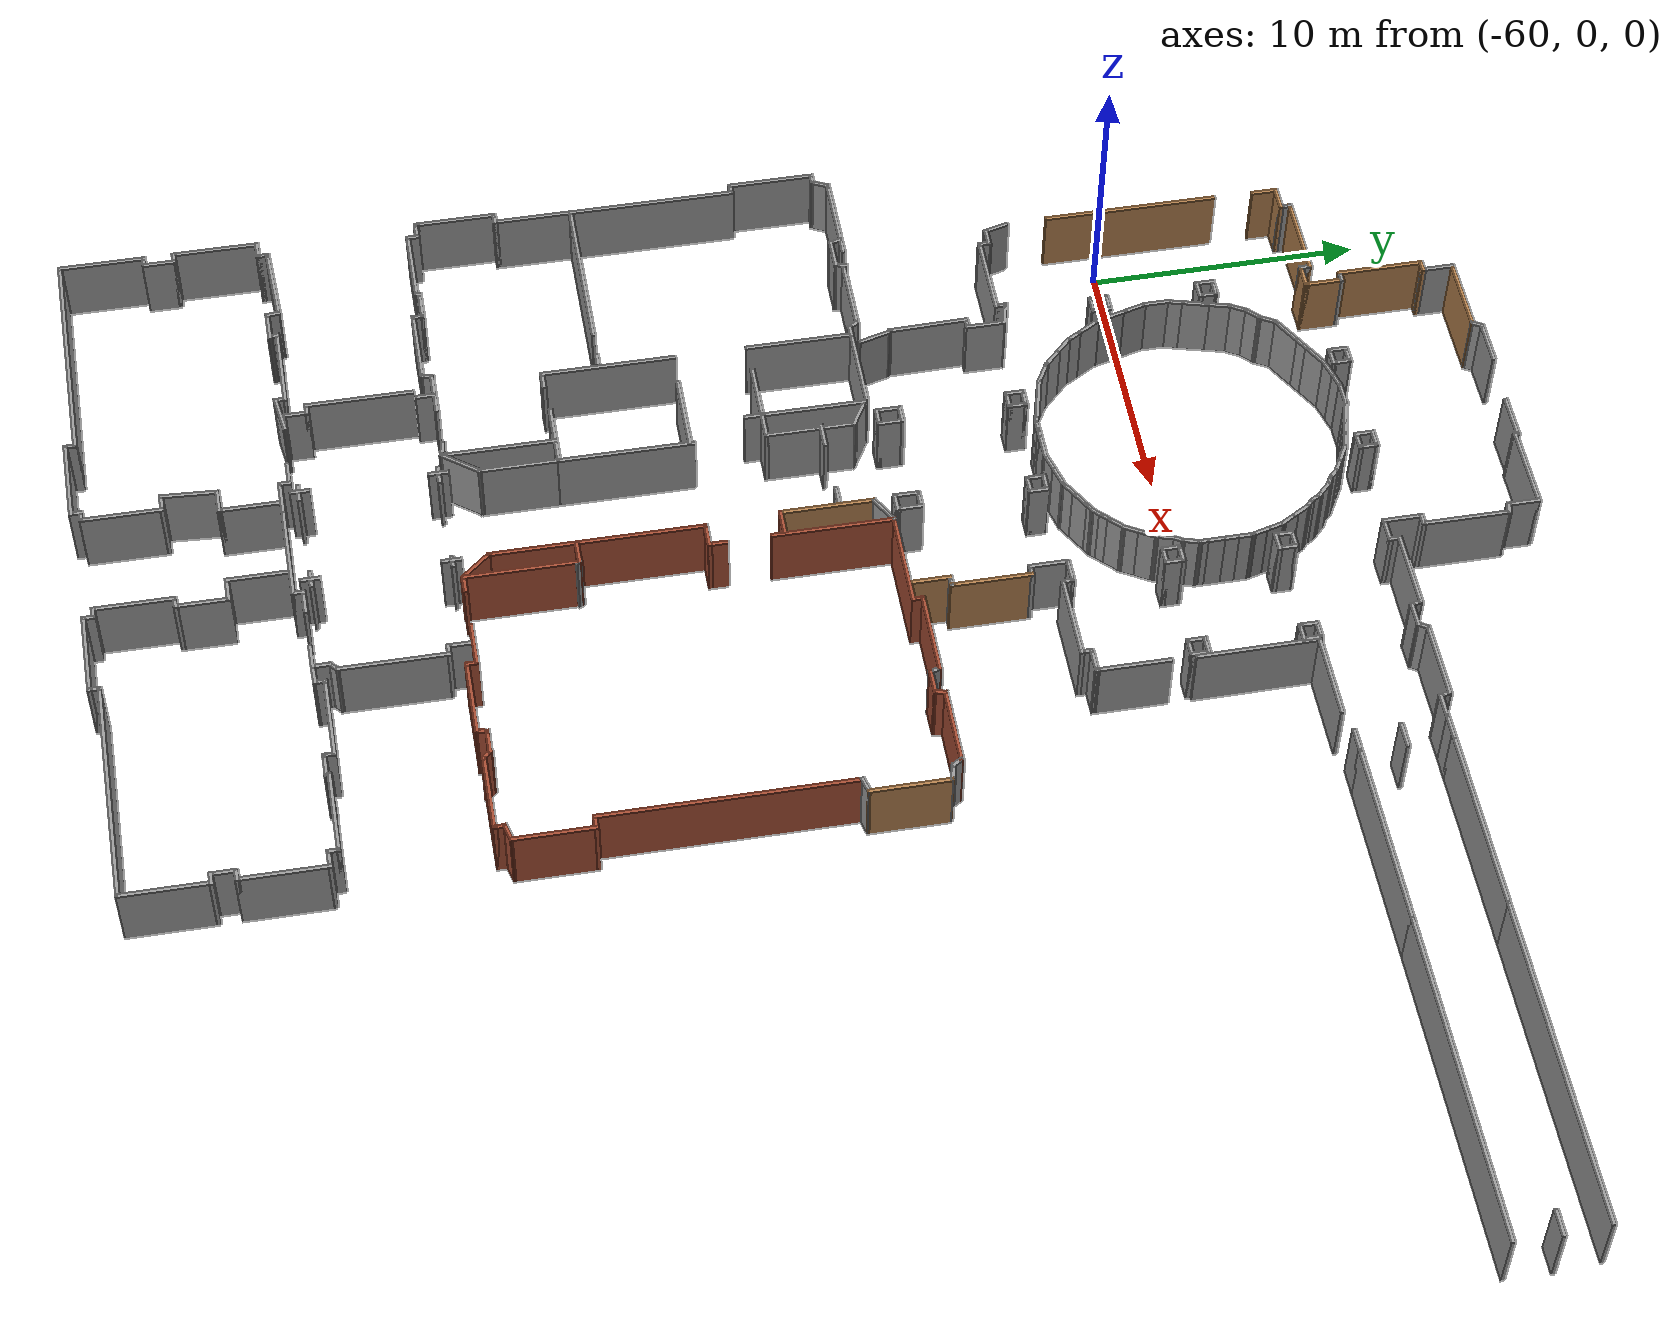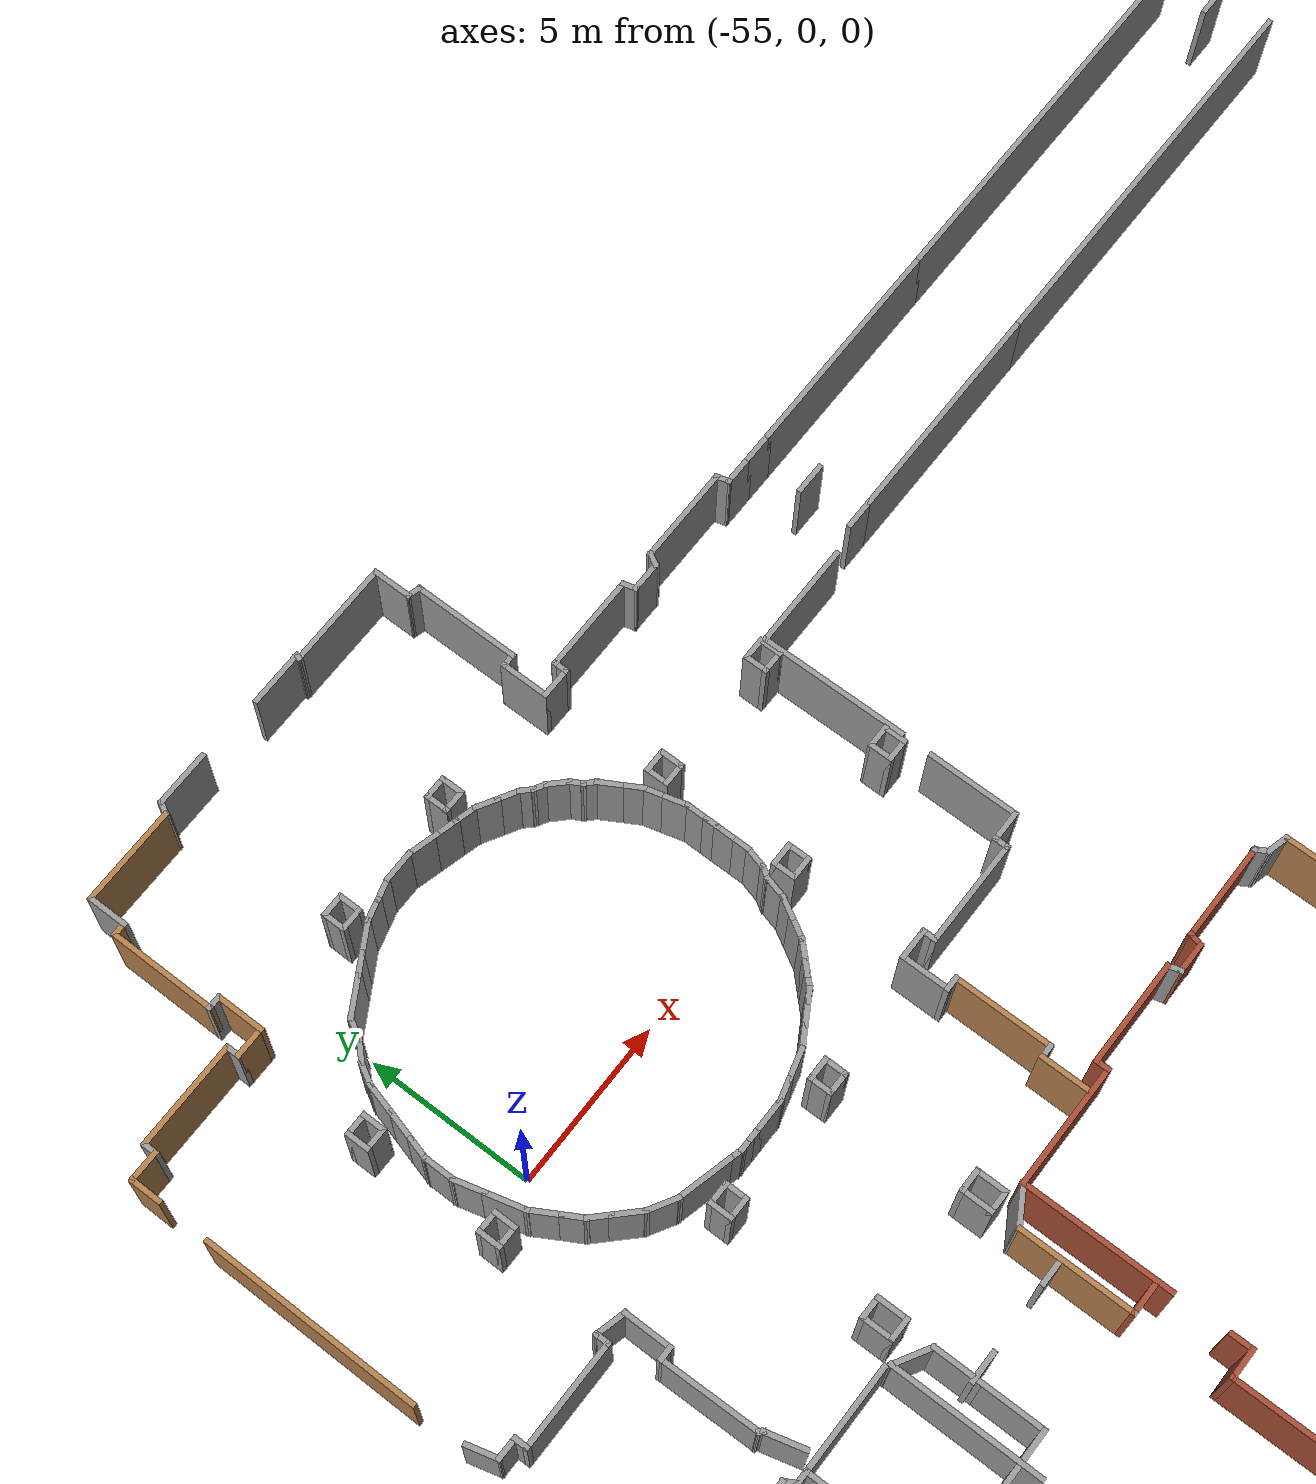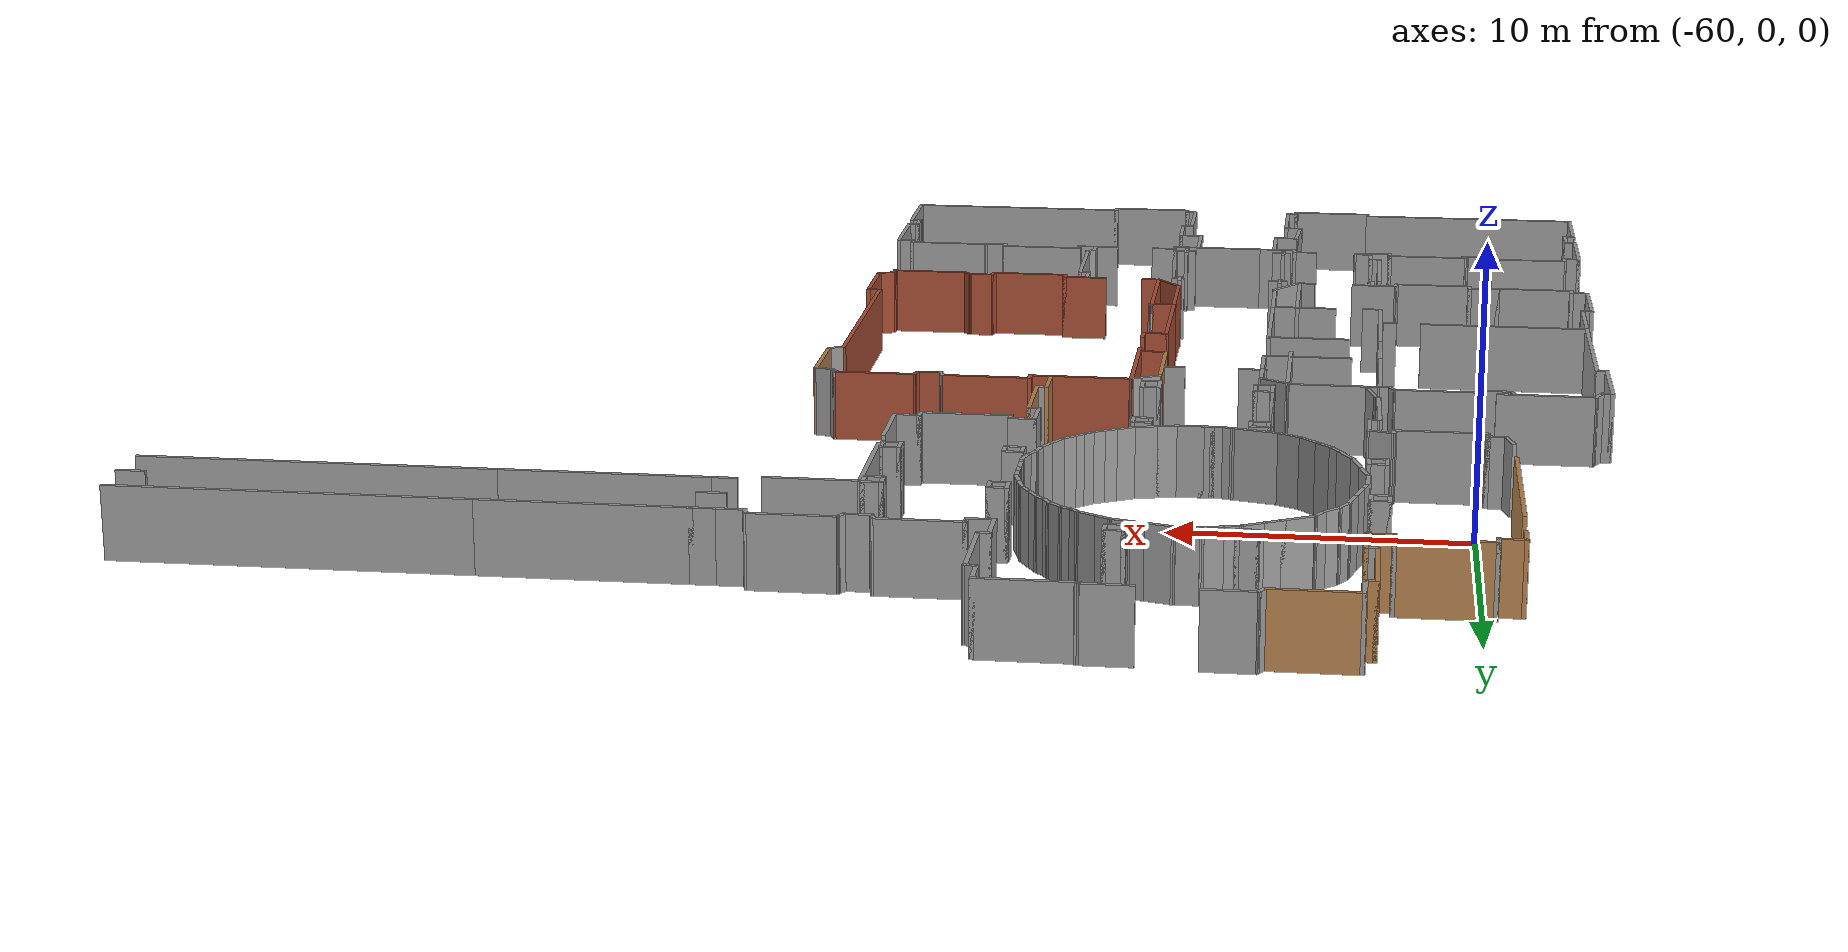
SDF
<?xml version='1.0'?>
<sdf version='1.7'>
  <model name='TD_1'>
    <pose>-32.4963 -12.7971 0 0 -0 0</pose>
    <link name='Wall_10'>
      <collision name='Wall_10_Collision'>
        <geometry>
          <box>
            <size>1 0.15 2.5</size>
          </box>
        </geometry>
        <pose>0 0 1.25 0 -0 0</pose>
      </collision>
      <visual name='Wall_10_Visual'>
        <pose>0 0 1.25 0 -0 0</pose>
        <geometry>
          <box>
            <size>1 0.15 2.5</size>
          </box>
        </geometry>
        <material>
          <script>
            <uri>file://media/materials/scripts/gazebo.material</uri>
            <name>Gazebo/Bricks</name>
          </script>
          <ambient>1 1 1 1</ambient>
        </material>
        <meta>
          <layer>0</layer>
        </meta>
      </visual>
      <pose>-8.41261 2.89283 0 0 -0 0</pose>
    </link>
    <link name='Wall_100'>
      <collision name='Wall_100_Collision'>
        <geometry>
          <box>
            <size>0.75 0.15 2.5</size>
          </box>
        </geometry>
        <pose>0 0 1.25 0 -0 0</pose>
      </collision>
      <visual name='Wall_100_Visual'>
        <pose>0 0 1.25 0 -0 0</pose>
        <geometry>
          <box>
            <size>0.75 0.15 2.5</size>
          </box>
        </geometry>
        <material>
          <script>
            <uri>file://media/materials/scripts/gazebo.material</uri>
            <name>Gazebo/Grey</name>
          </script>
          <ambient>1 1 1 1</ambient>
        </material>
        <meta>
          <layer>0</layer>
        </meta>
      </visual>
      <pose>-24.0693 -8.5054 0 0 -0 0</pose>
    </link>
    <link name='Wall_102'>
      <collision name='Wall_102_Collision'>
        <geometry>
          <box>
            <size>3 0.15 2.5</size>
          </box>
        </geometry>
        <pose>0 0 1.25 0 -0 0</pose>
      </collision>
      <visual name='Wall_102_Visual'>
        <pose>0 0 1.25 0 -0 0</pose>
        <geometry>
          <box>
            <size>3 0.15 2.5</size>
          </box>
        </geometry>
        <material>
          <script>
            <uri>file://media/materials/scripts/gazebo.material</uri>
            <name>Gazebo/Grey</name>
          </script>
          <ambient>1 1 1 1</ambient>
        </material>
        <meta>
          <layer>0</layer>
        </meta>
      </visual>
      <pose>-21.7443 -3.6954 0 0 -0 0</pose>
    </link>
    <link name='Wall_106'>
      <collision name='Wall_106_Collision'>
        <geometry>
          <box>
            <size>2.5 0.15 2.5</size>
          </box>
        </geometry>
        <pose>0 0 1.25 0 -0 0</pose>
      </collision>
      <visual name='Wall_106_Visual'>
        <pose>0 0 1.25 0 -0 0</pose>
        <geometry>
          <box>
            <size>2.5 0.15 2.5</size>
          </box>
        </geometry>
        <material>
          <script>
            <uri>file://media/materials/scripts/gazebo.material</uri>
            <name>Gazebo/Grey</name>
          </script>
          <ambient>1 1 1 1</ambient>
        </material>
        <meta>
          <layer>0</layer>
        </meta>
      </visual>
      <pose>-21.4301 -8.4346 0 0 -0 0</pose>
    </link>
    <link name='Wall_107'>
      <collision name='Wall_107_Collision'>
        <geometry>
          <box>
            <size>5 0.15 2.5</size>
          </box>
        </geometry>
        <pose>0 0 1.25 0 -0 0</pose>
      </collision>
      <visual name='Wall_107_Visual'>
        <pose>0 0 1.25 0 -0 0</pose>
        <geometry>
          <box>
            <size>5 0.15 2.5</size>
          </box>
        </geometry>
        <material>
          <script>
            <uri>file://media/materials/scripts/gazebo.material</uri>
            <name>Gazebo/Grey</name>
          </script>
          <ambient>1 1 1 1</ambient>
        </material>
        <meta>
          <layer>0</layer>
        </meta>
      </visual>
      <pose>-20.2551 -6.0096 0 0 -0 1.5708</pose>
    </link>
    <link name='Wall_109'>
      <collision name='Wall_109_Collision'>
        <geometry>
          <box>
            <size>3 0.15 2.5</size>
          </box>
        </geometry>
        <pose>0 0 1.25 0 -0 0</pose>
      </collision>
      <visual name='Wall_109_Visual'>
        <pose>0 0 1.25 0 -0 0</pose>
        <geometry>
          <box>
            <size>3 0.15 2.5</size>
          </box>
        </geometry>
        <material>
          <script>
            <uri>file://media/materials/scripts/gazebo.material</uri>
            <name>Gazebo/Grey</name>
          </script>
          <ambient>1 1 1 1</ambient>
        </material>
        <meta>
          <layer>0</layer>
        </meta>
      </visual>
      <pose>-32.0643 -7.82191 0 0 -0 -1.5708</pose>
    </link>
    <link name='Wall_11'>
      <collision name='Wall_11_Collision'>
        <geometry>
          <box>
            <size>0.5 0.15 2.5</size>
          </box>
        </geometry>
        <pose>0 0 1.25 0 -0 0</pose>
      </collision>
      <visual name='Wall_11_Visual'>
        <pose>0 0 1.25 0 -0 0</pose>
        <geometry>
          <box>
            <size>0.5 0.15 2.5</size>
          </box>
        </geometry>
        <material>
          <script>
            <uri>file://media/materials/scripts/gazebo.material</uri>
            <name>Gazebo/Bricks</name>
          </script>
          <ambient>1 1 1 1</ambient>
        </material>
        <meta>
          <layer>0</layer>
        </meta>
      </visual>
      <pose>-7.94231 3.06187 0 0 -0 1.309</pose>
    </link>
    <link name='Wall_110'>
      <collision name='Wall_110_Collision'>
        <geometry>
          <box>
            <size>0.5 0.15 2.5</size>
          </box>
        </geometry>
        <pose>0 0 1.25 0 -0 0</pose>
      </collision>
      <visual name='Wall_110_Visual'>
        <pose>0 0 1.25 0 -0 0</pose>
        <geometry>
          <box>
            <size>0.5 0.15 2.5</size>
          </box>
        </geometry>
        <material>
          <script>
            <uri>file://media/materials/scripts/gazebo.material</uri>
            <name>Gazebo/Grey</name>
          </script>
          <ambient>1 1 1 1</ambient>
        </material>
        <meta>
          <layer>0</layer>
        </meta>
      </visual>
      <pose>-32.2393 -9.24691 0 0 -0 3.14159</pose>
    </link>
    <link name='Wall_111'>
      <collision name='Wall_111_Collision'>
        <geometry>
          <box>
            <size>3 0.15 2.5</size>
          </box>
        </geometry>
        <pose>0 0 1.25 0 -0 0</pose>
      </collision>
      <visual name='Wall_111_Visual'>
        <pose>0 0 1.25 0 -0 0</pose>
        <geometry>
          <box>
            <size>3 0.15 2.5</size>
          </box>
        </geometry>
        <material>
          <script>
            <uri>file://media/materials/scripts/gazebo.material</uri>
            <name>Gazebo/Grey</name>
          </script>
          <ambient>1 1 1 1</ambient>
        </material>
        <meta>
          <layer>0</layer>
        </meta>
      </visual>
      <pose>-32.4143 -10.6719 0 0 -0 -1.5708</pose>
    </link>
    <link name='Wall_112'>
      <collision name='Wall_112_Collision'>
        <geometry>
          <box>
            <size>0.25 0.15 2.5</size>
          </box>
        </geometry>
        <pose>0 0 1.25 0 -0 0</pose>
      </collision>
      <visual name='Wall_112_Visual'>
        <pose>0 0 1.25 0 -0 0</pose>
        <geometry>
          <box>
            <size>0.25 0.15 2.5</size>
          </box>
        </geometry>
        <material>
          <script>
            <uri>file://media/materials/scripts/gazebo.material</uri>
            <name>Gazebo/Grey</name>
          </script>
          <ambient>1 1 1 1</ambient>
        </material>
        <meta>
          <layer>0</layer>
        </meta>
      </visual>
      <pose>-32.4143 -12.1469 0 0 -0 -1.5708</pose>
    </link>
    <link name='Wall_113'>
      <collision name='Wall_113_Collision'>
        <geometry>
          <box>
            <size>0.75 0.15 2.5</size>
          </box>
        </geometry>
        <pose>0 0 1.25 0 -0 0</pose>
      </collision>
      <visual name='Wall_113_Visual'>
        <pose>0 0 1.25 0 -0 0</pose>
        <geometry>
          <box>
            <size>0.75 0.15 2.5</size>
          </box>
        </geometry>
        <material>
          <script>
            <uri>file://media/materials/scripts/gazebo.material</uri>
            <name>Gazebo/Grey</name>
          </script>
          <ambient>1 1 1 1</ambient>
        </material>
        <meta>
          <layer>0</layer>
        </meta>
      </visual>
      <pose>-32.1143 -12.1969 0 0 -0 0</pose>
    </link>
    <link name='Wall_114'>
      <collision name='Wall_114_Collision'>
        <geometry>
          <box>
            <size>0.5 0.15 2.5</size>
          </box>
        </geometry>
        <pose>0 0 1.25 0 -0 0</pose>
      </collision>
      <visual name='Wall_114_Visual'>
        <pose>0 0 1.25 0 -0 0</pose>
        <geometry>
          <box>
            <size>0.5 0.15 2.5</size>
          </box>
        </geometry>
        <material>
          <script>
            <uri>file://media/materials/scripts/gazebo.material</uri>
            <name>Gazebo/Grey</name>
          </script>
          <ambient>1 1 1 1</ambient>
        </material>
        <meta>
          <layer>0</layer>
        </meta>
      </visual>
      <pose>-31.8143 -12.3719 0 0 -0 -1.5708</pose>
    </link>
    <link name='Wall_118'>
      <collision name='Wall_118_Collision'>
        <geometry>
          <box>
            <size>3 0.15 2.5</size>
          </box>
        </geometry>
        <pose>0 0 1.25 0 -0 0</pose>
      </collision>
      <visual name='Wall_118_Visual'>
        <pose>0 0 1.25 0 -0 0</pose>
        <geometry>
          <box>
            <size>3 0.15 2.5</size>
          </box>
        </geometry>
        <material>
          <script>
            <uri>file://media/materials/scripts/gazebo.material</uri>
            <name>Gazebo/Grey</name>
          </script>
          <ambient>1 1 1 1</ambient>
        </material>
        <meta>
          <layer>0</layer>
        </meta>
      </visual>
      <pose>-30.3893 -12.5469 0 0 -0 0</pose>
    </link>
    <link name='Wall_119'>
      <collision name='Wall_119_Collision'>
        <geometry>
          <box>
            <size>0.25 0.15 2.5</size>
          </box>
        </geometry>
        <pose>0 0 1.25 0 -0 0</pose>
      </collision>
      <visual name='Wall_119_Visual'>
        <pose>0 0 1.25 0 -0 0</pose>
        <geometry>
          <box>
            <size>0.25 0.15 2.5</size>
          </box>
        </geometry>
        <material>
          <script>
            <uri>file://media/materials/scripts/gazebo.material</uri>
            <name>Gazebo/Grey</name>
          </script>
          <ambient>1 1 1 1</ambient>
        </material>
        <meta>
          <layer>0</layer>
        </meta>
      </visual>
      <pose>-28.9643 -12.4969 0 0 -0 1.5708</pose>
    </link>
    <link name='Wall_12'>
      <collision name='Wall_12_Collision'>
        <geometry>
          <box>
            <size>3 0.15 2.5</size>
          </box>
        </geometry>
        <pose>0 0 1.25 0 -0 0</pose>
      </collision>
      <visual name='Wall_12_Visual'>
        <pose>0 0 1.25 0 -0 0</pose>
        <geometry>
          <box>
            <size>3 0.15 2.5</size>
          </box>
        </geometry>
        <material>
          <script>
            <uri>file://media/materials/scripts/gazebo.material</uri>
            <name>Gazebo/Bricks</name>
          </script>
          <ambient>1 1 1 1</ambient>
        </material>
        <meta>
          <layer>0</layer>
        </meta>
      </visual>
      <pose>-6.47202 3.2309 0 0 -0 0</pose>
    </link>
    <link name='Wall_120'>
      <collision name='Wall_120_Collision'>
        <geometry>
          <box>
            <size>1.25 0.15 2.5</size>
          </box>
        </geometry>
        <pose>0 0 1.25 0 -0 0</pose>
      </collision>
      <visual name='Wall_120_Visual'>
        <pose>0 0 1.25 0 -0 0</pose>
        <geometry>
          <box>
            <size>1.25 0.15 2.5</size>
          </box>
        </geometry>
        <material>
          <script>
            <uri>file://media/materials/scripts/gazebo.material</uri>
            <name>Gazebo/Grey</name>
          </script>
          <ambient>1 1 1 1</ambient>
        </material>
        <meta>
          <layer>0</layer>
        </meta>
      </visual>
      <pose>-28.4143 -12.4469 0 0 -0 0</pose>
    </link>
    <link name='Wall_121'>
      <collision name='Wall_121_Collision'>
        <geometry>
          <box>
            <size>0.5 0.15 2.5</size>
          </box>
        </geometry>
        <pose>0 0 1.25 0 -0 0</pose>
      </collision>
      <visual name='Wall_121_Visual'>
        <pose>0 0 1.25 0 -0 0</pose>
        <geometry>
          <box>
            <size>0.5 0.15 2.5</size>
          </box>
        </geometry>
        <material>
          <script>
            <uri>file://media/materials/scripts/gazebo.material</uri>
            <name>Gazebo/Grey</name>
          </script>
          <ambient>1 1 1 1</ambient>
        </material>
        <meta>
          <layer>0</layer>
        </meta>
      </visual>
      <pose>-27.8643 -12.6219 0 0 -0 -1.5708</pose>
    </link>
    <link name='Wall_122'>
      <collision name='Wall_122_Collision'>
        <geometry>
          <box>
            <size>3 0.15 2.5</size>
          </box>
        </geometry>
        <pose>0 0 1.25 0 -0 0</pose>
      </collision>
      <visual name='Wall_122_Visual'>
        <pose>0 0 1.25 0 -0 0</pose>
        <geometry>
          <box>
            <size>3 0.15 2.5</size>
          </box>
        </geometry>
        <material>
          <script>
            <uri>file://media/materials/scripts/gazebo.material</uri>
            <name>Gazebo/Grey</name>
          </script>
          <ambient>1 1 1 1</ambient>
        </material>
        <meta>
          <layer>0</layer>
        </meta>
      </visual>
      <pose>-26.4393 -12.7969 0 0 -0 0</pose>
    </link>
    <link name='Wall_123'>
      <collision name='Wall_123_Collision'>
        <geometry>
          <box>
            <size>0.5 0.15 2.5</size>
          </box>
        </geometry>
        <pose>0 0 1.25 0 -0 0</pose>
      </collision>
      <visual name='Wall_123_Visual'>
        <pose>0 0 1.25 0 -0 0</pose>
        <geometry>
          <box>
            <size>0.5 0.15 2.5</size>
          </box>
        </geometry>
        <material>
          <script>
            <uri>file://media/materials/scripts/gazebo.material</uri>
            <name>Gazebo/Grey</name>
          </script>
          <ambient>1 1 1 1</ambient>
        </material>
        <meta>
          <layer>0</layer>
        </meta>
      </visual>
      <pose>-24.969 -12.6279 0 0 -0 1.309</pose>
    </link>
    <link name='Wall_124'>
      <collision name='Wall_124_Collision'>
        <geometry>
          <box>
            <size>1.75 0.15 2.5</size>
          </box>
        </geometry>
        <pose>0 0 1.25 0 -0 0</pose>
      </collision>
      <visual name='Wall_124_Visual'>
        <pose>0 0 1.25 0 -0 0</pose>
        <geometry>
          <box>
            <size>1.75 0.15 2.5</size>
          </box>
        </geometry>
        <material>
          <script>
            <uri>file://media/materials/scripts/gazebo.material</uri>
            <name>Gazebo/Grey</name>
          </script>
          <ambient>1 1 1 1</ambient>
        </material>
        <meta>
          <layer>0</layer>
        </meta>
      </visual>
      <pose>-24.1237 -12.4588 0 0 -0 0</pose>
    </link>
    <link name='Wall_126'>
      <collision name='Wall_126_Collision'>
        <geometry>
          <box>
            <size>4.25 0.15 2.5</size>
          </box>
        </geometry>
        <pose>0 0 1.25 0 -0 0</pose>
      </collision>
      <visual name='Wall_126_Visual'>
        <pose>0 0 1.25 0 -0 0</pose>
        <geometry>
          <box>
            <size>4.25 0.15 2.5</size>
          </box>
        </geometry>
        <material>
          <script>
            <uri>file://media/materials/scripts/gazebo.material</uri>
            <name>Gazebo/Grey</name>
          </script>
          <ambient>1 1 1 1</ambient>
        </material>
        <meta>
          <layer>0</layer>
        </meta>
      </visual>
      <pose>-21.1888 -10.4845 0 0 -0 -1.5708</pose>
    </link>
    <link name='Wall_129'>
      <collision name='Wall_129_Collision'>
        <geometry>
          <box>
            <size>0.699097 0.15 2.5</size>
          </box>
        </geometry>
        <pose>0 0 1.25 0 -0 0</pose>
      </collision>
      <visual name='Wall_129_Visual'>
        <pose>0 0 1.25 0 -0 0</pose>
        <geometry>
          <box>
            <size>0.699097 0.15 2.5</size>
          </box>
        </geometry>
        <material>
          <script>
            <uri>file://media/materials/scripts/gazebo.material</uri>
            <name>Gazebo/Grey</name>
          </script>
          <ambient>1 1 1 1</ambient>
        </material>
        <meta>
          <layer>0</layer>
        </meta>
      </visual>
      <pose>-21.4584 -12.4828 0 0 -0 -0.189446</pose>
    </link>
    <link name='Wall_13'>
      <collision name='Wall_13_Collision'>
        <geometry>
          <box>
            <size>0.15 0.15 2.5</size>
          </box>
        </geometry>
        <pose>0 0 1.25 0 -0 0</pose>
      </collision>
      <visual name='Wall_13_Visual'>
        <pose>0 0 1.25 0 -0 0</pose>
        <geometry>
          <box>
            <size>0.15 0.15 2.5</size>
          </box>
        </geometry>
        <material>
          <script>
            <uri>file://media/materials/scripts/gazebo.material</uri>
            <name>Gazebo/Grey</name>
          </script>
          <ambient>1 1 1 1</ambient>
        </material>
        <meta>
          <layer>0</layer>
        </meta>
      </visual>
      <pose>-5.04702 3.2309 0 0 -0 0</pose>
    </link>
    <link name='Wall_133'>
      <collision name='Wall_133_Collision'>
        <geometry>
          <box>
            <size>3 0.15 2.5</size>
          </box>
        </geometry>
        <pose>0 0 1.25 0 -0 0</pose>
      </collision>
      <visual name='Wall_133_Visual'>
        <pose>0 0 1.25 0 -0 0</pose>
        <geometry>
          <box>
            <size>3 0.15 2.5</size>
          </box>
        </geometry>
        <material>
          <script>
            <uri>file://media/materials/scripts/gazebo.material</uri>
            <name>Gazebo/Grey</name>
          </script>
          <ambient>1 1 1 1</ambient>
        </material>
        <meta>
          <layer>0</layer>
        </meta>
      </visual>
      <pose>-20.2551 -9.8596 0 0 -0 -1.5708</pose>
    </link>
    <link name='Wall_134'>
      <collision name='Wall_134_Collision'>
        <geometry>
          <box>
            <size>1.71016 0.15 2.5</size>
          </box>
        </geometry>
        <pose>0 0 1.25 0 -0 0</pose>
      </collision>
      <visual name='Wall_134_Visual'>
        <pose>0 0 1.25 0 -0 0</pose>
        <geometry>
          <box>
            <size>1.71016 0.15 2.5</size>
          </box>
        </geometry>
        <material>
          <script>
            <uri>file://media/materials/scripts/gazebo.material</uri>
            <name>Gazebo/Grey</name>
          </script>
          <ambient>1 1 1 1</ambient>
        </material>
        <meta>
          <layer>0</layer>
        </meta>
      </visual>
      <pose>-20.7219 -11.9096 0 0 -0 -2.2124</pose>
    </link>
    <link name='Wall_138'>
      <collision name='Wall_138_Collision'>
        <geometry>
          <box>
            <size>0.75 0.15 2.5</size>
          </box>
        </geometry>
        <pose>0 0 1.25 0 -0 0</pose>
      </collision>
      <visual name='Wall_138_Visual'>
        <pose>0 0 1.25 0 -0 0</pose>
        <geometry>
          <box>
            <size>0.75 0.15 2.5</size>
          </box>
        </geometry>
        <material>
          <script>
            <uri>file://media/materials/scripts/gazebo.material</uri>
            <name>Gazebo/Grey</name>
          </script>
          <ambient>1 1 1 1</ambient>
        </material>
        <meta>
          <layer>0</layer>
        </meta>
      </visual>
      <pose>-24.0418 -12.7893 0 0 -0 -1.5708</pose>
    </link>
    <link name='Wall_14'>
      <collision name='Wall_14_Collision'>
        <geometry>
          <box>
            <size>0.15 0.15 2.5</size>
          </box>
        </geometry>
        <pose>0 0 1.25 0 -0 0</pose>
      </collision>
      <visual name='Wall_14_Visual'>
        <pose>0 0 1.25 0 -0 0</pose>
        <geometry>
          <box>
            <size>0.15 0.15 2.5</size>
          </box>
        </geometry>
        <material>
          <script>
            <uri>file://media/materials/scripts/gazebo.material</uri>
            <name>Gazebo/Grey</name>
          </script>
          <ambient>1 1 1 1</ambient>
        </material>
        <meta>
          <layer>0</layer>
        </meta>
      </visual>
      <pose>-5.04702 3.2309 0 0 -0 0</pose>
    </link>
    <link name='Wall_143'>
      <collision name='Wall_143_Collision'>
        <geometry>
          <box>
            <size>4 0.15 2.5</size>
          </box>
        </geometry>
        <pose>0 0 1.25 0 -0 0</pose>
      </collision>
      <visual name='Wall_143_Visual'>
        <pose>0 0 1.25 0 -0 0</pose>
        <geometry>
          <box>
            <size>4 0.15 2.5</size>
          </box>
        </geometry>
        <material>
          <script>
            <uri>file://media/materials/scripts/gazebo.material</uri>
            <name>Gazebo/Grey</name>
          </script>
          <ambient>1 1 1 1</ambient>
        </material>
        <meta>
          <layer>0</layer>
        </meta>
      </visual>
      <pose>-24.3141 -15.1704 0 0 -0 -1.5708</pose>
    </link>
    <link name='Wall_144'>
      <collision name='Wall_144_Collision'>
        <geometry>
          <box>
            <size>0.5 0.15 2.5</size>
          </box>
        </geometry>
        <pose>0 0 1.25 0 -0 0</pose>
      </collision>
      <visual name='Wall_144_Visual'>
        <pose>0 0 1.25 0 -0 0</pose>
        <geometry>
          <box>
            <size>0.5 0.15 2.5</size>
          </box>
        </geometry>
        <material>
          <script>
            <uri>file://media/materials/scripts/gazebo.material</uri>
            <name>Gazebo/Grey</name>
          </script>
          <ambient>1 1 1 1</ambient>
        </material>
        <meta>
          <layer>0</layer>
        </meta>
      </visual>
      <pose>-24.1391 -17.0954 0 0 -0 0</pose>
    </link>
    <link name='Wall_145'>
      <collision name='Wall_145_Collision'>
        <geometry>
          <box>
            <size>1 0.15 2.5</size>
          </box>
        </geometry>
        <pose>0 0 1.25 0 -0 0</pose>
      </collision>
      <visual name='Wall_145_Visual'>
        <pose>0 0 1.25 0 -0 0</pose>
        <geometry>
          <box>
            <size>1 0.15 2.5</size>
          </box>
        </geometry>
        <material>
          <script>
            <uri>file://media/materials/scripts/gazebo.material</uri>
            <name>Gazebo/Grey</name>
          </script>
          <ambient>1 1 1 1</ambient>
        </material>
        <meta>
          <layer>0</layer>
        </meta>
      </visual>
      <pose>-23.9641 -17.5204 0 0 -0 -1.5708</pose>
    </link>
    <link name='Wall_146'>
      <collision name='Wall_146_Collision'>
        <geometry>
          <box>
            <size>0.75 0.15 2.5</size>
          </box>
        </geometry>
        <pose>0 0 1.25 0 -0 0</pose>
      </collision>
      <visual name='Wall_146_Visual'>
        <pose>0 0 1.25 0 -0 0</pose>
        <geometry>
          <box>
            <size>0.75 0.15 2.5</size>
          </box>
        </geometry>
        <material>
          <script>
            <uri>file://media/materials/scripts/gazebo.material</uri>
            <name>Gazebo/Grey</name>
          </script>
          <ambient>1 1 1 1</ambient>
        </material>
        <meta>
          <layer>0</layer>
        </meta>
      </visual>
      <pose>-23.6641 -17.9454 0 0 -0 0</pose>
    </link>
    <link name='Wall_148'>
      <collision name='Wall_148_Collision'>
        <geometry>
          <box>
            <size>1 0.15 2.5</size>
          </box>
        </geometry>
        <pose>0 0 1.25 0 -0 0</pose>
      </collision>
      <visual name='Wall_148_Visual'>
        <pose>0 0 1.25 0 -0 0</pose>
        <geometry>
          <box>
            <size>1 0.15 2.5</size>
          </box>
        </geometry>
        <material>
          <script>
            <uri>file://media/materials/scripts/gazebo.material</uri>
            <name>Gazebo/Grey</name>
          </script>
          <ambient>1 1 1 1</ambient>
        </material>
        <meta>
          <layer>0</layer>
        </meta>
      </visual>
      <pose>-21.2577 -18.0243 0 0 -0 0</pose>
    </link>
    <link name='Wall_149'>
      <collision name='Wall_149_Collision'>
        <geometry>
          <box>
            <size>0.5 0.15 2.5</size>
          </box>
        </geometry>
        <pose>0 0 1.25 0 -0 0</pose>
      </collision>
      <visual name='Wall_149_Visual'>
        <pose>0 0 1.25 0 -0 0</pose>
        <geometry>
          <box>
            <size>0.5 0.15 2.5</size>
          </box>
        </geometry>
        <material>
          <script>
            <uri>file://media/materials/scripts/gazebo.material</uri>
            <name>Gazebo/Grey</name>
          </script>
          <ambient>1 1 1 1</ambient>
        </material>
        <meta>
          <layer>0</layer>
        </meta>
      </visual>
      <pose>-20.8327 -18.1993 0 0 -0 -1.5708</pose>
    </link>
    <link name='Wall_150'>
      <collision name='Wall_150_Collision'>
        <geometry>
          <box>
            <size>1.5 0.15 2.5</size>
          </box>
        </geometry>
        <pose>0 0 1.25 0 -0 0</pose>
      </collision>
      <visual name='Wall_150_Visual'>
        <pose>0 0 1.25 0 -0 0</pose>
        <geometry>
          <box>
            <size>1.5 0.15 2.5</size>
          </box>
        </geometry>
        <material>
          <script>
            <uri>file://media/materials/scripts/gazebo.material</uri>
            <name>Gazebo/Grey</name>
          </script>
          <ambient>1 1 1 1</ambient>
        </material>
        <meta>
          <layer>0</layer>
        </meta>
      </visual>
      <pose>-20.1577 -18.3743 0 0 -0 0</pose>
    </link>
    <link name='Wall_151'>
      <collision name='Wall_151_Collision'>
        <geometry>
          <box>
            <size>3.75 0.15 2.5</size>
          </box>
        </geometry>
        <pose>0 0 1.25 0 -0 0</pose>
      </collision>
      <visual name='Wall_151_Visual'>
        <pose>0 0 1.25 0 -0 0</pose>
        <geometry>
          <box>
            <size>3.75 0.15 2.5</size>
          </box>
        </geometry>
        <material>
          <script>
            <uri>file://media/materials/scripts/gazebo.material</uri>
            <name>Gazebo/Grey</name>
          </script>
          <ambient>1 1 1 1</ambient>
        </material>
        <meta>
          <layer>0</layer>
        </meta>
      </visual>
      <pose>-17.6827 -18.3743 0 0 -0 0</pose>
    </link>
    <link name='Wall_152'>
      <collision name='Wall_152_Collision'>
        <geometry>
          <box>
            <size>0.5 0.15 2.5</size>
          </box>
        </geometry>
        <pose>0 0 1.25 0 -0 0</pose>
      </collision>
      <visual name='Wall_152_Visual'>
        <pose>0 0 1.25 0 -0 0</pose>
        <geometry>
          <box>
            <size>0.5 0.15 2.5</size>
          </box>
        </geometry>
        <material>
          <script>
            <uri>file://media/materials/scripts/gazebo.material</uri>
            <name>Gazebo/Grey</name>
          </script>
          <ambient>1 1 1 1</ambient>
        </material>
        <meta>
          <layer>0</layer>
        </meta>
      </visual>
      <pose>-15.8827 -18.1993 0 0 -0 1.5708</pose>
    </link>
    <link name='Wall_153'>
      <collision name='Wall_153_Collision'>
        <geometry>
          <box>
            <size>1 0.15 2.5</size>
          </box>
        </geometry>
        <pose>0 0 1.25 0 -0 0</pose>
      </collision>
      <visual name='Wall_153_Visual'>
        <pose>0 0 1.25 0 -0 0</pose>
        <geometry>
          <box>
            <size>1 0.15 2.5</size>
          </box>
        </geometry>
        <material>
          <script>
            <uri>file://media/materials/scripts/gazebo.material</uri>
            <name>Gazebo/Grey</name>
          </script>
          <ambient>1 1 1 1</ambient>
        </material>
        <meta>
          <layer>0</layer>
        </meta>
      </visual>
      <pose>-15.4577 -18.0243 0 0 -0 0</pose>
    </link>
    <link name='Wall_155'>
      <collision name='Wall_155_Collision'>
        <geometry>
          <box>
            <size>1 0.15 2.5</size>
          </box>
        </geometry>
        <pose>0 0 1.25 0 -0 0</pose>
      </collision>
      <visual name='Wall_155_Visual'>
        <pose>0 0 1.25 0 -0 0</pose>
        <geometry>
          <box>
            <size>1 0.15 2.5</size>
          </box>
        </geometry>
        <material>
          <script>
            <uri>file://media/materials/scripts/gazebo.material</uri>
            <name>Gazebo/Grey</name>
          </script>
          <ambient>1 1 1 1</ambient>
        </material>
        <meta>
          <layer>0</layer>
        </meta>
      </visual>
      <pose>-13.0308 -18.0243 0 0 -0 0</pose>
    </link>
    <link name='Wall_156'>
      <collision name='Wall_156_Collision'>
        <geometry>
          <box>
            <size>0.75 0.15 2.5</size>
          </box>
        </geometry>
        <pose>0 0 1.25 0 -0 0</pose>
      </collision>
      <visual name='Wall_156_Visual'>
        <pose>0 0 1.25 0 -0 0</pose>
        <geometry>
          <box>
            <size>0.75 0.15 2.5</size>
          </box>
        </geometry>
        <material>
          <script>
            <uri>file://media/materials/scripts/gazebo.material</uri>
            <name>Gazebo/Grey</name>
          </script>
          <ambient>1 1 1 1</ambient>
        </material>
        <meta>
          <layer>0</layer>
        </meta>
      </visual>
      <pose>-12.6058 -17.7243 0 0 -0 1.5708</pose>
    </link>
    <link name='Wall_157'>
      <collision name='Wall_157_Collision'>
        <geometry>
          <box>
            <size>0.5 0.15 2.5</size>
          </box>
        </geometry>
        <pose>0 0 1.25 0 -0 0</pose>
      </collision>
      <visual name='Wall_157_Visual'>
        <pose>0 0 1.25 0 -0 0</pose>
        <geometry>
          <box>
            <size>0.5 0.15 2.5</size>
          </box>
        </geometry>
        <material>
          <script>
            <uri>file://media/materials/scripts/gazebo.material</uri>
            <name>Gazebo/Grey</name>
          </script>
          <ambient>1 1 1 1</ambient>
        </material>
        <meta>
          <layer>0</layer>
        </meta>
      </visual>
      <pose>-12.4821 -17.3005 0 0 -0 0.785398</pose>
    </link>
    <link name='Wall_158'>
      <collision name='Wall_158_Collision'>
        <geometry>
          <box>
            <size>4 0.15 2.5</size>
          </box>
        </geometry>
        <pose>0 0 1.25 0 -0 0</pose>
      </collision>
      <visual name='Wall_158_Visual'>
        <pose>0 0 1.25 0 -0 0</pose>
        <geometry>
          <box>
            <size>4 0.15 2.5</size>
          </box>
        </geometry>
        <material>
          <script>
            <uri>file://media/materials/scripts/gazebo.material</uri>
            <name>Gazebo/Grey</name>
          </script>
          <ambient>1 1 1 1</ambient>
        </material>
        <meta>
          <layer>0</layer>
        </meta>
      </visual>
      <pose>-12.3583 -15.2518 0 0 -0 1.5708</pose>
    </link>
    <link name='Wall_159'>
      <collision name='Wall_159_Collision'>
        <geometry>
          <box>
            <size>0.5 0.15 2.5</size>
          </box>
        </geometry>
        <pose>0 0 1.25 0 -0 0</pose>
      </collision>
      <visual name='Wall_159_Visual'>
        <pose>0 0 1.25 0 -0 0</pose>
        <geometry>
          <box>
            <size>0.5 0.15 2.5</size>
          </box>
        </geometry>
        <material>
          <script>
            <uri>file://media/materials/scripts/gazebo.material</uri>
            <name>Gazebo/Grey</name>
          </script>
          <ambient>1 1 1 1</ambient>
        </material>
        <meta>
          <layer>0</layer>
        </meta>
      </visual>
      <pose>-12.5333 -13.3268 0 0 -0 3.14159</pose>
    </link>
    <link name='Wall_16'>
      <collision name='Wall_16_Collision'>
        <geometry>
          <box>
            <size>0.5 0.15 2.5</size>
          </box>
        </geometry>
        <pose>0 0 1.25 0 -0 0</pose>
      </collision>
      <visual name='Wall_16_Visual'>
        <pose>0 0 1.25 0 -0 0</pose>
        <geometry>
          <box>
            <size>0.5 0.15 2.5</size>
          </box>
        </geometry>
        <material>
          <script>
            <uri>file://media/materials/scripts/gazebo.material</uri>
            <name>Gazebo/Grey</name>
          </script>
          <ambient>1 1 1 1</ambient>
        </material>
        <meta>
          <layer>0</layer>
        </meta>
      </visual>
      <pose>-4.95952 3.07935 0 0 -0 -1.0472</pose>
    </link>
    <link name='Wall_160'>
      <collision name='Wall_160_Collision'>
        <geometry>
          <box>
            <size>1 0.15 2.5</size>
          </box>
        </geometry>
        <pose>0 0 1.25 0 -0 0</pose>
      </collision>
      <visual name='Wall_160_Visual'>
        <pose>0 0 1.25 0 -0 0</pose>
        <geometry>
          <box>
            <size>1 0.15 2.5</size>
          </box>
        </geometry>
        <material>
          <script>
            <uri>file://media/materials/scripts/gazebo.material</uri>
            <name>Gazebo/Grey</name>
          </script>
          <ambient>1 1 1 1</ambient>
        </material>
        <meta>
          <layer>0</layer>
        </meta>
      </visual>
      <pose>-12.7083 -12.9018 0 0 -0 1.5708</pose>
    </link>
    <link name='Wall_162'>
      <collision name='Wall_162_Collision'>
        <geometry>
          <box>
            <size>3.25 0.15 2.5</size>
          </box>
        </geometry>
        <pose>0 0 1.25 0 -0 0</pose>
      </collision>
      <visual name='Wall_162_Visual'>
        <pose>0 0 1.25 0 -0 0</pose>
        <geometry>
          <box>
            <size>3.25 0.15 2.5</size>
          </box>
        </geometry>
        <material>
          <script>
            <uri>file://media/materials/scripts/gazebo.material</uri>
            <name>Gazebo/Grey</name>
          </script>
          <ambient>1 1 1 1</ambient>
        </material>
        <meta>
          <layer>0</layer>
        </meta>
      </visual>
      <pose>-26.2939 -17.8048 0 0 -0 0</pose>
    </link>
    <link name='Wall_163'>
      <collision name='Wall_163_Collision'>
        <geometry>
          <box>
            <size>0.5 0.15 2.5</size>
          </box>
        </geometry>
        <pose>0 0 1.25 0 -0 0</pose>
      </collision>
      <visual name='Wall_163_Visual'>
        <pose>0 0 1.25 0 -0 0</pose>
        <geometry>
          <box>
            <size>0.5 0.15 2.5</size>
          </box>
        </geometry>
        <material>
          <script>
            <uri>file://media/materials/scripts/gazebo.material</uri>
            <name>Gazebo/Grey</name>
          </script>
          <ambient>1 1 1 1</ambient>
        </material>
        <meta>
          <layer>0</layer>
        </meta>
      </visual>
      <pose>-24.7439 -17.9798 0 0 -0 -1.5708</pose>
    </link>
    <link name='Wall_164'>
      <collision name='Wall_164_Collision'>
        <geometry>
          <box>
            <size>1.5456 0.15 2.5</size>
          </box>
        </geometry>
        <pose>0 0 1.25 0 -0 0</pose>
      </collision>
      <visual name='Wall_164_Visual'>
        <pose>0 0 1.25 0 -0 0</pose>
        <geometry>
          <box>
            <size>1.5456 0.15 2.5</size>
          </box>
        </geometry>
        <material>
          <script>
            <uri>file://media/materials/scripts/gazebo.material</uri>
            <name>Gazebo/Grey</name>
          </script>
          <ambient>1 1 1 1</ambient>
        </material>
        <meta>
          <layer>0</layer>
        </meta>
      </visual>
      <pose>-24.054 -18.0501 0 0 -0 0.150582</pose>
    </link>
    <link name='Wall_166'>
      <collision name='Wall_166_Collision'>
        <geometry>
          <box>
            <size>1.25 0.15 2.5</size>
          </box>
        </geometry>
        <pose>0 0 1.25 0 -0 0</pose>
      </collision>
      <visual name='Wall_166_Visual'>
        <pose>0 0 1.25 0 -0 0</pose>
        <geometry>
          <box>
            <size>1.25 0.15 2.5</size>
          </box>
        </geometry>
        <material>
          <script>
            <uri>file://media/materials/scripts/gazebo.material</uri>
            <name>Gazebo/Grey</name>
          </script>
          <ambient>1 1 1 1</ambient>
        </material>
        <meta>
          <layer>0</layer>
        </meta>
      </visual>
      <pose>-28.3142 -18.0728 0 0 -0 0</pose>
    </link>
    <link name='Wall_167'>
      <collision name='Wall_167_Collision'>
        <geometry>
          <box>
            <size>0.429643 0.15 2.5</size>
          </box>
        </geometry>
        <pose>0 0 1.25 0 -0 0</pose>
      </collision>
      <visual name='Wall_167_Visual'>
        <pose>0 0 1.25 0 -0 0</pose>
        <geometry>
          <box>
            <size>0.429643 0.15 2.5</size>
          </box>
        </geometry>
        <material>
          <script>
            <uri>file://media/materials/scripts/gazebo.material</uri>
            <name>Gazebo/Grey</name>
          </script>
          <ambient>1 1 1 1</ambient>
        </material>
        <meta>
          <layer>0</layer>
        </meta>
      </visual>
      <pose>-27.804 -17.9388 0 0 -0 1.85983</pose>
    </link>
    <link name='Wall_169'>
      <collision name='Wall_169_Collision'>
        <geometry>
          <box>
            <size>0.583709 0.15 2.5</size>
          </box>
        </geometry>
        <pose>0 0 1.25 0 -0 0</pose>
      </collision>
      <visual name='Wall_169_Visual'>
        <pose>0 0 1.25 0 -0 0</pose>
        <geometry>
          <box>
            <size>0.583709 0.15 2.5</size>
          </box>
        </geometry>
        <material>
          <script>
            <uri>file://media/materials/scripts/gazebo.material</uri>
            <name>Gazebo/Grey</name>
          </script>
          <ambient>1 1 1 1</ambient>
        </material>
        <meta>
          <layer>0</layer>
        </meta>
      </visual>
      <pose>-28.8814 -17.8567 0 0 -0 -1.49097</pose>
    </link>
    <link name='Wall_17'>
      <collision name='Wall_17_Collision'>
        <geometry>
          <box>
            <size>0.75 0.15 2.5</size>
          </box>
        </geometry>
        <pose>0 0 1.25 0 -0 0</pose>
      </collision>
      <visual name='Wall_17_Visual'>
        <pose>0 0 1.25 0 -0 0</pose>
        <geometry>
          <box>
            <size>0.75 0.15 2.5</size>
          </box>
        </geometry>
        <material>
          <script>
            <uri>file://media/materials/scripts/gazebo.material</uri>
            <name>Gazebo/Grey</name>
          </script>
          <ambient>1 1 1 1</ambient>
        </material>
        <meta>
          <layer>0</layer>
        </meta>
      </visual>
      <pose>-4.58237 2.84997 0 0 -0 -0.262493</pose>
    </link>
    <link name='Wall_171'>
      <collision name='Wall_171_Collision'>
        <geometry>
          <box>
            <size>3.07623 0.15 2.5</size>
          </box>
        </geometry>
        <pose>0 0 1.25 0 -0 0</pose>
      </collision>
      <visual name='Wall_171_Visual'>
        <pose>0 0 1.25 0 -0 0</pose>
        <geometry>
          <box>
            <size>3.07623 0.15 2.5</size>
          </box>
        </geometry>
        <material>
          <script>
            <uri>file://media/materials/scripts/gazebo.material</uri>
            <name>Gazebo/Grey</name>
          </script>
          <ambient>1 1 1 1</ambient>
        </material>
        <meta>
          <layer>0</layer>
        </meta>
      </visual>
      <pose>-30.36 -17.714 0 0 -0 0.050254</pose>
    </link>
    <link name='Wall_173'>
      <collision name='Wall_173_Collision'>
        <geometry>
          <box>
            <size>0.5 0.15 2.5</size>
          </box>
        </geometry>
        <pose>0 0 1.25 0 -0 0</pose>
      </collision>
      <visual name='Wall_173_Visual'>
        <pose>0 0 1.25 0 -0 0</pose>
        <geometry>
          <box>
            <size>0.5 0.15 2.5</size>
          </box>
        </geometry>
        <material>
          <script>
            <uri>file://media/materials/scripts/gazebo.material</uri>
            <name>Gazebo/Grey</name>
          </script>
          <ambient>1 1 1 1</ambient>
        </material>
        <meta>
          <layer>0</layer>
        </meta>
      </visual>
      <pose>-31.8213 -17.9625 0 0 -0 -1.5708</pose>
    </link>
    <link name='Wall_174'>
      <collision name='Wall_174_Collision'>
        <geometry>
          <box>
            <size>0.75 0.15 2.5</size>
          </box>
        </geometry>
        <pose>0 0 1.25 0 -0 0</pose>
      </collision>
      <visual name='Wall_174_Visual'>
        <pose>0 0 1.25 0 -0 0</pose>
        <geometry>
          <box>
            <size>0.75 0.15 2.5</size>
          </box>
        </geometry>
        <material>
          <script>
            <uri>file://media/materials/scripts/gazebo.material</uri>
            <name>Gazebo/Grey</name>
          </script>
          <ambient>1 1 1 1</ambient>
        </material>
        <meta>
          <layer>0</layer>
        </meta>
      </visual>
      <pose>-32.1213 -18.1375 0 0 -0 3.14159</pose>
    </link>
    <link name='Wall_176'>
      <collision name='Wall_176_Collision'>
        <geometry>
          <box>
            <size>3.25 0.15 2.5</size>
          </box>
        </geometry>
        <pose>0 0 1.25 0 -0 0</pose>
      </collision>
      <visual name='Wall_176_Visual'>
        <pose>0 0 1.25 0 -0 0</pose>
        <geometry>
          <box>
            <size>3.25 0.15 2.5</size>
          </box>
        </geometry>
        <material>
          <script>
            <uri>file://media/materials/scripts/gazebo.material</uri>
            <name>Gazebo/Grey</name>
          </script>
          <ambient>1 1 1 1</ambient>
        </material>
        <meta>
          <layer>0</layer>
        </meta>
      </visual>
      <pose>-32.4213 -19.6875 0 0 -0 -1.5708</pose>
    </link>
    <link name='Wall_177'>
      <collision name='Wall_177_Collision'>
        <geometry>
          <box>
            <size>0.5 0.15 2.5</size>
          </box>
        </geometry>
        <pose>0 0 1.25 0 -0 0</pose>
      </collision>
      <visual name='Wall_177_Visual'>
        <pose>0 0 1.25 0 -0 0</pose>
        <geometry>
          <box>
            <size>0.5 0.15 2.5</size>
          </box>
        </geometry>
        <material>
          <script>
            <uri>file://media/materials/scripts/gazebo.material</uri>
            <name>Gazebo/Grey</name>
          </script>
          <ambient>1 1 1 1</ambient>
        </material>
        <meta>
          <layer>0</layer>
        </meta>
      </visual>
      <pose>-32.2463 -21.2375 0 0 -0 0</pose>
    </link>
    <link name='Wall_178'>
      <collision name='Wall_178_Collision'>
        <geometry>
          <box>
            <size>1.25 0.15 2.5</size>
          </box>
        </geometry>
        <pose>0 0 1.25 0 -0 0</pose>
      </collision>
      <visual name='Wall_178_Visual'>
        <pose>0 0 1.25 0 -0 0</pose>
        <geometry>
          <box>
            <size>1.25 0.15 2.5</size>
          </box>
        </geometry>
        <material>
          <script>
            <uri>file://media/materials/scripts/gazebo.material</uri>
            <name>Gazebo/Grey</name>
          </script>
          <ambient>1 1 1 1</ambient>
        </material>
        <meta>
          <layer>0</layer>
        </meta>
      </visual>
      <pose>-32.0713 -21.7875 0 0 -0 -1.5708</pose>
    </link>
    <link name='Wall_179'>
      <collision name='Wall_179_Collision'>
        <geometry>
          <box>
            <size>0.5 0.15 2.5</size>
          </box>
        </geometry>
        <pose>0 0 1.25 0 -0 0</pose>
      </collision>
      <visual name='Wall_179_Visual'>
        <pose>0 0 1.25 0 -0 0</pose>
        <geometry>
          <box>
            <size>0.5 0.15 2.5</size>
          </box>
        </geometry>
        <material>
          <script>
            <uri>file://media/materials/scripts/gazebo.material</uri>
            <name>Gazebo/Grey</name>
          </script>
          <ambient>1 1 1 1</ambient>
        </material>
        <meta>
          <layer>0</layer>
        </meta>
      </visual>
      <pose>-32.2463 -22.3375 0 0 -0 3.14159</pose>
    </link>
    <link name='Wall_18'>
      <collision name='Wall_18_Collision'>
        <geometry>
          <box>
            <size>3 0.15 2.5</size>
          </box>
        </geometry>
        <pose>0 0 1.25 0 -0 0</pose>
      </collision>
      <visual name='Wall_18_Visual'>
        <pose>0 0 1.25 0 -0 0</pose>
        <geometry>
          <box>
            <size>3 0.15 2.5</size>
          </box>
        </geometry>
        <material>
          <script>
            <uri>file://media/materials/scripts/gazebo.material</uri>
            <name>Gazebo/Wood</name>
          </script>
          <ambient>1 1 1 1</ambient>
        </material>
        <meta>
          <layer>0</layer>
        </meta>
      </visual>
      <pose>-4.29273 1.34715 0 0 -0 -1.5708</pose>
    </link>
    <link name='Wall_181'>
      <collision name='Wall_181_Collision'>
        <geometry>
          <box>
            <size>3.25 0.15 2.5</size>
          </box>
        </geometry>
        <pose>0 0 1.25 0 -0 0</pose>
      </collision>
      <visual name='Wall_181_Visual'>
        <pose>0 0 1.25 0 -0 0</pose>
        <geometry>
          <box>
            <size>3.25 0.15 2.5</size>
          </box>
        </geometry>
        <material>
          <script>
            <uri>file://media/materials/scripts/gazebo.material</uri>
            <name>Gazebo/Grey</name>
          </script>
          <ambient>1 1 1 1</ambient>
        </material>
        <meta>
          <layer>0</layer>
        </meta>
      </visual>
      <pose>-32.4213 -23.8875 0 0 -0 -1.5708</pose>
    </link>
    <link name='Wall_182'>
      <collision name='Wall_182_Collision'>
        <geometry>
          <box>
            <size>8.75 0.15 2.5</size>
          </box>
        </geometry>
        <pose>0 0 1.25 0 -0 0</pose>
      </collision>
      <visual name='Wall_182_Visual'>
        <pose>0 0 1.25 0 -0 0</pose>
        <geometry>
          <box>
            <size>8.75 0.15 2.5</size>
          </box>
        </geometry>
        <material>
          <script>
            <uri>file://media/materials/scripts/gazebo.material</uri>
            <name>Gazebo/Grey</name>
          </script>
          <ambient>1 1 1 1</ambient>
        </material>
        <meta>
          <layer>0</layer>
        </meta>
      </visual>
      <pose>-28.1213 -25.4375 0 0 -0 0</pose>
    </link>
    <link name='Wall_183'>
      <collision name='Wall_183_Collision'>
        <geometry>
          <box>
            <size>0.5 0.15 2.5</size>
          </box>
        </geometry>
        <pose>0 0 1.25 0 -0 0</pose>
      </collision>
      <visual name='Wall_183_Visual'>
        <pose>0 0 1.25 0 -0 0</pose>
        <geometry>
          <box>
            <size>0.5 0.15 2.5</size>
          </box>
        </geometry>
        <material>
          <script>
            <uri>file://media/materials/scripts/gazebo.material</uri>
            <name>Gazebo/Grey</name>
          </script>
          <ambient>1 1 1 1</ambient>
        </material>
        <meta>
          <layer>0</layer>
        </meta>
      </visual>
      <pose>-23.8213 -25.6125 0 0 -0 -1.5708</pose>
    </link>
    <link name='Wall_184'>
      <collision name='Wall_184_Collision'>
        <geometry>
          <box>
            <size>3.25 0.15 2.5</size>
          </box>
        </geometry>
        <pose>0 0 1.25 0 -0 0</pose>
      </collision>
      <visual name='Wall_184_Visual'>
        <pose>0 0 1.25 0 -0 0</pose>
        <geometry>
          <box>
            <size>3.25 0.15 2.5</size>
          </box>
        </geometry>
        <material>
          <script>
            <uri>file://media/materials/scripts/gazebo.material</uri>
            <name>Gazebo/Grey</name>
          </script>
          <ambient>1 1 1 1</ambient>
        </material>
        <meta>
          <layer>0</layer>
        </meta>
      </visual>
      <pose>-22.2713 -25.7875 0 0 -0 0</pose>
    </link>
    <link name='Wall_185'>
      <collision name='Wall_185_Collision'>
        <geometry>
          <box>
            <size>0.5 0.15 2.5</size>
          </box>
        </geometry>
        <pose>0 0 1.25 0 -0 0</pose>
      </collision>
      <visual name='Wall_185_Visual'>
        <pose>0 0 1.25 0 -0 0</pose>
        <geometry>
          <box>
            <size>0.5 0.15 2.5</size>
          </box>
        </geometry>
        <material>
          <script>
            <uri>file://media/materials/scripts/gazebo.material</uri>
            <name>Gazebo/Grey</name>
          </script>
          <ambient>1 1 1 1</ambient>
        </material>
        <meta>
          <layer>0</layer>
        </meta>
      </visual>
      <pose>-20.7213 -25.6125 0 0 -0 1.5708</pose>
    </link>
    <link name='Wall_186'>
      <collision name='Wall_186_Collision'>
        <geometry>
          <box>
            <size>0.5 0.15 2.5</size>
          </box>
        </geometry>
        <pose>0 0 1.25 0 -0 0</pose>
      </collision>
      <visual name='Wall_186_Visual'>
        <pose>0 0 1.25 0 -0 0</pose>
        <geometry>
          <box>
            <size>0.5 0.15 2.5</size>
          </box>
        </geometry>
        <material>
          <script>
            <uri>file://media/materials/scripts/gazebo.material</uri>
            <name>Gazebo/Grey</name>
          </script>
          <ambient>1 1 1 1</ambient>
        </material>
        <meta>
          <layer>0</layer>
        </meta>
      </visual>
      <pose>-20.5463 -25.4375 0 0 -0 0</pose>
    </link>
    <link name='Wall_187'>
      <collision name='Wall_187_Collision'>
        <geometry>
          <box>
            <size>3 0.15 2.5</size>
          </box>
        </geometry>
        <pose>0 0 1.25 0 -0 0</pose>
      </collision>
      <visual name='Wall_187_Visual'>
        <pose>0 0 1.25 0 -0 0</pose>
        <geometry>
          <box>
            <size>3 0.15 2.5</size>
          </box>
        </geometry>
        <material>
          <script>
            <uri>file://media/materials/scripts/gazebo.material</uri>
            <name>Gazebo/Grey</name>
          </script>
          <ambient>1 1 1 1</ambient>
        </material>
        <meta>
          <layer>0</layer>
        </meta>
      </visual>
      <pose>-20.3713 -24.0125 0 0 -0 1.5708</pose>
    </link>
    <link name='Wall_188'>
      <collision name='Wall_188_Collision'>
        <geometry>
          <box>
            <size>0.75 0.15 2.5</size>
          </box>
        </geometry>
        <pose>0 0 1.25 0 -0 0</pose>
      </collision>
      <visual name='Wall_188_Visual'>
        <pose>0 0 1.25 0 -0 0</pose>
        <geometry>
          <box>
            <size>0.75 0.15 2.5</size>
          </box>
        </geometry>
        <material>
          <script>
            <uri>file://media/materials/scripts/gazebo.material</uri>
            <name>Gazebo/Grey</name>
          </script>
          <ambient>1 1 1 1</ambient>
        </material>
        <meta>
          <layer>0</layer>
        </meta>
      </visual>
      <pose>-20.6713 -22.5875 0 0 -0 3.14159</pose>
    </link>
    <link name='Wall_190'>
      <collision name='Wall_190_Collision'>
        <geometry>
          <box>
            <size>2.14035 0.15 2.5</size>
          </box>
        </geometry>
        <pose>0 0 1.25 0 -0 0</pose>
      </collision>
      <visual name='Wall_190_Visual'>
        <pose>0 0 1.25 0 -0 0</pose>
        <geometry>
          <box>
            <size>2.14035 0.15 2.5</size>
          </box>
        </geometry>
        <material>
          <script>
            <uri>file://media/materials/scripts/gazebo.material</uri>
            <name>Gazebo/Grey</name>
          </script>
          <ambient>1 1 1 1</ambient>
        </material>
        <meta>
          <layer>0</layer>
        </meta>
      </visual>
      <pose>-20.9095 -21.5943 0 0 -0 -1.63295</pose>
    </link>
    <link name='Wall_192'>
      <collision name='Wall_192_Collision'>
        <geometry>
          <box>
            <size>1 0.15 2.5</size>
          </box>
        </geometry>
        <pose>0 0 1.25 0 -0 0</pose>
      </collision>
      <visual name='Wall_192_Visual'>
        <pose>0 0 1.25 0 -0 0</pose>
        <geometry>
          <box>
            <size>1 0.15 2.5</size>
          </box>
        </geometry>
        <material>
          <script>
            <uri>file://media/materials/scripts/gazebo.material</uri>
            <name>Gazebo/Grey</name>
          </script>
          <ambient>1 1 1 1</ambient>
        </material>
        <meta>
          <layer>0</layer>
        </meta>
      </visual>
      <pose>-20.4227 -20.601 0 0 -0 0</pose>
    </link>
    <link name='Wall_193'>
      <collision name='Wall_193_Collision'>
        <geometry>
          <box>
            <size>2.25 0.15 2.5</size>
          </box>
        </geometry>
        <pose>0 0 1.25 0 -0 0</pose>
      </collision>
      <visual name='Wall_193_Visual'>
        <pose>0 0 1.25 0 -0 0</pose>
        <geometry>
          <box>
            <size>2.25 0.15 2.5</size>
          </box>
        </geometry>
        <material>
          <script>
            <uri>file://media/materials/scripts/gazebo.material</uri>
            <name>Gazebo/Grey</name>
          </script>
          <ambient>1 1 1 1</ambient>
        </material>
        <meta>
          <layer>0</layer>
        </meta>
      </visual>
      <pose>-19.9977 -19.551 0 0 -0 1.5708</pose>
    </link>
    <link name='Wall_195'>
      <collision name='Wall_195_Collision'>
        <geometry>
          <box>
            <size>2.25 0.15 2.5</size>
          </box>
        </geometry>
        <pose>0 0 1.25 0 -0 0</pose>
      </collision>
      <visual name='Wall_195_Visual'>
        <pose>0 0 1.25 0 -0 0</pose>
        <geometry>
          <box>
            <size>2.25 0.15 2.5</size>
          </box>
        </geometry>
        <material>
          <script>
            <uri>file://media/materials/scripts/gazebo.material</uri>
            <name>Gazebo/Grey</name>
          </script>
          <ambient>1 1 1 1</ambient>
        </material>
        <meta>
          <layer>0</layer>
        </meta>
      </visual>
      <pose>-16.8477 -19.564 0 0 -0 -1.5708</pose>
    </link>
    <link name='Wall_196'>
      <collision name='Wall_196_Collision'>
        <geometry>
          <box>
            <size>1 0.15 2.5</size>
          </box>
        </geometry>
        <pose>0 0 1.25 0 -0 0</pose>
      </collision>
      <visual name='Wall_196_Visual'>
        <pose>0 0 1.25 0 -0 0</pose>
        <geometry>
          <box>
            <size>1 0.15 2.5</size>
          </box>
        </geometry>
        <material>
          <script>
            <uri>file://media/materials/scripts/gazebo.material</uri>
            <name>Gazebo/Grey</name>
          </script>
          <ambient>1 1 1 1</ambient>
        </material>
        <meta>
          <layer>0</layer>
        </meta>
      </visual>
      <pose>-16.4227 -20.614 0 0 -0 0</pose>
    </link>
    <link name='Wall_197'>
      <collision name='Wall_197_Collision'>
        <geometry>
          <box>
            <size>2 0.15 2.5</size>
          </box>
        </geometry>
        <pose>0 0 1.25 0 -0 0</pose>
      </collision>
      <visual name='Wall_197_Visual'>
        <pose>0 0 1.25 0 -0 0</pose>
        <geometry>
          <box>
            <size>2 0.15 2.5</size>
          </box>
        </geometry>
        <material>
          <script>
            <uri>file://media/materials/scripts/gazebo.material</uri>
            <name>Gazebo/Grey</name>
          </script>
          <ambient>1 1 1 1</ambient>
        </material>
        <meta>
          <layer>0</layer>
        </meta>
      </visual>
      <pose>-15.9977 -21.539 0 0 -0 -1.5708</pose>
    </link>
    <link name='Wall_198'>
      <collision name='Wall_198_Collision'>
        <geometry>
          <box>
            <size>0.5 0.15 2.5</size>
          </box>
        </geometry>
        <pose>0 0 1.25 0 -0 0</pose>
      </collision>
      <visual name='Wall_198_Visual'>
        <pose>0 0 1.25 0 -0 0</pose>
        <geometry>
          <box>
            <size>0.5 0.15 2.5</size>
          </box>
        </geometry>
        <material>
          <script>
            <uri>file://media/materials/scripts/gazebo.material</uri>
            <name>Gazebo/Grey</name>
          </script>
          <ambient>1 1 1 1</ambient>
        </material>
        <meta>
          <layer>0</layer>
        </meta>
      </visual>
      <pose>-16.1727 -22.464 0 0 -0 3.14159</pose>
    </link>
    <link name='Wall_200'>
      <collision name='Wall_200_Collision'>
        <geometry>
          <box>
            <size>3 0.15 2.5</size>
          </box>
        </geometry>
        <pose>0 0 1.25 0 -0 0</pose>
      </collision>
      <visual name='Wall_200_Visual'>
        <pose>0 0 1.25 0 -0 0</pose>
        <geometry>
          <box>
            <size>3 0.15 2.5</size>
          </box>
        </geometry>
        <material>
          <script>
            <uri>file://media/materials/scripts/gazebo.material</uri>
            <name>Gazebo/Grey</name>
          </script>
          <ambient>1 1 1 1</ambient>
        </material>
        <meta>
          <layer>0</layer>
        </meta>
      </visual>
      <pose>-16.3477 -23.889 0 0 -0 -1.5708</pose>
    </link>
    <link name='Wall_201'>
      <collision name='Wall_201_Collision'>
        <geometry>
          <box>
            <size>0.5 0.15 2.5</size>
          </box>
        </geometry>
        <pose>0 0 1.25 0 -0 0</pose>
      </collision>
      <visual name='Wall_201_Visual'>
        <pose>0 0 1.25 0 -0 0</pose>
        <geometry>
          <box>
            <size>0.5 0.15 2.5</size>
          </box>
        </geometry>
        <material>
          <script>
            <uri>file://media/materials/scripts/gazebo.material</uri>
            <name>Gazebo/Grey</name>
          </script>
          <ambient>1 1 1 1</ambient>
        </material>
        <meta>
          <layer>0</layer>
        </meta>
      </visual>
      <pose>-16.1727 -25.314 0 0 -0 0</pose>
    </link>
    <link name='Wall_202'>
      <collision name='Wall_202_Collision'>
        <geometry>
          <box>
            <size>0.5 0.15 2.5</size>
          </box>
        </geometry>
        <pose>0 0 1.25 0 -0 0</pose>
      </collision>
      <visual name='Wall_202_Visual'>
        <pose>0 0 1.25 0 -0 0</pose>
        <geometry>
          <box>
            <size>0.5 0.15 2.5</size>
          </box>
        </geometry>
        <material>
          <script>
            <uri>file://media/materials/scripts/gazebo.material</uri>
            <name>Gazebo/Grey</name>
          </script>
          <ambient>1 1 1 1</ambient>
        </material>
        <meta>
          <layer>0</layer>
        </meta>
      </visual>
      <pose>-15.9977 -25.489 0 0 -0 -1.5708</pose>
    </link>
    <link name='Wall_203'>
      <collision name='Wall_203_Collision'>
        <geometry>
          <box>
            <size>3.25 0.15 2.5</size>
          </box>
        </geometry>
        <pose>0 0 1.25 0 -0 0</pose>
      </collision>
      <visual name='Wall_203_Visual'>
        <pose>0 0 1.25 0 -0 0</pose>
        <geometry>
          <box>
            <size>3.25 0.15 2.5</size>
          </box>
        </geometry>
        <material>
          <script>
            <uri>file://media/materials/scripts/gazebo.material</uri>
            <name>Gazebo/Grey</name>
          </script>
          <ambient>1 1 1 1</ambient>
        </material>
        <meta>
          <layer>0</layer>
        </meta>
      </visual>
      <pose>-14.4477 -25.664 0 0 -0 0</pose>
    </link>
    <link name='Wall_204'>
      <collision name='Wall_204_Collision'>
        <geometry>
          <box>
            <size>0.5 0.15 2.5</size>
          </box>
        </geometry>
        <pose>0 0 1.25 0 -0 0</pose>
      </collision>
      <visual name='Wall_204_Visual'>
        <pose>0 0 1.25 0 -0 0</pose>
        <geometry>
          <box>
            <size>0.5 0.15 2.5</size>
          </box>
        </geometry>
        <material>
          <script>
            <uri>file://media/materials/scripts/gazebo.material</uri>
            <name>Gazebo/Grey</name>
          </script>
          <ambient>1 1 1 1</ambient>
        </material>
        <meta>
          <layer>0</layer>
        </meta>
      </visual>
      <pose>-12.8977 -25.489 0 0 -0 1.5708</pose>
    </link>
    <link name='Wall_205'>
      <collision name='Wall_205_Collision'>
        <geometry>
          <box>
            <size>8.75 0.15 2.5</size>
          </box>
        </geometry>
        <pose>0 0 1.25 0 -0 0</pose>
      </collision>
      <visual name='Wall_205_Visual'>
        <pose>0 0 1.25 0 -0 0</pose>
        <geometry>
          <box>
            <size>8.75 0.15 2.5</size>
          </box>
        </geometry>
        <material>
          <script>
            <uri>file://media/materials/scripts/gazebo.material</uri>
            <name>Gazebo/Grey</name>
          </script>
          <ambient>1 1 1 1</ambient>
        </material>
        <meta>
          <layer>0</layer>
        </meta>
      </visual>
      <pose>-8.59765 -25.314 0 0 -0 0</pose>
    </link>
    <link name='Wall_206'>
      <collision name='Wall_206_Collision'>
        <geometry>
          <box>
            <size>3.25 0.15 2.5</size>
          </box>
        </geometry>
        <pose>0 0 1.25 0 -0 0</pose>
      </collision>
      <visual name='Wall_206_Visual'>
        <pose>0 0 1.25 0 -0 0</pose>
        <geometry>
          <box>
            <size>3.25 0.15 2.5</size>
          </box>
        </geometry>
        <material>
          <script>
            <uri>file://media/materials/scripts/gazebo.material</uri>
            <name>Gazebo/Grey</name>
          </script>
          <ambient>1 1 1 1</ambient>
        </material>
        <meta>
          <layer>0</layer>
        </meta>
      </visual>
      <pose>-4.29765 -23.764 0 0 -0 1.5708</pose>
    </link>
    <link name='Wall_207'>
      <collision name='Wall_207_Collision'>
        <geometry>
          <box>
            <size>0.5 0.15 2.5</size>
          </box>
        </geometry>
        <pose>0 0 1.25 0 -0 0</pose>
      </collision>
      <visual name='Wall_207_Visual'>
        <pose>0 0 1.25 0 -0 0</pose>
        <geometry>
          <box>
            <size>0.5 0.15 2.5</size>
          </box>
        </geometry>
        <material>
          <script>
            <uri>file://media/materials/scripts/gazebo.material</uri>
            <name>Gazebo/Grey</name>
          </script>
          <ambient>1 1 1 1</ambient>
        </material>
        <meta>
          <layer>0</layer>
        </meta>
      </visual>
      <pose>-4.47265 -22.214 0 0 -0 3.14159</pose>
    </link>
    <link name='Wall_208'>
      <collision name='Wall_208_Collision'>
        <geometry>
          <box>
            <size>1 0.15 2.5</size>
          </box>
        </geometry>
        <pose>0 0 1.25 0 -0 0</pose>
      </collision>
      <visual name='Wall_208_Visual'>
        <pose>0 0 1.25 0 -0 0</pose>
        <geometry>
          <box>
            <size>1 0.15 2.5</size>
          </box>
        </geometry>
        <material>
          <script>
            <uri>file://media/materials/scripts/gazebo.material</uri>
            <name>Gazebo/Grey</name>
          </script>
          <ambient>1 1 1 1</ambient>
        </material>
        <meta>
          <layer>0</layer>
        </meta>
      </visual>
      <pose>-4.64765 -21.789 0 0 -0 1.5708</pose>
    </link>
    <link name='Wall_209'>
      <collision name='Wall_209_Collision'>
        <geometry>
          <box>
            <size>0.5 0.15 2.5</size>
          </box>
        </geometry>
        <pose>0 0 1.25 0 -0 0</pose>
      </collision>
      <visual name='Wall_209_Visual'>
        <pose>0 0 1.25 0 -0 0</pose>
        <geometry>
          <box>
            <size>0.5 0.15 2.5</size>
          </box>
        </geometry>
        <material>
          <script>
            <uri>file://media/materials/scripts/gazebo.material</uri>
            <name>Gazebo/Grey</name>
          </script>
          <ambient>1 1 1 1</ambient>
        </material>
        <meta>
          <layer>0</layer>
        </meta>
      </visual>
      <pose>-4.47265 -21.364 0 0 -0 0</pose>
    </link>
    <link name='Wall_21'>
      <collision name='Wall_21_Collision'>
        <geometry>
          <box>
            <size>0.681794 0.15 2.5</size>
          </box>
        </geometry>
        <pose>0 0 1.25 0 -0 0</pose>
      </collision>
      <visual name='Wall_21_Visual'>
        <pose>0 0 1.25 0 -0 0</pose>
        <geometry>
          <box>
            <size>0.681794 0.15 2.5</size>
          </box>
        </geometry>
        <material>
          <script>
            <uri>file://media/materials/scripts/gazebo.material</uri>
            <name>Gazebo/Grey</name>
          </script>
          <ambient>1 1 1 1</ambient>
        </material>
        <meta>
          <layer>0</layer>
        </meta>
      </visual>
      <pose>-4.54964 -0.146374 0 0 -0 0.26063</pose>
    </link>
    <link name='Wall_211'>
      <collision name='Wall_211_Collision'>
        <geometry>
          <box>
            <size>3.25 0.15 2.5</size>
          </box>
        </geometry>
        <pose>0 0 1.25 0 -0 0</pose>
      </collision>
      <visual name='Wall_211_Visual'>
        <pose>0 0 1.25 0 -0 0</pose>
        <geometry>
          <box>
            <size>3.25 0.15 2.5</size>
          </box>
        </geometry>
        <material>
          <script>
            <uri>file://media/materials/scripts/gazebo.material</uri>
            <name>Gazebo/Grey</name>
          </script>
          <ambient>1 1 1 1</ambient>
        </material>
        <meta>
          <layer>0</layer>
        </meta>
      </visual>
      <pose>-4.29765 -19.814 0 0 -0 1.5708</pose>
    </link>
    <link name='Wall_212'>
      <collision name='Wall_212_Collision'>
        <geometry>
          <box>
            <size>0.75 0.15 2.5</size>
          </box>
        </geometry>
        <pose>0 0 1.25 0 -0 0</pose>
      </collision>
      <visual name='Wall_212_Visual'>
        <pose>0 0 1.25 0 -0 0</pose>
        <geometry>
          <box>
            <size>0.75 0.15 2.5</size>
          </box>
        </geometry>
        <material>
          <script>
            <uri>file://media/materials/scripts/gazebo.material</uri>
            <name>Gazebo/Grey</name>
          </script>
          <ambient>1 1 1 1</ambient>
        </material>
        <meta>
          <layer>0</layer>
        </meta>
      </visual>
      <pose>-4.59765 -18.264 0 0 -0 3.14159</pose>
    </link>
    <link name='Wall_213'>
      <collision name='Wall_213_Collision'>
        <geometry>
          <box>
            <size>0.5 0.15 2.5</size>
          </box>
        </geometry>
        <pose>0 0 1.25 0 -0 0</pose>
      </collision>
      <visual name='Wall_213_Visual'>
        <pose>0 0 1.25 0 -0 0</pose>
        <geometry>
          <box>
            <size>0.5 0.15 2.5</size>
          </box>
        </geometry>
        <material>
          <script>
            <uri>file://media/materials/scripts/gazebo.material</uri>
            <name>Gazebo/Grey</name>
          </script>
          <ambient>1 1 1 1</ambient>
        </material>
        <meta>
          <layer>0</layer>
        </meta>
      </visual>
      <pose>-4.89765 -18.089 0 0 -0 1.5708</pose>
    </link>
    <link name='Wall_214'>
      <collision name='Wall_214_Collision'>
        <geometry>
          <box>
            <size>3.25 0.15 2.5</size>
          </box>
        </geometry>
        <pose>0 0 1.25 0 -0 0</pose>
      </collision>
      <visual name='Wall_214_Visual'>
        <pose>0 0 1.25 0 -0 0</pose>
        <geometry>
          <box>
            <size>3.25 0.15 2.5</size>
          </box>
        </geometry>
        <material>
          <script>
            <uri>file://media/materials/scripts/gazebo.material</uri>
            <name>Gazebo/Grey</name>
          </script>
          <ambient>1 1 1 1</ambient>
        </material>
        <meta>
          <layer>0</layer>
        </meta>
      </visual>
      <pose>-6.44765 -17.914 0 0 -0 3.14159</pose>
    </link>
    <link name='Wall_215'>
      <collision name='Wall_215_Collision'>
        <geometry>
          <box>
            <size>0.25 0.15 2.5</size>
          </box>
        </geometry>
        <pose>0 0 1.25 0 -0 0</pose>
      </collision>
      <visual name='Wall_215_Visual'>
        <pose>0 0 1.25 0 -0 0</pose>
        <geometry>
          <box>
            <size>0.25 0.15 2.5</size>
          </box>
        </geometry>
        <material>
          <script>
            <uri>file://media/materials/scripts/gazebo.material</uri>
            <name>Gazebo/Grey</name>
          </script>
          <ambient>1 1 1 1</ambient>
        </material>
        <meta>
          <layer>0</layer>
        </meta>
      </visual>
      <pose>-7.98471 -17.9623 0 0 -0 -1.309</pose>
    </link>
    <link name='Wall_216'>
      <collision name='Wall_216_Collision'>
        <geometry>
          <box>
            <size>1 0.15 2.5</size>
          </box>
        </geometry>
        <pose>0 0 1.25 0 -0 0</pose>
      </collision>
      <visual name='Wall_216_Visual'>
        <pose>0 0 1.25 0 -0 0</pose>
        <geometry>
          <box>
            <size>1 0.15 2.5</size>
          </box>
        </geometry>
        <material>
          <script>
            <uri>file://media/materials/scripts/gazebo.material</uri>
            <name>Gazebo/Grey</name>
          </script>
          <ambient>1 1 1 1</ambient>
        </material>
        <meta>
          <layer>0</layer>
        </meta>
      </visual>
      <pose>-8.39677 -18.0106 0 0 -0 3.14159</pose>
    </link>
    <link name='Wall_217'>
      <collision name='Wall_217_Collision'>
        <geometry>
          <box>
            <size>0.5 0.15 2.5</size>
          </box>
        </geometry>
        <pose>0 0 1.25 0 -0 0</pose>
      </collision>
      <visual name='Wall_217_Visual'>
        <pose>0 0 1.25 0 -0 0</pose>
        <geometry>
          <box>
            <size>0.5 0.15 2.5</size>
          </box>
        </geometry>
        <material>
          <script>
            <uri>file://media/materials/scripts/gazebo.material</uri>
            <name>Gazebo/Grey</name>
          </script>
          <ambient>1 1 1 1</ambient>
        </material>
        <meta>
          <layer>0</layer>
        </meta>
      </visual>
      <pose>-8.82177 -17.8356 0 0 -0 1.5708</pose>
    </link>
    <link name='Wall_218'>
      <collision name='Wall_218_Collision'>
        <geometry>
          <box>
            <size>3.25 0.15 2.5</size>
          </box>
        </geometry>
        <pose>0 0 1.25 0 -0 0</pose>
      </collision>
      <visual name='Wall_218_Visual'>
        <pose>0 0 1.25 0 -0 0</pose>
        <geometry>
          <box>
            <size>3.25 0.15 2.5</size>
          </box>
        </geometry>
        <material>
          <script>
            <uri>file://media/materials/scripts/gazebo.material</uri>
            <name>Gazebo/Grey</name>
          </script>
          <ambient>1 1 1 1</ambient>
        </material>
        <meta>
          <layer>0</layer>
        </meta>
      </visual>
      <pose>-10.3718 -17.6606 0 0 -0 3.14159</pose>
    </link>
    <link name='Wall_219'>
      <collision name='Wall_219_Collision'>
        <geometry>
          <box>
            <size>0.5 0.15 2.5</size>
          </box>
        </geometry>
        <pose>0 0 1.25 0 -0 0</pose>
      </collision>
      <visual name='Wall_219_Visual'>
        <pose>0 0 1.25 0 -0 0</pose>
        <geometry>
          <box>
            <size>0.5 0.15 2.5</size>
          </box>
        </geometry>
        <material>
          <script>
            <uri>file://media/materials/scripts/gazebo.material</uri>
            <name>Gazebo/Grey</name>
          </script>
          <ambient>1 1 1 1</ambient>
        </material>
        <meta>
          <layer>0</layer>
        </meta>
      </visual>
      <pose>-11.9218 -17.8356 0 0 -0 -1.5708</pose>
    </link>
    <link name='Wall_220'>
      <collision name='Wall_220_Collision'>
        <geometry>
          <box>
            <size>0.834194 0.15 2.5</size>
          </box>
        </geometry>
        <pose>0 0 1.25 0 -0 0</pose>
      </collision>
      <visual name='Wall_220_Visual'>
        <pose>0 0 1.25 0 -0 0</pose>
        <geometry>
          <box>
            <size>0.834194 0.15 2.5</size>
          </box>
        </geometry>
        <material>
          <script>
            <uri>file://media/materials/scripts/gazebo.material</uri>
            <name>Gazebo/Grey</name>
          </script>
          <ambient>1 1 1 1</ambient>
        </material>
        <meta>
          <layer>0</layer>
        </meta>
      </visual>
      <pose>-12.2638 -18.0175 0 0 -0 -3.12166</pose>
    </link>
    <link name='Wall_222'>
      <collision name='Wall_222_Collision'>
        <geometry>
          <box>
            <size>1.5 0.15 2.5</size>
          </box>
        </geometry>
        <pose>0 0 1.25 0 -0 0</pose>
      </collision>
      <visual name='Wall_222_Visual'>
        <pose>0 0 1.25 0 -0 0</pose>
        <geometry>
          <box>
            <size>1.5 0.15 2.5</size>
          </box>
        </geometry>
        <material>
          <script>
            <uri>file://media/materials/scripts/gazebo.material</uri>
            <name>Gazebo/Wood</name>
          </script>
          <ambient>1 1 1 1</ambient>
        </material>
        <meta>
          <layer>0</layer>
        </meta>
      </visual>
      <pose>-12.7603 3.65938 0 0 -0 1.5708</pose>
    </link>
    <link name='Wall_223'>
      <collision name='Wall_223_Collision'>
        <geometry>
          <box>
            <size>0.5 0.15 2.5</size>
          </box>
        </geometry>
        <pose>0 0 1.25 0 -0 0</pose>
      </collision>
      <visual name='Wall_223_Visual'>
        <pose>0 0 1.25 0 -0 0</pose>
        <geometry>
          <box>
            <size>0.5 0.15 2.5</size>
          </box>
        </geometry>
        <material>
          <script>
            <uri>file://media/materials/scripts/gazebo.material</uri>
            <name>Gazebo/Grey</name>
          </script>
          <ambient>1 1 1 1</ambient>
        </material>
        <meta>
          <layer>0</layer>
        </meta>
      </visual>
      <pose>-12.5853 4.33438 0 0 -0 0</pose>
    </link>
    <link name='Wall_224'>
      <collision name='Wall_224_Collision'>
        <geometry>
          <box>
            <size>3 0.15 2.5</size>
          </box>
        </geometry>
        <pose>0 0 1.25 0 -0 0</pose>
      </collision>
      <visual name='Wall_224_Visual'>
        <pose>0 0 1.25 0 -0 0</pose>
        <geometry>
          <box>
            <size>3 0.15 2.5</size>
          </box>
        </geometry>
        <material>
          <script>
            <uri>file://media/materials/scripts/gazebo.material</uri>
            <name>Gazebo/Wood</name>
          </script>
          <ambient>1 1 1 1</ambient>
        </material>
        <meta>
          <layer>0</layer>
        </meta>
      </visual>
      <pose>-12.4103 5.75938 0 0 -0 1.5708</pose>
    </link>
    <link name='Wall_225'>
      <collision name='Wall_225_Collision'>
        <geometry>
          <box>
            <size>0.5 0.15 2.5</size>
          </box>
        </geometry>
        <pose>0 0 1.25 0 -0 0</pose>
      </collision>
      <visual name='Wall_225_Visual'>
        <pose>0 0 1.25 0 -0 0</pose>
        <geometry>
          <box>
            <size>0.5 0.15 2.5</size>
          </box>
        </geometry>
        <material>
          <script>
            <uri>file://media/materials/scripts/gazebo.material</uri>
            <name>Gazebo/Grey</name>
          </script>
          <ambient>1 1 1 1</ambient>
        </material>
        <meta>
          <layer>0</layer>
        </meta>
      </visual>
      <pose>-12.5853 7.18438 0 0 -0 3.14159</pose>
    </link>
    <link name='Wall_226'>
      <collision name='Wall_226_Collision'>
        <geometry>
          <box>
            <size>1.5 0.15 2.5</size>
          </box>
        </geometry>
        <pose>0 0 1.25 0 -0 0</pose>
      </collision>
      <visual name='Wall_226_Visual'>
        <pose>0 0 1.25 0 -0 0</pose>
        <geometry>
          <box>
            <size>1.5 0.15 2.5</size>
          </box>
        </geometry>
        <material>
          <script>
            <uri>file://media/materials/scripts/gazebo.material</uri>
            <name>Gazebo/Grey</name>
          </script>
          <ambient>1 1 1 1</ambient>
        </material>
        <meta>
          <layer>0</layer>
        </meta>
      </visual>
      <pose>-12.7603 7.85938 0 0 -0 1.5708</pose>
    </link>
    <link name='Wall_227'>
      <collision name='Wall_227_Collision'>
        <geometry>
          <box>
            <size>1 0.15 2.5</size>
          </box>
        </geometry>
        <pose>0 0 1.25 0 -0 0</pose>
      </collision>
      <visual name='Wall_227_Visual'>
        <pose>0 0 1.25 0 -0 0</pose>
        <geometry>
          <box>
            <size>1 0.15 2.5</size>
          </box>
        </geometry>
        <material>
          <script>
            <uri>file://media/materials/scripts/gazebo.material</uri>
            <name>Gazebo/Grey</name>
          </script>
          <ambient>1 1 1 1</ambient>
        </material>
        <meta>
          <layer>0</layer>
        </meta>
      </visual>
      <pose>-12.3353 8.53438 0 0 -0 0</pose>
    </link>
    <link name='Wall_228'>
      <collision name='Wall_228_Collision'>
        <geometry>
          <box>
            <size>0.5 0.15 2.5</size>
          </box>
        </geometry>
        <pose>0 0 1.25 0 -0 0</pose>
      </collision>
      <visual name='Wall_228_Visual'>
        <pose>0 0 1.25 0 -0 0</pose>
        <geometry>
          <box>
            <size>0.5 0.15 2.5</size>
          </box>
        </geometry>
        <material>
          <script>
            <uri>file://media/materials/scripts/gazebo.material</uri>
            <name>Gazebo/Grey</name>
          </script>
          <ambient>1 1 1 1</ambient>
        </material>
        <meta>
          <layer>0</layer>
        </meta>
      </visual>
      <pose>-11.9103 8.35938 0 0 -0 -1.5708</pose>
    </link>
    <link name='Wall_229'>
      <collision name='Wall_229_Collision'>
        <geometry>
          <box>
            <size>3.25 0.15 2.5</size>
          </box>
        </geometry>
        <pose>0 0 1.25 0 -0 0</pose>
      </collision>
      <visual name='Wall_229_Visual'>
        <pose>0 0 1.25 0 -0 0</pose>
        <geometry>
          <box>
            <size>3.25 0.15 2.5</size>
          </box>
        </geometry>
        <material>
          <script>
            <uri>file://media/materials/scripts/gazebo.material</uri>
            <name>Gazebo/Grey</name>
          </script>
          <ambient>1 1 1 1</ambient>
        </material>
        <meta>
          <layer>0</layer>
        </meta>
      </visual>
      <pose>-10.3603 8.18437 0 0 -0 0</pose>
    </link>
    <link name='Wall_230'>
      <collision name='Wall_230_Collision'>
        <geometry>
          <box>
            <size>0.5 0.15 2.5</size>
          </box>
        </geometry>
        <pose>0 0 1.25 0 -0 0</pose>
      </collision>
      <visual name='Wall_230_Visual'>
        <pose>0 0 1.25 0 -0 0</pose>
        <geometry>
          <box>
            <size>0.5 0.15 2.5</size>
          </box>
        </geometry>
        <material>
          <script>
            <uri>file://media/materials/scripts/gazebo.material</uri>
            <name>Gazebo/Grey</name>
          </script>
          <ambient>1 1 1 1</ambient>
        </material>
        <meta>
          <layer>0</layer>
        </meta>
      </visual>
      <pose>-8.81032 8.35938 0 0 -0 1.5708</pose>
    </link>
    <link name='Wall_231'>
      <collision name='Wall_231_Collision'>
        <geometry>
          <box>
            <size>1 0.15 2.5</size>
          </box>
        </geometry>
        <pose>0 0 1.25 0 -0 0</pose>
      </collision>
      <visual name='Wall_231_Visual'>
        <pose>0 0 1.25 0 -0 0</pose>
        <geometry>
          <box>
            <size>1 0.15 2.5</size>
          </box>
        </geometry>
        <material>
          <script>
            <uri>file://media/materials/scripts/gazebo.material</uri>
            <name>Gazebo/Grey</name>
          </script>
          <ambient>1 1 1 1</ambient>
        </material>
        <meta>
          <layer>0</layer>
        </meta>
      </visual>
      <pose>-8.38532 8.53438 0 0 -0 0</pose>
    </link>
    <link name='Wall_232'>
      <collision name='Wall_232_Collision'>
        <geometry>
          <box>
            <size>2.75 0.15 2.5</size>
          </box>
        </geometry>
        <pose>0 0 1.25 0 -0 0</pose>
      </collision>
      <visual name='Wall_232_Visual'>
        <pose>0 0 1.25 0 -0 0</pose>
        <geometry>
          <box>
            <size>2.75 0.15 2.5</size>
          </box>
        </geometry>
        <material>
          <script>
            <uri>file://media/materials/scripts/gazebo.material</uri>
            <name>Gazebo/Grey</name>
          </script>
          <ambient>1 1 1 1</ambient>
        </material>
        <meta>
          <layer>0</layer>
        </meta>
      </visual>
      <pose>-7.96032 9.83437 0 0 -0 1.5708</pose>
    </link>
    <link name='Wall_234'>
      <collision name='Wall_234_Collision'>
        <geometry>
          <box>
            <size>4.46986 0.15 2.5</size>
          </box>
        </geometry>
        <pose>0 0 1.25 0 -0 0</pose>
      </collision>
      <visual name='Wall_234_Visual'>
        <pose>0 0 1.25 0 -0 0</pose>
        <geometry>
          <box>
            <size>4.46986 0.15 2.5</size>
          </box>
        </geometry>
        <material>
          <script>
            <uri>file://media/materials/scripts/gazebo.material</uri>
            <name>Gazebo/Grey</name>
          </script>
          <ambient>1 1 1 1</ambient>
        </material>
        <meta>
          <layer>0</layer>
        </meta>
      </visual>
      <pose>-7.95775 14.2468 0 0 -0 1.5778</pose>
    </link>
    <link name='Wall_235'>
      <collision name='Wall_235_Collision'>
        <geometry>
          <box>
            <size>3.25 0.15 2.5</size>
          </box>
        </geometry>
        <pose>0 0 1.25 0 -0 0</pose>
      </collision>
      <visual name='Wall_235_Visual'>
        <pose>0 0 1.25 0 -0 0</pose>
        <geometry>
          <box>
            <size>3.25 0.15 2.5</size>
          </box>
        </geometry>
        <material>
          <script>
            <uri>file://media/materials/scripts/gazebo.material</uri>
            <name>Gazebo/Grey</name>
          </script>
          <ambient>1 1 1 1</ambient>
        </material>
        <meta>
          <layer>0</layer>
        </meta>
      </visual>
      <pose>-6.42287 16.4067 0 0 -0 0</pose>
    </link>
    <link name='Wall_239'>
      <collision name='Wall_239_Collision'>
        <geometry>
          <box>
            <size>0.5 0.15 2.5</size>
          </box>
        </geometry>
        <pose>0 0 1.25 0 -0 0</pose>
      </collision>
      <visual name='Wall_239_Visual'>
        <pose>0 0 1.25 0 -0 0</pose>
        <geometry>
          <box>
            <size>0.5 0.15 2.5</size>
          </box>
        </geometry>
        <material>
          <script>
            <uri>file://media/materials/scripts/gazebo.material</uri>
            <name>Gazebo/Grey</name>
          </script>
          <ambient>1 1 1 1</ambient>
        </material>
        <meta>
          <layer>0</layer>
        </meta>
      </visual>
      <pose>-16.3474 -12.7269 0 0 -0 3.14159</pose>
    </link>
    <link name='Wall_241'>
      <collision name='Wall_241_Collision'>
        <geometry>
          <box>
            <size>0.75 0.15 2.5</size>
          </box>
        </geometry>
        <pose>0 0 1.25 0 -0 0</pose>
      </collision>
      <visual name='Wall_241_Visual'>
        <pose>0 0 1.25 0 -0 0</pose>
        <geometry>
          <box>
            <size>0.75 0.15 2.5</size>
          </box>
        </geometry>
        <material>
          <script>
            <uri>file://media/materials/scripts/gazebo.material</uri>
            <name>Gazebo/Grey</name>
          </script>
          <ambient>1 1 1 1</ambient>
        </material>
        <meta>
          <layer>0</layer>
        </meta>
      </visual>
      <pose>-16.4104 -12.7624 0 0 -0 -1.5708</pose>
    </link>
    <link name='Wall_243'>
      <collision name='Wall_243_Collision'>
        <geometry>
          <box>
            <size>0.75 0.15 2.5</size>
          </box>
        </geometry>
        <pose>0 0 1.25 0 -0 0</pose>
      </collision>
      <visual name='Wall_243_Visual'>
        <pose>0 0 1.25 0 -0 0</pose>
        <geometry>
          <box>
            <size>0.75 0.15 2.5</size>
          </box>
        </geometry>
        <material>
          <script>
            <uri>file://media/materials/scripts/gazebo.material</uri>
            <name>Gazebo/Grey</name>
          </script>
          <ambient>1 1 1 1</ambient>
        </material>
        <meta>
          <layer>0</layer>
        </meta>
      </visual>
      <pose>-20.3301 -12.7506 0 0 -0 0</pose>
    </link>
    <link name='Wall_245'>
      <collision name='Wall_245_Collision'>
        <geometry>
          <box>
            <size>0.75 0.15 2.5</size>
          </box>
        </geometry>
        <pose>0 0 1.25 0 -0 0</pose>
      </collision>
      <visual name='Wall_245_Visual'>
        <pose>0 0 1.25 0 -0 0</pose>
        <geometry>
          <box>
            <size>0.75 0.15 2.5</size>
          </box>
        </geometry>
        <material>
          <script>
            <uri>file://media/materials/scripts/gazebo.material</uri>
            <name>Gazebo/Grey</name>
          </script>
          <ambient>1 1 1 1</ambient>
        </material>
        <meta>
          <layer>0</layer>
        </meta>
      </visual>
      <pose>-20.3967 -12.7567 0 0 -0 -1.5708</pose>
    </link>
    <link name='Wall_247'>
      <collision name='Wall_247_Collision'>
        <geometry>
          <box>
            <size>0.75 0.15 2.5</size>
          </box>
        </geometry>
        <pose>0 0 1.25 0 -0 0</pose>
      </collision>
      <visual name='Wall_247_Visual'>
        <pose>0 0 1.25 0 -0 0</pose>
        <geometry>
          <box>
            <size>0.75 0.15 2.5</size>
          </box>
        </geometry>
        <material>
          <script>
            <uri>file://media/materials/scripts/gazebo.material</uri>
            <name>Gazebo/Grey</name>
          </script>
          <ambient>1 1 1 1</ambient>
        </material>
        <meta>
          <layer>0</layer>
        </meta>
      </visual>
      <pose>-20.3194 -17.7573 0 0 -0 0</pose>
    </link>
    <link name='Wall_249'>
      <collision name='Wall_249_Collision'>
        <geometry>
          <box>
            <size>0.75 0.15 2.5</size>
          </box>
        </geometry>
        <pose>0 0 1.25 0 -0 0</pose>
      </collision>
      <visual name='Wall_249_Visual'>
        <pose>0 0 1.25 0 -0 0</pose>
        <geometry>
          <box>
            <size>0.75 0.15 2.5</size>
          </box>
        </geometry>
        <material>
          <script>
            <uri>file://media/materials/scripts/gazebo.material</uri>
            <name>Gazebo/Grey</name>
          </script>
          <ambient>1 1 1 1</ambient>
        </material>
        <meta>
          <layer>0</layer>
        </meta>
      </visual>
      <pose>-20.3792 -17.7028 0 0 -0 -1.5708</pose>
    </link>
    <link name='Wall_251'>
      <collision name='Wall_251_Collision'>
        <geometry>
          <box>
            <size>0.75 0.15 2.5</size>
          </box>
        </geometry>
        <pose>0 0 1.25 0 -0 0</pose>
      </collision>
      <visual name='Wall_251_Visual'>
        <pose>0 0 1.25 0 -0 0</pose>
        <geometry>
          <box>
            <size>0.75 0.15 2.5</size>
          </box>
        </geometry>
        <material>
          <script>
            <uri>file://media/materials/scripts/gazebo.material</uri>
            <name>Gazebo/Grey</name>
          </script>
          <ambient>1 1 1 1</ambient>
        </material>
        <meta>
          <layer>0</layer>
        </meta>
      </visual>
      <pose>-16.4086 -17.7115 0 0 -0 0</pose>
    </link>
    <link name='Wall_253'>
      <collision name='Wall_253_Collision'>
        <geometry>
          <box>
            <size>0.75 0.15 2.5</size>
          </box>
        </geometry>
        <pose>0 0 1.25 0 -0 0</pose>
      </collision>
      <visual name='Wall_253_Visual'>
        <pose>0 0 1.25 0 -0 0</pose>
        <geometry>
          <box>
            <size>0.75 0.15 2.5</size>
          </box>
        </geometry>
        <material>
          <script>
            <uri>file://media/materials/scripts/gazebo.material</uri>
            <name>Gazebo/Grey</name>
          </script>
          <ambient>1 1 1 1</ambient>
        </material>
        <meta>
          <layer>0</layer>
        </meta>
      </visual>
      <pose>-16.3998 -17.7371 0 0 -0 -1.5708</pose>
    </link>
    <link name='Wall_257'>
      <collision name='Wall_257_Collision'>
        <geometry>
          <box>
            <size>3 0.15 2.5</size>
          </box>
        </geometry>
        <pose>0 0 1.25 0 -0 0</pose>
      </collision>
      <visual name='Wall_257_Visual'>
        <pose>0 0 1.25 0 -0 0</pose>
        <geometry>
          <box>
            <size>3 0.15 2.5</size>
          </box>
        </geometry>
        <material>
          <script>
            <uri>file://media/materials/scripts/gazebo.material</uri>
            <name>Gazebo/Grey</name>
          </script>
          <ambient>1 1 1 1</ambient>
        </material>
        <meta>
          <layer>0</layer>
        </meta>
      </visual>
      <pose>-24.3442 5.75653 0 0 -0 1.58946</pose>
    </link>
    <link name='Wall_258'>
      <collision name='Wall_258_Collision'>
        <geometry>
          <box>
            <size>0.5 0.15 2.5</size>
          </box>
        </geometry>
        <pose>0 0 1.25 0 -0 0</pose>
      </collision>
      <visual name='Wall_258_Visual'>
        <pose>0 0 1.25 0 -0 0</pose>
        <geometry>
          <box>
            <size>0.5 0.15 2.5</size>
          </box>
        </geometry>
        <material>
          <script>
            <uri>file://media/materials/scripts/gazebo.material</uri>
            <name>Gazebo/Grey</name>
          </script>
          <ambient>1 1 1 1</ambient>
        </material>
        <meta>
          <layer>0</layer>
        </meta>
      </visual>
      <pose>-24.1958 7.18153 0 0 -0 0</pose>
    </link>
    <link name='Wall_259'>
      <collision name='Wall_259_Collision'>
        <geometry>
          <box>
            <size>1.5 0.15 2.5</size>
          </box>
        </geometry>
        <pose>0 0 1.25 0 -0 0</pose>
      </collision>
      <visual name='Wall_259_Visual'>
        <pose>0 0 1.25 0 -0 0</pose>
        <geometry>
          <box>
            <size>1.5 0.15 2.5</size>
          </box>
        </geometry>
        <material>
          <script>
            <uri>file://media/materials/scripts/gazebo.material</uri>
            <name>Gazebo/Grey</name>
          </script>
          <ambient>1 1 1 1</ambient>
        </material>
        <meta>
          <layer>0</layer>
        </meta>
      </visual>
      <pose>-24.0208 7.85653 0 0 -0 1.5708</pose>
    </link>
    <link name='Wall_260'>
      <collision name='Wall_260_Collision'>
        <geometry>
          <box>
            <size>1 0.15 2.5</size>
          </box>
        </geometry>
        <pose>0 0 1.25 0 -0 0</pose>
      </collision>
      <visual name='Wall_260_Visual'>
        <pose>0 0 1.25 0 -0 0</pose>
        <geometry>
          <box>
            <size>1 0.15 2.5</size>
          </box>
        </geometry>
        <material>
          <script>
            <uri>file://media/materials/scripts/gazebo.material</uri>
            <name>Gazebo/Grey</name>
          </script>
          <ambient>1 1 1 1</ambient>
        </material>
        <meta>
          <layer>0</layer>
        </meta>
      </visual>
      <pose>-24.4313 8.64153 0 0 -0 2.87979</pose>
    </link>
    <link name='Wall_261'>
      <collision name='Wall_261_Collision'>
        <geometry>
          <box>
            <size>0.5 0.15 2.5</size>
          </box>
        </geometry>
        <pose>0 0 1.25 0 -0 0</pose>
      </collision>
      <visual name='Wall_261_Visual'>
        <pose>0 0 1.25 0 -0 0</pose>
        <geometry>
          <box>
            <size>0.5 0.15 2.5</size>
          </box>
        </geometry>
        <material>
          <script>
            <uri>file://media/materials/scripts/gazebo.material</uri>
            <name>Gazebo/Grey</name>
          </script>
          <ambient>1 1 1 1</ambient>
        </material>
        <meta>
          <layer>0</layer>
        </meta>
      </visual>
      <pose>-24.8418 8.57653 0 0 -0 -1.5708</pose>
    </link>
    <link name='Wall_262'>
      <collision name='Wall_262_Collision'>
        <geometry>
          <box>
            <size>3.25 0.15 2.5</size>
          </box>
        </geometry>
        <pose>0 0 1.25 0 -0 0</pose>
      </collision>
      <visual name='Wall_262_Visual'>
        <pose>0 0 1.25 0 -0 0</pose>
        <geometry>
          <box>
            <size>3.25 0.15 2.5</size>
          </box>
        </geometry>
        <material>
          <script>
            <uri>file://media/materials/scripts/gazebo.material</uri>
            <name>Gazebo/Grey</name>
          </script>
          <ambient>1 1 1 1</ambient>
        </material>
        <meta>
          <layer>0</layer>
        </meta>
      </visual>
      <pose>-26.3918 8.40153 0 0 -0 3.14159</pose>
    </link>
    <link name='Wall_263'>
      <collision name='Wall_263_Collision'>
        <geometry>
          <box>
            <size>0.5 0.15 2.5</size>
          </box>
        </geometry>
        <pose>0 0 1.25 0 -0 0</pose>
      </collision>
      <visual name='Wall_263_Visual'>
        <pose>0 0 1.25 0 -0 0</pose>
        <geometry>
          <box>
            <size>0.5 0.15 2.5</size>
          </box>
        </geometry>
        <material>
          <script>
            <uri>file://media/materials/scripts/gazebo.material</uri>
            <name>Gazebo/Grey</name>
          </script>
          <ambient>1 1 1 1</ambient>
        </material>
        <meta>
          <layer>0</layer>
        </meta>
      </visual>
      <pose>-27.9418 8.57653 0 0 -0 1.5708</pose>
    </link>
    <link name='Wall_264'>
      <collision name='Wall_264_Collision'>
        <geometry>
          <box>
            <size>0.75 0.15 2.5</size>
          </box>
        </geometry>
        <pose>0 0 1.25 0 -0 0</pose>
      </collision>
      <visual name='Wall_264_Visual'>
        <pose>0 0 1.25 0 -0 0</pose>
        <geometry>
          <box>
            <size>0.75 0.15 2.5</size>
          </box>
        </geometry>
        <material>
          <script>
            <uri>file://media/materials/scripts/gazebo.material</uri>
            <name>Gazebo/Grey</name>
          </script>
          <ambient>1 1 1 1</ambient>
        </material>
        <meta>
          <layer>0</layer>
        </meta>
      </visual>
      <pose>-28.2418 8.75153 0 0 -0 3.14159</pose>
    </link>
    <link name='Wall_265'>
      <collision name='Wall_265_Collision'>
        <geometry>
          <box>
            <size>1 0.15 2.5</size>
          </box>
        </geometry>
        <pose>0 0 1.25 0 -0 0</pose>
      </collision>
      <visual name='Wall_265_Visual'>
        <pose>0 0 1.25 0 -0 0</pose>
        <geometry>
          <box>
            <size>1 0.15 2.5</size>
          </box>
        </geometry>
        <material>
          <script>
            <uri>file://media/materials/scripts/gazebo.material</uri>
            <name>Gazebo/Grey</name>
          </script>
          <ambient>1 1 1 1</ambient>
        </material>
        <meta>
          <layer>0</layer>
        </meta>
      </visual>
      <pose>-28.6518 9.16205 0 0 -0 1.8326</pose>
    </link>
    <link name='Wall_267'>
      <collision name='Wall_267_Collision'>
        <geometry>
          <box>
            <size>6.5 0.15 2.5</size>
          </box>
        </geometry>
        <pose>0 0 1.25 0 -0 0</pose>
      </collision>
      <visual name='Wall_267_Visual'>
        <pose>0 0 1.25 0 -0 0</pose>
        <geometry>
          <box>
            <size>6.5 0.15 2.5</size>
          </box>
        </geometry>
        <material>
          <script>
            <uri>file://media/materials/scripts/gazebo.material</uri>
            <name>Gazebo/Wood</name>
          </script>
          <ambient>1 1 1 1</ambient>
        </material>
        <meta>
          <layer>0</layer>
        </meta>
      </visual>
      <pose>-28.7937 14.3199 0 0 -0 1.5708</pose>
    </link>
    <link name='Wall_269'>
      <collision name='Wall_269_Collision'>
        <geometry>
          <box>
            <size>1 0.15 2.5</size>
          </box>
        </geometry>
        <pose>0 0 1.25 0 -0 0</pose>
      </collision>
      <visual name='Wall_269_Visual'>
        <pose>0 0 1.25 0 -0 0</pose>
        <geometry>
          <box>
            <size>1 0.15 2.5</size>
          </box>
        </geometry>
        <material>
          <script>
            <uri>file://media/materials/scripts/gazebo.material</uri>
            <name>Gazebo/Wood</name>
          </script>
          <ambient>1 1 1 1</ambient>
        </material>
        <meta>
          <layer>0</layer>
        </meta>
      </visual>
      <pose>-28.7707 19.4819 0 0 -0 1.5708</pose>
    </link>
    <link name='Wall_270'>
      <collision name='Wall_270_Collision'>
        <geometry>
          <box>
            <size>1 0.15 2.5</size>
          </box>
        </geometry>
        <pose>0 0 1.25 0 -0 0</pose>
      </collision>
      <visual name='Wall_270_Visual'>
        <pose>0 0 1.25 0 -0 0</pose>
        <geometry>
          <box>
            <size>1 0.15 2.5</size>
          </box>
        </geometry>
        <material>
          <script>
            <uri>file://media/materials/scripts/gazebo.material</uri>
            <name>Gazebo/Wood</name>
          </script>
          <ambient>1 1 1 1</ambient>
        </material>
        <meta>
          <layer>0</layer>
        </meta>
      </visual>
      <pose>-28.3457 19.9069 0 0 -0 0</pose>
    </link>
    <link name='Wall_271'>
      <collision name='Wall_271_Collision'>
        <geometry>
          <box>
            <size>0.5 0.15 2.5</size>
          </box>
        </geometry>
        <pose>0 0 1.25 0 -0 0</pose>
      </collision>
      <visual name='Wall_271_Visual'>
        <pose>0 0 1.25 0 -0 0</pose>
        <geometry>
          <box>
            <size>0.5 0.15 2.5</size>
          </box>
        </geometry>
        <material>
          <script>
            <uri>file://media/materials/scripts/gazebo.material</uri>
            <name>Gazebo/Grey</name>
          </script>
          <ambient>1 1 1 1</ambient>
        </material>
        <meta>
          <layer>0</layer>
        </meta>
      </visual>
      <pose>-27.9207 20.0819 0 0 -0 1.5708</pose>
    </link>
    <link name='Wall_272'>
      <collision name='Wall_272_Collision'>
        <geometry>
          <box>
            <size>3.25 0.15 2.5</size>
          </box>
        </geometry>
        <pose>0 0 1.25 0 -0 0</pose>
      </collision>
      <visual name='Wall_272_Visual'>
        <pose>0 0 1.25 0 -0 0</pose>
        <geometry>
          <box>
            <size>3.25 0.15 2.5</size>
          </box>
        </geometry>
        <material>
          <script>
            <uri>file://media/materials/scripts/gazebo.material</uri>
            <name>Gazebo/Wood</name>
          </script>
          <ambient>1 1 1 1</ambient>
        </material>
        <meta>
          <layer>0</layer>
        </meta>
      </visual>
      <pose>-26.3707 20.2569 0 0 -0 0</pose>
    </link>
    <link name='Wall_273'>
      <collision name='Wall_273_Collision'>
        <geometry>
          <box>
            <size>0.5 0.15 2.5</size>
          </box>
        </geometry>
        <pose>0 0 1.25 0 -0 0</pose>
      </collision>
      <visual name='Wall_273_Visual'>
        <pose>0 0 1.25 0 -0 0</pose>
        <geometry>
          <box>
            <size>0.5 0.15 2.5</size>
          </box>
        </geometry>
        <material>
          <script>
            <uri>file://media/materials/scripts/gazebo.material</uri>
            <name>Gazebo/Grey</name>
          </script>
          <ambient>1 1 1 1</ambient>
        </material>
        <meta>
          <layer>0</layer>
        </meta>
      </visual>
      <pose>-24.8207 20.0819 0 0 -0 -1.5708</pose>
    </link>
    <link name='Wall_274'>
      <collision name='Wall_274_Collision'>
        <geometry>
          <box>
            <size>1 0.15 2.5</size>
          </box>
        </geometry>
        <pose>0 0 1.25 0 -0 0</pose>
      </collision>
      <visual name='Wall_274_Visual'>
        <pose>0 0 1.25 0 -0 0</pose>
        <geometry>
          <box>
            <size>1 0.15 2.5</size>
          </box>
        </geometry>
        <material>
          <script>
            <uri>file://media/materials/scripts/gazebo.material</uri>
            <name>Gazebo/Wood</name>
          </script>
          <ambient>1 1 1 1</ambient>
        </material>
        <meta>
          <layer>0</layer>
        </meta>
      </visual>
      <pose>-24.3957 19.9069 0 0 -0 0</pose>
    </link>
    <link name='Wall_275'>
      <collision name='Wall_275_Collision'>
        <geometry>
          <box>
            <size>1.5 0.15 2.5</size>
          </box>
        </geometry>
        <pose>0 0 1.25 0 -0 0</pose>
      </collision>
      <visual name='Wall_275_Visual'>
        <pose>0 0 1.25 0 -0 0</pose>
        <geometry>
          <box>
            <size>1.5 0.15 2.5</size>
          </box>
        </geometry>
        <material>
          <script>
            <uri>file://media/materials/scripts/gazebo.material</uri>
            <name>Gazebo/Wood</name>
          </script>
          <ambient>1 1 1 1</ambient>
        </material>
        <meta>
          <layer>0</layer>
        </meta>
      </visual>
      <pose>-23.9707 20.5819 0 0 -0 1.5708</pose>
    </link>
    <link name='Wall_276'>
      <collision name='Wall_276_Collision'>
        <geometry>
          <box>
            <size>0.5 0.15 2.5</size>
          </box>
        </geometry>
        <pose>0 0 1.25 0 -0 0</pose>
      </collision>
      <visual name='Wall_276_Visual'>
        <pose>0 0 1.25 0 -0 0</pose>
        <geometry>
          <box>
            <size>0.5 0.15 2.5</size>
          </box>
        </geometry>
        <material>
          <script>
            <uri>file://media/materials/scripts/gazebo.material</uri>
            <name>Gazebo/Grey</name>
          </script>
          <ambient>1 1 1 1</ambient>
        </material>
        <meta>
          <layer>0</layer>
        </meta>
      </visual>
      <pose>-24.1457 21.2569 0 0 -0 3.14159</pose>
    </link>
    <link name='Wall_278'>
      <collision name='Wall_278_Collision'>
        <geometry>
          <box>
            <size>3.25 0.15 2.5</size>
          </box>
        </geometry>
        <pose>0 0 1.25 0 -0 0</pose>
      </collision>
      <visual name='Wall_278_Visual'>
        <pose>0 0 1.25 0 -0 0</pose>
        <geometry>
          <box>
            <size>3.25 0.15 2.5</size>
          </box>
        </geometry>
        <material>
          <script>
            <uri>file://media/materials/scripts/gazebo.material</uri>
            <name>Gazebo/Wood</name>
          </script>
          <ambient>1 1 1 1</ambient>
        </material>
        <meta>
          <layer>0</layer>
        </meta>
      </visual>
      <pose>-24.3207 22.8069 0 0 -0 1.5708</pose>
    </link>
    <link name='Wall_279'>
      <collision name='Wall_279_Collision'>
        <geometry>
          <box>
            <size>0.5 0.15 2.5</size>
          </box>
        </geometry>
        <pose>0 0 1.25 0 -0 0</pose>
      </collision>
      <visual name='Wall_279_Visual'>
        <pose>0 0 1.25 0 -0 0</pose>
        <geometry>
          <box>
            <size>0.5 0.15 2.5</size>
          </box>
        </geometry>
        <material>
          <script>
            <uri>file://media/materials/scripts/gazebo.material</uri>
            <name>Gazebo/Wood</name>
          </script>
          <ambient>1 1 1 1</ambient>
        </material>
        <meta>
          <layer>0</layer>
        </meta>
      </visual>
      <pose>-24.1457 24.3569 0 0 -0 0</pose>
    </link>
    <link name='Wall_280'>
      <collision name='Wall_280_Collision'>
        <geometry>
          <box>
            <size>1.25 0.15 2.5</size>
          </box>
        </geometry>
        <pose>0 0 1.25 0 -0 0</pose>
      </collision>
      <visual name='Wall_280_Visual'>
        <pose>0 0 1.25 0 -0 0</pose>
        <geometry>
          <box>
            <size>1.25 0.15 2.5</size>
          </box>
        </geometry>
        <material>
          <script>
            <uri>file://media/materials/scripts/gazebo.material</uri>
            <name>Gazebo/Grey</name>
          </script>
          <ambient>1 1 1 1</ambient>
        </material>
        <meta>
          <layer>0</layer>
        </meta>
      </visual>
      <pose>-23.9707 24.9069 0 0 -0 1.5708</pose>
    </link>
    <link name='Wall_281'>
      <collision name='Wall_281_Collision'>
        <geometry>
          <box>
            <size>3 0.15 2.5</size>
          </box>
        </geometry>
        <pose>0 0 1.25 0 -0 0</pose>
      </collision>
      <visual name='Wall_281_Visual'>
        <pose>0 0 1.25 0 -0 0</pose>
        <geometry>
          <box>
            <size>3 0.15 2.5</size>
          </box>
        </geometry>
        <material>
          <script>
            <uri>file://media/materials/scripts/gazebo.material</uri>
            <name>Gazebo/Wood</name>
          </script>
          <ambient>1 1 1 1</ambient>
        </material>
        <meta>
          <layer>0</layer>
        </meta>
      </visual>
      <pose>-22.5457 25.4569 0 0 -0 0</pose>
    </link>
    <link name='Wall_282'>
      <collision name='Wall_282_Collision'>
        <geometry>
          <box>
            <size>0.5 0.15 2.5</size>
          </box>
        </geometry>
        <pose>0 0 1.25 0 -0 0</pose>
      </collision>
      <visual name='Wall_282_Visual'>
        <pose>0 0 1.25 0 -0 0</pose>
        <geometry>
          <box>
            <size>0.5 0.15 2.5</size>
          </box>
        </geometry>
        <material>
          <script>
            <uri>file://media/materials/scripts/gazebo.material</uri>
            <name>Gazebo/Grey</name>
          </script>
          <ambient>1 1 1 1</ambient>
        </material>
        <meta>
          <layer>0</layer>
        </meta>
      </visual>
      <pose>-21.0332 25.6085 0 0 -0 1.0472</pose>
    </link>
    <link name='Wall_283'>
      <collision name='Wall_283_Collision'>
        <geometry>
          <box>
            <size>1.75 0.15 2.5</size>
          </box>
        </geometry>
        <pose>0 0 1.25 0 -0 0</pose>
      </collision>
      <visual name='Wall_283_Visual'>
        <pose>0 0 1.25 0 -0 0</pose>
        <geometry>
          <box>
            <size>1.75 0.15 2.5</size>
          </box>
        </geometry>
        <material>
          <script>
            <uri>file://media/materials/scripts/gazebo.material</uri>
            <name>Gazebo/Grey</name>
          </script>
          <ambient>1 1 1 1</ambient>
        </material>
        <meta>
          <layer>0</layer>
        </meta>
      </visual>
      <pose>-20.1457 25.7601 0 0 -0 0</pose>
    </link>
    <link name='Wall_285'>
      <collision name='Wall_285_Collision'>
        <geometry>
          <box>
            <size>1.75 0.15 2.5</size>
          </box>
        </geometry>
        <pose>0 0 1.25 0 -0 0</pose>
      </collision>
      <visual name='Wall_285_Visual'>
        <pose>0 0 1.25 0 -0 0</pose>
        <geometry>
          <box>
            <size>1.75 0.15 2.5</size>
          </box>
        </geometry>
        <material>
          <script>
            <uri>file://media/materials/scripts/gazebo.material</uri>
            <name>Gazebo/Grey</name>
          </script>
          <ambient>1 1 1 1</ambient>
        </material>
        <meta>
          <layer>0</layer>
        </meta>
      </visual>
      <pose>-16.5397 25.6579 0 0 -0 0</pose>
    </link>
    <link name='Wall_286'>
      <collision name='Wall_286_Collision'>
        <geometry>
          <box>
            <size>0.25 0.15 2.5</size>
          </box>
        </geometry>
        <pose>0 0 1.25 0 -0 0</pose>
      </collision>
      <visual name='Wall_286_Visual'>
        <pose>0 0 1.25 0 -0 0</pose>
        <geometry>
          <box>
            <size>0.25 0.15 2.5</size>
          </box>
        </geometry>
        <material>
          <script>
            <uri>file://media/materials/scripts/gazebo.material</uri>
            <name>Gazebo/Grey</name>
          </script>
          <ambient>1 1 1 1</ambient>
        </material>
        <meta>
          <layer>0</layer>
        </meta>
      </visual>
      <pose>-15.7527 25.6097 0 0 -0 -1.8326</pose>
    </link>
    <link name='Wall_287'>
      <collision name='Wall_287_Collision'>
        <geometry>
          <box>
            <size>3.25 0.15 2.5</size>
          </box>
        </geometry>
        <pose>0 0 1.25 0 -0 0</pose>
      </collision>
      <visual name='Wall_287_Visual'>
        <pose>0 0 1.25 0 -0 0</pose>
        <geometry>
          <box>
            <size>3.25 0.15 2.5</size>
          </box>
        </geometry>
        <material>
          <script>
            <uri>file://media/materials/scripts/gazebo.material</uri>
            <name>Gazebo/Grey</name>
          </script>
          <ambient>1 1 1 1</ambient>
        </material>
        <meta>
          <layer>0</layer>
        </meta>
      </visual>
      <pose>-14.2156 25.5614 0 0 -0 0</pose>
    </link>
    <link name='Wall_288'>
      <collision name='Wall_288_Collision'>
        <geometry>
          <box>
            <size>1.25 0.15 2.5</size>
          </box>
        </geometry>
        <pose>0 0 1.25 0 -0 0</pose>
      </collision>
      <visual name='Wall_288_Visual'>
        <pose>0 0 1.25 0 -0 0</pose>
        <geometry>
          <box>
            <size>1.25 0.15 2.5</size>
          </box>
        </geometry>
        <material>
          <script>
            <uri>file://media/materials/scripts/gazebo.material</uri>
            <name>Gazebo/Grey</name>
          </script>
          <ambient>1 1 1 1</ambient>
        </material>
        <meta>
          <layer>0</layer>
        </meta>
      </visual>
      <pose>-12.6656 25.0114 0 0 -0 -1.5708</pose>
    </link>
    <link name='Wall_289'>
      <collision name='Wall_289_Collision'>
        <geometry>
          <box>
            <size>0.5 0.15 2.5</size>
          </box>
        </geometry>
        <pose>0 0 1.25 0 -0 0</pose>
      </collision>
      <visual name='Wall_289_Visual'>
        <pose>0 0 1.25 0 -0 0</pose>
        <geometry>
          <box>
            <size>0.5 0.15 2.5</size>
          </box>
        </geometry>
        <material>
          <script>
            <uri>file://media/materials/scripts/gazebo.material</uri>
            <name>Gazebo/Grey</name>
          </script>
          <ambient>1 1 1 1</ambient>
        </material>
        <meta>
          <layer>0</layer>
        </meta>
      </visual>
      <pose>-12.4966 24.4161 0 0 -0 -0.261799</pose>
    </link>
    <link name='Wall_290'>
      <collision name='Wall_290_Collision'>
        <geometry>
          <box>
            <size>3.25 0.15 2.5</size>
          </box>
        </geometry>
        <pose>0 0 1.25 0 -0 0</pose>
      </collision>
      <visual name='Wall_290_Visual'>
        <pose>0 0 1.25 0 -0 0</pose>
        <geometry>
          <box>
            <size>3.25 0.15 2.5</size>
          </box>
        </geometry>
        <material>
          <script>
            <uri>file://media/materials/scripts/gazebo.material</uri>
            <name>Gazebo/Grey</name>
          </script>
          <ambient>1 1 1 1</ambient>
        </material>
        <meta>
          <layer>0</layer>
        </meta>
      </visual>
      <pose>-12.3275 22.8208 0 0 -0 -1.5708</pose>
    </link>
    <link name='Wall_291'>
      <collision name='Wall_291_Collision'>
        <geometry>
          <box>
            <size>0.5 0.15 2.5</size>
          </box>
        </geometry>
        <pose>0 0 1.25 0 -0 0</pose>
      </collision>
      <visual name='Wall_291_Visual'>
        <pose>0 0 1.25 0 -0 0</pose>
        <geometry>
          <box>
            <size>0.5 0.15 2.5</size>
          </box>
        </geometry>
        <material>
          <script>
            <uri>file://media/materials/scripts/gazebo.material</uri>
            <name>Gazebo/Grey</name>
          </script>
          <ambient>1 1 1 1</ambient>
        </material>
        <meta>
          <layer>0</layer>
        </meta>
      </visual>
      <pose>-12.5025 21.2708 0 0 -0 3.14159</pose>
    </link>
    <link name='Wall_292'>
      <collision name='Wall_292_Collision'>
        <geometry>
          <box>
            <size>1.5 0.15 2.5</size>
          </box>
        </geometry>
        <pose>0 0 1.25 0 -0 0</pose>
      </collision>
      <visual name='Wall_292_Visual'>
        <pose>0 0 1.25 0 -0 0</pose>
        <geometry>
          <box>
            <size>1.5 0.15 2.5</size>
          </box>
        </geometry>
        <material>
          <script>
            <uri>file://media/materials/scripts/gazebo.material</uri>
            <name>Gazebo/Grey</name>
          </script>
          <ambient>1 1 1 1</ambient>
        </material>
        <meta>
          <layer>0</layer>
        </meta>
      </visual>
      <pose>-12.6775 20.5958 0 0 -0 -1.5708</pose>
    </link>
    <link name='Wall_293'>
      <collision name='Wall_293_Collision'>
        <geometry>
          <box>
            <size>1 0.15 2.5</size>
          </box>
        </geometry>
        <pose>0 0 1.25 0 -0 0</pose>
      </collision>
      <visual name='Wall_293_Visual'>
        <pose>0 0 1.25 0 -0 0</pose>
        <geometry>
          <box>
            <size>1 0.15 2.5</size>
          </box>
        </geometry>
        <material>
          <script>
            <uri>file://media/materials/scripts/gazebo.material</uri>
            <name>Gazebo/Grey</name>
          </script>
          <ambient>1 1 1 1</ambient>
        </material>
        <meta>
          <layer>0</layer>
        </meta>
      </visual>
      <pose>-12.2525 19.9208 0 0 -0 0</pose>
    </link>
    <link name='Wall_294'>
      <collision name='Wall_294_Collision'>
        <geometry>
          <box>
            <size>0.5 0.15 2.5</size>
          </box>
        </geometry>
        <pose>0 0 1.25 0 -0 0</pose>
      </collision>
      <visual name='Wall_294_Visual'>
        <pose>0 0 1.25 0 -0 0</pose>
        <geometry>
          <box>
            <size>0.5 0.15 2.5</size>
          </box>
        </geometry>
        <material>
          <script>
            <uri>file://media/materials/scripts/gazebo.material</uri>
            <name>Gazebo/Grey</name>
          </script>
          <ambient>1 1 1 1</ambient>
        </material>
        <meta>
          <layer>0</layer>
        </meta>
      </visual>
      <pose>-11.8275 20.0958 0 0 -0 1.5708</pose>
    </link>
    <link name='Wall_295'>
      <collision name='Wall_295_Collision'>
        <geometry>
          <box>
            <size>3 0.15 2.5</size>
          </box>
        </geometry>
        <pose>0 0 1.25 0 -0 0</pose>
      </collision>
      <visual name='Wall_295_Visual'>
        <pose>0 0 1.25 0 -0 0</pose>
        <geometry>
          <box>
            <size>3 0.15 2.5</size>
          </box>
        </geometry>
        <material>
          <script>
            <uri>file://media/materials/scripts/gazebo.material</uri>
            <name>Gazebo/Grey</name>
          </script>
          <ambient>1 1 1 1</ambient>
        </material>
        <meta>
          <layer>0</layer>
        </meta>
      </visual>
      <pose>-10.4025 20.2708 0 0 -0 0</pose>
    </link>
    <link name='Wall_296'>
      <collision name='Wall_296_Collision'>
        <geometry>
          <box>
            <size>0.5 0.15 2.5</size>
          </box>
        </geometry>
        <pose>0 0 1.25 0 -0 0</pose>
      </collision>
      <visual name='Wall_296_Visual'>
        <pose>0 0 1.25 0 -0 0</pose>
        <geometry>
          <box>
            <size>0.5 0.15 2.5</size>
          </box>
        </geometry>
        <material>
          <script>
            <uri>file://media/materials/scripts/gazebo.material</uri>
            <name>Gazebo/Grey</name>
          </script>
          <ambient>1 1 1 1</ambient>
        </material>
        <meta>
          <layer>0</layer>
        </meta>
      </visual>
      <pose>-8.93223 20.1017 0 0 -0 -1.309</pose>
    </link>
    <link name='Wall_297'>
      <collision name='Wall_297_Collision'>
        <geometry>
          <box>
            <size>1 0.15 2.5</size>
          </box>
        </geometry>
        <pose>0 0 1.25 0 -0 0</pose>
      </collision>
      <visual name='Wall_297_Visual'>
        <pose>0 0 1.25 0 -0 0</pose>
        <geometry>
          <box>
            <size>1 0.15 2.5</size>
          </box>
        </geometry>
        <material>
          <script>
            <uri>file://media/materials/scripts/gazebo.material</uri>
            <name>Gazebo/Grey</name>
          </script>
          <ambient>1 1 1 1</ambient>
        </material>
        <meta>
          <layer>0</layer>
        </meta>
      </visual>
      <pose>-8.46194 19.9327 0 0 -0 0</pose>
    </link>
    <link name='Wall_298'>
      <collision name='Wall_298_Collision'>
        <geometry>
          <box>
            <size>0.5 0.15 2.5</size>
          </box>
        </geometry>
        <pose>0 0 1.25 0 -0 0</pose>
      </collision>
      <visual name='Wall_298_Visual'>
        <pose>0 0 1.25 0 -0 0</pose>
        <geometry>
          <box>
            <size>0.5 0.15 2.5</size>
          </box>
        </geometry>
        <material>
          <script>
            <uri>file://media/materials/scripts/gazebo.material</uri>
            <name>Gazebo/Grey</name>
          </script>
          <ambient>1 1 1 1</ambient>
        </material>
        <meta>
          <layer>0</layer>
        </meta>
      </visual>
      <pose>-7.94944 20.0842 0 0 -0 1.0472</pose>
    </link>
    <link name='Wall_299'>
      <collision name='Wall_299_Collision'>
        <geometry>
          <box>
            <size>3 0.15 2.5</size>
          </box>
        </geometry>
        <pose>0 0 1.25 0 -0 0</pose>
      </collision>
      <visual name='Wall_299_Visual'>
        <pose>0 0 1.25 0 -0 0</pose>
        <geometry>
          <box>
            <size>3 0.15 2.5</size>
          </box>
        </geometry>
        <material>
          <script>
            <uri>file://media/materials/scripts/gazebo.material</uri>
            <name>Gazebo/Grey</name>
          </script>
          <ambient>1 1 1 1</ambient>
        </material>
        <meta>
          <layer>0</layer>
        </meta>
      </visual>
      <pose>-6.43694 20.2358 0 0 -0 0</pose>
    </link>
    <link name='Wall_3'>
      <collision name='Wall_3_Collision'>
        <geometry>
          <box>
            <size>1 0.15 2.5</size>
          </box>
        </geometry>
        <pose>0 0 1.25 0 -0 0</pose>
      </collision>
      <visual name='Wall_3_Visual'>
        <pose>0 0 1.25 0 -0 0</pose>
        <geometry>
          <box>
            <size>1 0.15 2.5</size>
          </box>
        </geometry>
        <material>
          <script>
            <uri>file://media/materials/scripts/gazebo.material</uri>
            <name>Gazebo/Bricks</name>
          </script>
          <ambient>1 1 1 1</ambient>
        </material>
        <meta>
          <layer>0</layer>
        </meta>
      </visual>
      <pose>-16.1747 -1.02961 0 0 -0 0</pose>
    </link>
    <link name='Wall_30'>
      <collision name='Wall_30_Collision'>
        <geometry>
          <box>
            <size>0.75 0.15 2.5</size>
          </box>
        </geometry>
        <pose>0 0 1.25 0 -0 0</pose>
      </collision>
      <visual name='Wall_30_Visual'>
        <pose>0 0 1.25 0 -0 0</pose>
        <geometry>
          <box>
            <size>0.75 0.15 2.5</size>
          </box>
        </geometry>
        <material>
          <script>
            <uri>file://media/materials/scripts/gazebo.material</uri>
            <name>Gazebo/Bricks</name>
          </script>
          <ambient>1 1 1 1</ambient>
        </material>
        <meta>
          <layer>0</layer>
        </meta>
      </visual>
      <pose>-15.5962 -3.43538 0 0 -0 -1.5708</pose>
    </link>
    <link name='Wall_300'>
      <collision name='Wall_300_Collision'>
        <geometry>
          <box>
            <size>0.5 0.15 2.5</size>
          </box>
        </geometry>
        <pose>0 0 1.25 0 -0 0</pose>
      </collision>
      <visual name='Wall_300_Visual'>
        <pose>0 0 1.25 0 -0 0</pose>
        <geometry>
          <box>
            <size>0.5 0.15 2.5</size>
          </box>
        </geometry>
        <material>
          <script>
            <uri>file://media/materials/scripts/gazebo.material</uri>
            <name>Gazebo/Grey</name>
          </script>
          <ambient>1 1 1 1</ambient>
        </material>
        <meta>
          <layer>0</layer>
        </meta>
      </visual>
      <pose>-4.96664 20.0668 0 0 -0 -1.309</pose>
    </link>
    <link name='Wall_302'>
      <collision name='Wall_302_Collision'>
        <geometry>
          <box>
            <size>1 0.15 2.5</size>
          </box>
        </geometry>
        <pose>0 0 1.25 0 -0 0</pose>
      </collision>
      <visual name='Wall_302_Visual'>
        <pose>0 0 1.25 0 -0 0</pose>
        <geometry>
          <box>
            <size>1 0.15 2.5</size>
          </box>
        </geometry>
        <material>
          <script>
            <uri>file://media/materials/scripts/gazebo.material</uri>
            <name>Gazebo/Grey</name>
          </script>
          <ambient>1 1 1 1</ambient>
        </material>
        <meta>
          <layer>0</layer>
        </meta>
      </visual>
      <pose>-4.49635 19.8977 0 0 -0 0</pose>
    </link>
    <link name='Wall_31'>
      <collision name='Wall_31_Collision'>
        <geometry>
          <box>
            <size>1 0.15 2.5</size>
          </box>
        </geometry>
        <pose>0 0 1.25 0 -0 0</pose>
      </collision>
      <visual name='Wall_31_Visual'>
        <pose>0 0 1.25 0 -0 0</pose>
        <geometry>
          <box>
            <size>1 0.15 2.5</size>
          </box>
        </geometry>
        <material>
          <script>
            <uri>file://media/materials/scripts/gazebo.material</uri>
            <name>Gazebo/Bricks</name>
          </script>
          <ambient>1 1 1 1</ambient>
        </material>
        <meta>
          <layer>0</layer>
        </meta>
      </visual>
      <pose>-16.0212 -3.73538 0 0 -0 3.14159</pose>
    </link>
    <link name='Wall_33'>
      <collision name='Wall_33_Collision'>
        <geometry>
          <box>
            <size>4.75 0.15 2.5</size>
          </box>
        </geometry>
        <pose>0 0 1.25 0 -0 0</pose>
      </collision>
      <visual name='Wall_33_Visual'>
        <pose>0 0 1.25 0 -0 0</pose>
        <geometry>
          <box>
            <size>4.75 0.15 2.5</size>
          </box>
        </geometry>
        <material>
          <script>
            <uri>file://media/materials/scripts/gazebo.material</uri>
            <name>Gazebo/Bricks</name>
          </script>
          <ambient>1 1 1 1</ambient>
        </material>
        <meta>
          <layer>0</layer>
        </meta>
      </visual>
      <pose>-16.4462 -6.03538 0 0 -0 -1.5708</pose>
    </link>
    <link name='Wall_34'>
      <collision name='Wall_34_Collision'>
        <geometry>
          <box>
            <size>1 0.15 2.5</size>
          </box>
        </geometry>
        <pose>0 0 1.25 0 -0 0</pose>
      </collision>
      <visual name='Wall_34_Visual'>
        <pose>0 0 1.25 0 -0 0</pose>
        <geometry>
          <box>
            <size>1 0.15 2.5</size>
          </box>
        </geometry>
        <material>
          <script>
            <uri>file://media/materials/scripts/gazebo.material</uri>
            <name>Gazebo/Bricks</name>
          </script>
          <ambient>1 1 1 1</ambient>
        </material>
        <meta>
          <layer>0</layer>
        </meta>
      </visual>
      <pose>-16.0212 -8.33538 0 0 -0 0</pose>
    </link>
    <link name='Wall_345'>
      <collision name='Wall_345_Collision'>
        <geometry>
          <box>
            <size>0.5 0.15 2.5</size>
          </box>
        </geometry>
        <pose>0 0 1.25 0 -0 0</pose>
      </collision>
      <visual name='Wall_345_Visual'>
        <pose>0 0 1.25 0 -0 0</pose>
        <geometry>
          <box>
            <size>0.5 0.15 2.5</size>
          </box>
        </geometry>
        <material>
          <script>
            <uri>file://media/materials/scripts/gazebo.material</uri>
            <name>Gazebo/Grey</name>
          </script>
          <ambient>1 1 1 1</ambient>
        </material>
        <meta>
          <layer>0</layer>
        </meta>
      </visual>
      <pose>-19.3112 8.78072 0 0 -0 -0.261799</pose>
    </link>
    <link name='Wall_346'>
      <collision name='Wall_346_Collision'>
        <geometry>
          <box>
            <size>0.5 0.15 2.5</size>
          </box>
        </geometry>
        <pose>0 0 1.25 0 -0 0</pose>
      </collision>
      <visual name='Wall_346_Visual'>
        <pose>0 0 1.25 0 -0 0</pose>
        <geometry>
          <box>
            <size>0.5 0.15 2.5</size>
          </box>
        </geometry>
        <material>
          <script>
            <uri>file://media/materials/scripts/gazebo.material</uri>
            <name>Gazebo/Grey</name>
          </script>
          <ambient>1 1 1 1</ambient>
        </material>
        <meta>
          <layer>0</layer>
        </meta>
      </visual>
      <pose>-18.9672 8.73543 0 0 -0 0</pose>
    </link>
    <link name='Wall_347'>
      <collision name='Wall_347_Collision'>
        <geometry>
          <box>
            <size>0.5 0.15 2.5</size>
          </box>
        </geometry>
        <pose>0 0 1.25 0 -0 0</pose>
      </collision>
      <visual name='Wall_347_Visual'>
        <pose>0 0 1.25 0 -0 0</pose>
        <geometry>
          <box>
            <size>0.5 0.15 2.5</size>
          </box>
        </geometry>
        <material>
          <script>
            <uri>file://media/materials/scripts/gazebo.material</uri>
            <name>Gazebo/Grey</name>
          </script>
          <ambient>1 1 1 1</ambient>
        </material>
        <meta>
          <layer>0</layer>
        </meta>
      </visual>
      <pose>-18.6172 8.73543 0 0 -0 0</pose>
    </link>
    <link name='Wall_348'>
      <collision name='Wall_348_Collision'>
        <geometry>
          <box>
            <size>1 0.15 2.5</size>
          </box>
        </geometry>
        <pose>0 0 1.25 0 -0 0</pose>
      </collision>
      <visual name='Wall_348_Visual'>
        <pose>0 0 1.25 0 -0 0</pose>
        <geometry>
          <box>
            <size>1 0.15 2.5</size>
          </box>
        </geometry>
        <material>
          <script>
            <uri>file://media/materials/scripts/gazebo.material</uri>
            <name>Gazebo/Grey</name>
          </script>
          <ambient>1 1 1 1</ambient>
        </material>
        <meta>
          <layer>0</layer>
        </meta>
      </visual>
      <pose>-18.0172 8.73543 0 0 -0 0</pose>
    </link>
    <link name='Wall_349'>
      <collision name='Wall_349_Collision'>
        <geometry>
          <box>
            <size>0.75 0.15 2.5</size>
          </box>
        </geometry>
        <pose>0 0 1.25 0 -0 0</pose>
      </collision>
      <visual name='Wall_349_Visual'>
        <pose>0 0 1.25 0 -0 0</pose>
        <geometry>
          <box>
            <size>0.75 0.15 2.5</size>
          </box>
        </geometry>
        <material>
          <script>
            <uri>file://media/materials/scripts/gazebo.material</uri>
            <name>Gazebo/Grey</name>
          </script>
          <ambient>1 1 1 1</ambient>
        </material>
        <meta>
          <layer>0</layer>
        </meta>
      </visual>
      <pose>-17.3024 8.81307 0 0 -0 0.261799</pose>
    </link>
    <link name='Wall_35'>
      <collision name='Wall_35_Collision'>
        <geometry>
          <box>
            <size>0.15 0.15 2.5</size>
          </box>
        </geometry>
        <pose>0 0 1.25 0 -0 0</pose>
      </collision>
      <visual name='Wall_35_Visual'>
        <pose>0 0 1.25 0 -0 0</pose>
        <geometry>
          <box>
            <size>0.15 0.15 2.5</size>
          </box>
        </geometry>
        <material>
          <script>
            <uri>file://media/materials/scripts/gazebo.material</uri>
            <name>Gazebo/Grey</name>
          </script>
          <ambient>1 1 1 1</ambient>
        </material>
        <meta>
          <layer>0</layer>
        </meta>
      </visual>
      <pose>-15.5962 -8.33538 0 0 -0 0</pose>
    </link>
    <link name='Wall_350'>
      <collision name='Wall_350_Collision'>
        <geometry>
          <box>
            <size>1 0.15 2.5</size>
          </box>
        </geometry>
        <pose>0 0 1.25 0 -0 0</pose>
      </collision>
      <visual name='Wall_350_Visual'>
        <pose>0 0 1.25 0 -0 0</pose>
        <geometry>
          <box>
            <size>1 0.15 2.5</size>
          </box>
        </geometry>
        <material>
          <script>
            <uri>file://media/materials/scripts/gazebo.material</uri>
            <name>Gazebo/Grey</name>
          </script>
          <ambient>1 1 1 1</ambient>
        </material>
        <meta>
          <layer>0</layer>
        </meta>
      </visual>
      <pose>-16.6021 9.00072 0 0 -0 0.261799</pose>
    </link>
    <link name='Wall_351'>
      <collision name='Wall_351_Collision'>
        <geometry>
          <box>
            <size>0.75 0.15 2.5</size>
          </box>
        </geometry>
        <pose>0 0 1.25 0 -0 0</pose>
      </collision>
      <visual name='Wall_351_Visual'>
        <pose>0 0 1.25 0 -0 0</pose>
        <geometry>
          <box>
            <size>0.75 0.15 2.5</size>
          </box>
        </geometry>
        <material>
          <script>
            <uri>file://media/materials/scripts/gazebo.material</uri>
            <name>Gazebo/Grey</name>
          </script>
          <ambient>1 1 1 1</ambient>
        </material>
        <meta>
          <layer>0</layer>
        </meta>
      </visual>
      <pose>-15.9318 9.26072 0 0 -0 0.523599</pose>
    </link>
    <link name='Wall_352'>
      <collision name='Wall_352_Collision'>
        <geometry>
          <box>
            <size>0.75 0.15 2.5</size>
          </box>
        </geometry>
        <pose>0 0 1.25 0 -0 0</pose>
      </collision>
      <visual name='Wall_352_Visual'>
        <pose>0 0 1.25 0 -0 0</pose>
        <geometry>
          <box>
            <size>0.75 0.15 2.5</size>
          </box>
        </geometry>
        <material>
          <script>
            <uri>file://media/materials/scripts/gazebo.material</uri>
            <name>Gazebo/Grey</name>
          </script>
          <ambient>1 1 1 1</ambient>
        </material>
        <meta>
          <layer>0</layer>
        </meta>
      </visual>
      <pose>-15.4121 9.56072 0 0 -0 0.523599</pose>
    </link>
    <link name='Wall_353'>
      <collision name='Wall_353_Collision'>
        <geometry>
          <box>
            <size>0.5 0.15 2.5</size>
          </box>
        </geometry>
        <pose>0 0 1.25 0 -0 0</pose>
      </collision>
      <visual name='Wall_353_Visual'>
        <pose>0 0 1.25 0 -0 0</pose>
        <geometry>
          <box>
            <size>0.5 0.15 2.5</size>
          </box>
        </geometry>
        <material>
          <script>
            <uri>file://media/materials/scripts/gazebo.material</uri>
            <name>Gazebo/Grey</name>
          </script>
          <ambient>1 1 1 1</ambient>
        </material>
        <meta>
          <layer>0</layer>
        </meta>
      </visual>
      <pose>-15.0008 9.79822 0 0 -0 0.523599</pose>
    </link>
    <link name='Wall_354'>
      <collision name='Wall_354_Collision'>
        <geometry>
          <box>
            <size>0.5 0.15 2.5</size>
          </box>
        </geometry>
        <pose>0 0 1.25 0 -0 0</pose>
      </collision>
      <visual name='Wall_354_Visual'>
        <pose>0 0 1.25 0 -0 0</pose>
        <geometry>
          <box>
            <size>0.5 0.15 2.5</size>
          </box>
        </geometry>
        <material>
          <script>
            <uri>file://media/materials/scripts/gazebo.material</uri>
            <name>Gazebo/Grey</name>
          </script>
          <ambient>1 1 1 1</ambient>
        </material>
        <meta>
          <layer>0</layer>
        </meta>
      </visual>
      <pose>-14.7255 10.0095 0 0 -0 0.785398</pose>
    </link>
    <link name='Wall_355'>
      <collision name='Wall_355_Collision'>
        <geometry>
          <box>
            <size>0.5 0.15 2.5</size>
          </box>
        </geometry>
        <pose>0 0 1.25 0 -0 0</pose>
      </collision>
      <visual name='Wall_355_Visual'>
        <pose>0 0 1.25 0 -0 0</pose>
        <geometry>
          <box>
            <size>0.5 0.15 2.5</size>
          </box>
        </geometry>
        <material>
          <script>
            <uri>file://media/materials/scripts/gazebo.material</uri>
            <name>Gazebo/Grey</name>
          </script>
          <ambient>1 1 1 1</ambient>
        </material>
        <meta>
          <layer>0</layer>
        </meta>
      </visual>
      <pose>-14.478 10.2569 0 0 -0 0.785398</pose>
    </link>
    <link name='Wall_356'>
      <collision name='Wall_356_Collision'>
        <geometry>
          <box>
            <size>0.75 0.15 2.5</size>
          </box>
        </geometry>
        <pose>0 0 1.25 0 -0 0</pose>
      </collision>
      <visual name='Wall_356_Visual'>
        <pose>0 0 1.25 0 -0 0</pose>
        <geometry>
          <box>
            <size>0.75 0.15 2.5</size>
          </box>
        </geometry>
        <material>
          <script>
            <uri>file://media/materials/scripts/gazebo.material</uri>
            <name>Gazebo/Grey</name>
          </script>
          <ambient>1 1 1 1</ambient>
        </material>
        <meta>
          <layer>0</layer>
        </meta>
      </visual>
      <pose>-14.1421 10.5928 0 0 -0 0.785398</pose>
    </link>
    <link name='Wall_357'>
      <collision name='Wall_357_Collision'>
        <geometry>
          <box>
            <size>0.75 0.15 2.5</size>
          </box>
        </geometry>
        <pose>0 0 1.25 0 -0 0</pose>
      </collision>
      <visual name='Wall_357_Visual'>
        <pose>0 0 1.25 0 -0 0</pose>
        <geometry>
          <box>
            <size>0.75 0.15 2.5</size>
          </box>
        </geometry>
        <material>
          <script>
            <uri>file://media/materials/scripts/gazebo.material</uri>
            <name>Gazebo/Grey</name>
          </script>
          <ambient>1 1 1 1</ambient>
        </material>
        <meta>
          <layer>0</layer>
        </meta>
      </visual>
      <pose>-13.78 11.0648 0 0 -0 1.0472</pose>
    </link>
    <link name='Wall_358'>
      <collision name='Wall_358_Collision'>
        <geometry>
          <box>
            <size>0.75 0.15 2.5</size>
          </box>
        </geometry>
        <pose>0 0 1.25 0 -0 0</pose>
      </collision>
      <visual name='Wall_358_Visual'>
        <pose>0 0 1.25 0 -0 0</pose>
        <geometry>
          <box>
            <size>0.75 0.15 2.5</size>
          </box>
        </geometry>
        <material>
          <script>
            <uri>file://media/materials/scripts/gazebo.material</uri>
            <name>Gazebo/Grey</name>
          </script>
          <ambient>1 1 1 1</ambient>
        </material>
        <meta>
          <layer>0</layer>
        </meta>
      </visual>
      <pose>-13.48 11.5844 0 0 -0 1.0472</pose>
    </link>
    <link name='Wall_359'>
      <collision name='Wall_359_Collision'>
        <geometry>
          <box>
            <size>0.75 0.15 2.5</size>
          </box>
        </geometry>
        <pose>0 0 1.25 0 -0 0</pose>
      </collision>
      <visual name='Wall_359_Visual'>
        <pose>0 0 1.25 0 -0 0</pose>
        <geometry>
          <box>
            <size>0.75 0.15 2.5</size>
          </box>
        </geometry>
        <material>
          <script>
            <uri>file://media/materials/scripts/gazebo.material</uri>
            <name>Gazebo/Grey</name>
          </script>
          <ambient>1 1 1 1</ambient>
        </material>
        <meta>
          <layer>0</layer>
        </meta>
      </visual>
      <pose>-13.2523 12.134 0 0 -0 1.309</pose>
    </link>
    <link name='Wall_36'>
      <collision name='Wall_36_Collision'>
        <geometry>
          <box>
            <size>0.25 0.15 2.5</size>
          </box>
        </geometry>
        <pose>0 0 1.25 0 -0 0</pose>
      </collision>
      <visual name='Wall_36_Visual'>
        <pose>0 0 1.25 0 -0 0</pose>
        <geometry>
          <box>
            <size>0.25 0.15 2.5</size>
          </box>
        </geometry>
        <material>
          <script>
            <uri>file://media/materials/scripts/gazebo.material</uri>
            <name>Gazebo/Grey</name>
          </script>
          <ambient>1 1 1 1</ambient>
        </material>
        <meta>
          <layer>0</layer>
        </meta>
      </visual>
      <pose>-15.5712 -8.37868 0 0 -0 -1.0472</pose>
    </link>
    <link name='Wall_360'>
      <collision name='Wall_360_Collision'>
        <geometry>
          <box>
            <size>0.5 0.15 2.5</size>
          </box>
        </geometry>
        <pose>0 0 1.25 0 -0 0</pose>
      </collision>
      <visual name='Wall_360_Visual'>
        <pose>0 0 1.25 0 -0 0</pose>
        <geometry>
          <box>
            <size>0.5 0.15 2.5</size>
          </box>
        </geometry>
        <material>
          <script>
            <uri>file://media/materials/scripts/gazebo.material</uri>
            <name>Gazebo/Grey</name>
          </script>
          <ambient>1 1 1 1</ambient>
        </material>
        <meta>
          <layer>0</layer>
        </meta>
      </visual>
      <pose>-13.0872 12.5753 0 0 -0 1.0472</pose>
    </link>
    <link name='Wall_361'>
      <collision name='Wall_361_Collision'>
        <geometry>
          <box>
            <size>0.75 0.15 2.5</size>
          </box>
        </geometry>
        <pose>0 0 1.25 0 -0 0</pose>
      </collision>
      <visual name='Wall_361_Visual'>
        <pose>0 0 1.25 0 -0 0</pose>
        <geometry>
          <box>
            <size>0.75 0.15 2.5</size>
          </box>
        </geometry>
        <material>
          <script>
            <uri>file://media/materials/scripts/gazebo.material</uri>
            <name>Gazebo/Grey</name>
          </script>
          <ambient>1 1 1 1</ambient>
        </material>
        <meta>
          <layer>0</layer>
        </meta>
      </visual>
      <pose>-12.9221 13.0166 0 0 -0 1.309</pose>
    </link>
    <link name='Wall_362'>
      <collision name='Wall_362_Collision'>
        <geometry>
          <box>
            <size>0.5 0.15 2.5</size>
          </box>
        </geometry>
        <pose>0 0 1.25 0 -0 0</pose>
      </collision>
      <visual name='Wall_362_Visual'>
        <pose>0 0 1.25 0 -0 0</pose>
        <geometry>
          <box>
            <size>0.5 0.15 2.5</size>
          </box>
        </geometry>
        <material>
          <script>
            <uri>file://media/materials/scripts/gazebo.material</uri>
            <name>Gazebo/Grey</name>
          </script>
          <ambient>1 1 1 1</ambient>
        </material>
        <meta>
          <layer>0</layer>
        </meta>
      </visual>
      <pose>-12.8444 13.4814 0 0 -0 1.5708</pose>
    </link>
    <link name='Wall_363'>
      <collision name='Wall_363_Collision'>
        <geometry>
          <box>
            <size>0.75 0.15 2.5</size>
          </box>
        </geometry>
        <pose>0 0 1.25 0 -0 0</pose>
      </collision>
      <visual name='Wall_363_Visual'>
        <pose>0 0 1.25 0 -0 0</pose>
        <geometry>
          <box>
            <size>0.75 0.15 2.5</size>
          </box>
        </geometry>
        <material>
          <script>
            <uri>file://media/materials/scripts/gazebo.material</uri>
            <name>Gazebo/Grey</name>
          </script>
          <ambient>1 1 1 1</ambient>
        </material>
        <meta>
          <layer>0</layer>
        </meta>
      </visual>
      <pose>-12.8444 13.9564 0 0 -0 1.5708</pose>
    </link>
    <link name='Wall_364'>
      <collision name='Wall_364_Collision'>
        <geometry>
          <box>
            <size>0.5 0.15 2.5</size>
          </box>
        </geometry>
        <pose>0 0 1.25 0 -0 0</pose>
      </collision>
      <visual name='Wall_364_Visual'>
        <pose>0 0 1.25 0 -0 0</pose>
        <geometry>
          <box>
            <size>0.5 0.15 2.5</size>
          </box>
        </geometry>
        <material>
          <script>
            <uri>file://media/materials/scripts/gazebo.material</uri>
            <name>Gazebo/Grey</name>
          </script>
          <ambient>1 1 1 1</ambient>
        </material>
        <meta>
          <layer>0</layer>
        </meta>
      </visual>
      <pose>-12.8444 14.4314 0 0 -0 1.5708</pose>
    </link>
    <link name='Wall_365'>
      <collision name='Wall_365_Collision'>
        <geometry>
          <box>
            <size>0.75 0.15 2.5</size>
          </box>
        </geometry>
        <pose>0 0 1.25 0 -0 0</pose>
      </collision>
      <visual name='Wall_365_Visual'>
        <pose>0 0 1.25 0 -0 0</pose>
        <geometry>
          <box>
            <size>0.75 0.15 2.5</size>
          </box>
        </geometry>
        <material>
          <script>
            <uri>file://media/materials/scripts/gazebo.material</uri>
            <name>Gazebo/Grey</name>
          </script>
          <ambient>1 1 1 1</ambient>
        </material>
        <meta>
          <layer>0</layer>
        </meta>
      </visual>
      <pose>-12.8444 14.9064 0 0 -0 1.5708</pose>
    </link>
    <link name='Wall_366'>
      <collision name='Wall_366_Collision'>
        <geometry>
          <box>
            <size>0.75 0.15 2.5</size>
          </box>
        </geometry>
        <pose>0 0 1.25 0 -0 0</pose>
      </collision>
      <visual name='Wall_366_Visual'>
        <pose>0 0 1.25 0 -0 0</pose>
        <geometry>
          <box>
            <size>0.75 0.15 2.5</size>
          </box>
        </geometry>
        <material>
          <script>
            <uri>file://media/materials/scripts/gazebo.material</uri>
            <name>Gazebo/Grey</name>
          </script>
          <ambient>1 1 1 1</ambient>
        </material>
        <meta>
          <layer>0</layer>
        </meta>
      </visual>
      <pose>-12.9221 15.4962 0 0 -0 1.8326</pose>
    </link>
    <link name='Wall_368'>
      <collision name='Wall_368_Collision'>
        <geometry>
          <box>
            <size>0.75 0.15 2.5</size>
          </box>
        </geometry>
        <pose>0 0 1.25 0 -0 0</pose>
      </collision>
      <visual name='Wall_368_Visual'>
        <pose>0 0 1.25 0 -0 0</pose>
        <geometry>
          <box>
            <size>0.75 0.15 2.5</size>
          </box>
        </geometry>
        <material>
          <script>
            <uri>file://media/materials/scripts/gazebo.material</uri>
            <name>Gazebo/Grey</name>
          </script>
          <ambient>1 1 1 1</ambient>
        </material>
        <meta>
          <layer>0</layer>
        </meta>
      </visual>
      <pose>-13.0773 16.0757 0 0 -0 1.8326</pose>
    </link>
    <link name='Wall_369'>
      <collision name='Wall_369_Collision'>
        <geometry>
          <box>
            <size>0.75 0.15 2.5</size>
          </box>
        </geometry>
        <pose>0 0 1.25 0 -0 0</pose>
      </collision>
      <visual name='Wall_369_Visual'>
        <pose>0 0 1.25 0 -0 0</pose>
        <geometry>
          <box>
            <size>0.75 0.15 2.5</size>
          </box>
        </geometry>
        <material>
          <script>
            <uri>file://media/materials/scripts/gazebo.material</uri>
            <name>Gazebo/Grey</name>
          </script>
          <ambient>1 1 1 1</ambient>
        </material>
        <meta>
          <layer>0</layer>
        </meta>
      </visual>
      <pose>-13.305 16.6253 0 0 -0 2.0944</pose>
    </link>
    <link name='Wall_370'>
      <collision name='Wall_370_Collision'>
        <geometry>
          <box>
            <size>0.75 0.15 2.5</size>
          </box>
        </geometry>
        <pose>0 0 1.25 0 -0 0</pose>
      </collision>
      <visual name='Wall_370_Visual'>
        <pose>0 0 1.25 0 -0 0</pose>
        <geometry>
          <box>
            <size>0.75 0.15 2.5</size>
          </box>
        </geometry>
        <material>
          <script>
            <uri>file://media/materials/scripts/gazebo.material</uri>
            <name>Gazebo/Grey</name>
          </script>
          <ambient>1 1 1 1</ambient>
        </material>
        <meta>
          <layer>0</layer>
        </meta>
      </visual>
      <pose>-13.605 17.1449 0 0 -0 2.0944</pose>
    </link>
    <link name='Wall_371'>
      <collision name='Wall_371_Collision'>
        <geometry>
          <box>
            <size>0.5 0.15 2.5</size>
          </box>
        </geometry>
        <pose>0 0 1.25 0 -0 0</pose>
      </collision>
      <visual name='Wall_371_Visual'>
        <pose>0 0 1.25 0 -0 0</pose>
        <geometry>
          <box>
            <size>0.5 0.15 2.5</size>
          </box>
        </geometry>
        <material>
          <script>
            <uri>file://media/materials/scripts/gazebo.material</uri>
            <name>Gazebo/Grey</name>
          </script>
          <ambient>1 1 1 1</ambient>
        </material>
        <meta>
          <layer>0</layer>
        </meta>
      </visual>
      <pose>-13.8787 17.5285 0 0 -0 2.35619</pose>
    </link>
    <link name='Wall_372'>
      <collision name='Wall_372_Collision'>
        <geometry>
          <box>
            <size>0.5 0.15 2.5</size>
          </box>
        </geometry>
        <pose>0 0 1.25 0 -0 0</pose>
      </collision>
      <visual name='Wall_372_Visual'>
        <pose>0 0 1.25 0 -0 0</pose>
        <geometry>
          <box>
            <size>0.5 0.15 2.5</size>
          </box>
        </geometry>
        <material>
          <script>
            <uri>file://media/materials/scripts/gazebo.material</uri>
            <name>Gazebo/Grey</name>
          </script>
          <ambient>1 1 1 1</ambient>
        </material>
        <meta>
          <layer>0</layer>
        </meta>
      </visual>
      <pose>-14.09 17.8038 0 0 -0 2.0944</pose>
    </link>
    <link name='Wall_373'>
      <collision name='Wall_373_Collision'>
        <geometry>
          <box>
            <size>0.75 0.15 2.5</size>
          </box>
        </geometry>
        <pose>0 0 1.25 0 -0 0</pose>
      </collision>
      <visual name='Wall_373_Visual'>
        <pose>0 0 1.25 0 -0 0</pose>
        <geometry>
          <box>
            <size>0.75 0.15 2.5</size>
          </box>
        </geometry>
        <material>
          <script>
            <uri>file://media/materials/scripts/gazebo.material</uri>
            <name>Gazebo/Grey</name>
          </script>
          <ambient>1 1 1 1</ambient>
        </material>
        <meta>
          <layer>0</layer>
        </meta>
      </visual>
      <pose>-14.3896 18.1675 0 0 -0 2.35619</pose>
    </link>
    <link name='Wall_374'>
      <collision name='Wall_374_Collision'>
        <geometry>
          <box>
            <size>0.5 0.15 2.5</size>
          </box>
        </geometry>
        <pose>0 0 1.25 0 -0 0</pose>
      </collision>
      <visual name='Wall_374_Visual'>
        <pose>0 0 1.25 0 -0 0</pose>
        <geometry>
          <box>
            <size>0.5 0.15 2.5</size>
          </box>
        </geometry>
        <material>
          <script>
            <uri>file://media/materials/scripts/gazebo.material</uri>
            <name>Gazebo/Grey</name>
          </script>
          <ambient>1 1 1 1</ambient>
        </material>
        <meta>
          <layer>0</layer>
        </meta>
      </visual>
      <pose>-14.7533 18.4671 0 0 -0 2.61799</pose>
    </link>
    <link name='Wall_375'>
      <collision name='Wall_375_Collision'>
        <geometry>
          <box>
            <size>0.5 0.15 2.5</size>
          </box>
        </geometry>
        <pose>0 0 1.25 0 -0 0</pose>
      </collision>
      <visual name='Wall_375_Visual'>
        <pose>0 0 1.25 0 -0 0</pose>
        <geometry>
          <box>
            <size>0.5 0.15 2.5</size>
          </box>
        </geometry>
        <material>
          <script>
            <uri>file://media/materials/scripts/gazebo.material</uri>
            <name>Gazebo/Grey</name>
          </script>
          <ambient>1 1 1 1</ambient>
        </material>
        <meta>
          <layer>0</layer>
        </meta>
      </visual>
      <pose>-15.0286 18.6784 0 0 -0 2.35619</pose>
    </link>
    <link name='Wall_376'>
      <collision name='Wall_376_Collision'>
        <geometry>
          <box>
            <size>0.75 0.15 2.5</size>
          </box>
        </geometry>
        <pose>0 0 1.25 0 -0 0</pose>
      </collision>
      <visual name='Wall_376_Visual'>
        <pose>0 0 1.25 0 -0 0</pose>
        <geometry>
          <box>
            <size>0.75 0.15 2.5</size>
          </box>
        </geometry>
        <material>
          <script>
            <uri>file://media/materials/scripts/gazebo.material</uri>
            <name>Gazebo/Grey</name>
          </script>
          <ambient>1 1 1 1</ambient>
        </material>
        <meta>
          <layer>0</layer>
        </meta>
      </visual>
      <pose>-15.4121 18.9521 0 0 -0 2.61799</pose>
    </link>
    <link name='Wall_377'>
      <collision name='Wall_377_Collision'>
        <geometry>
          <box>
            <size>0.75 0.15 2.5</size>
          </box>
        </geometry>
        <pose>0 0 1.25 0 -0 0</pose>
      </collision>
      <visual name='Wall_377_Visual'>
        <pose>0 0 1.25 0 -0 0</pose>
        <geometry>
          <box>
            <size>0.75 0.15 2.5</size>
          </box>
        </geometry>
        <material>
          <script>
            <uri>file://media/materials/scripts/gazebo.material</uri>
            <name>Gazebo/Grey</name>
          </script>
          <ambient>1 1 1 1</ambient>
        </material>
        <meta>
          <layer>0</layer>
        </meta>
      </visual>
      <pose>-15.9318 19.2521 0 0 -0 2.61799</pose>
    </link>
    <link name='Wall_378'>
      <collision name='Wall_378_Collision'>
        <geometry>
          <box>
            <size>0.75 0.15 2.5</size>
          </box>
        </geometry>
        <pose>0 0 1.25 0 -0 0</pose>
      </collision>
      <visual name='Wall_378_Visual'>
        <pose>0 0 1.25 0 -0 0</pose>
        <geometry>
          <box>
            <size>0.75 0.15 2.5</size>
          </box>
        </geometry>
        <material>
          <script>
            <uri>file://media/materials/scripts/gazebo.material</uri>
            <name>Gazebo/Grey</name>
          </script>
          <ambient>1 1 1 1</ambient>
        </material>
        <meta>
          <layer>0</layer>
        </meta>
      </visual>
      <pose>-16.4813 19.4797 0 0 -0 2.87979</pose>
    </link>
    <link name='Wall_379'>
      <collision name='Wall_379_Collision'>
        <geometry>
          <box>
            <size>0.75 0.15 2.5</size>
          </box>
        </geometry>
        <pose>0 0 1.25 0 -0 0</pose>
      </collision>
      <visual name='Wall_379_Visual'>
        <pose>0 0 1.25 0 -0 0</pose>
        <geometry>
          <box>
            <size>0.75 0.15 2.5</size>
          </box>
        </geometry>
        <material>
          <script>
            <uri>file://media/materials/scripts/gazebo.material</uri>
            <name>Gazebo/Grey</name>
          </script>
          <ambient>1 1 1 1</ambient>
        </material>
        <meta>
          <layer>0</layer>
        </meta>
      </visual>
      <pose>-17.0609 19.635 0 0 -0 2.87979</pose>
    </link>
    <link name='Wall_38'>
      <collision name='Wall_38_Collision'>
        <geometry>
          <box>
            <size>4.25 0.15 2.5</size>
          </box>
        </geometry>
        <pose>0 0 1.25 0 -0 0</pose>
      </collision>
      <visual name='Wall_38_Visual'>
        <pose>0 0 1.25 0 -0 0</pose>
        <geometry>
          <box>
            <size>4.25 0.15 2.5</size>
          </box>
        </geometry>
        <material>
          <script>
            <uri>file://media/materials/scripts/gazebo.material</uri>
            <name>Gazebo/Bricks</name>
          </script>
          <ambient>1 1 1 1</ambient>
        </material>
        <meta>
          <layer>0</layer>
        </meta>
      </visual>
      <pose>-15.5962 -10.3854 0 0 -0 -1.5708</pose>
    </link>
    <link name='Wall_380'>
      <collision name='Wall_380_Collision'>
        <geometry>
          <box>
            <size>1 0.15 2.5</size>
          </box>
        </geometry>
        <pose>0 0 1.25 0 -0 0</pose>
      </collision>
      <visual name='Wall_380_Visual'>
        <pose>0 0 1.25 0 -0 0</pose>
        <geometry>
          <box>
            <size>1 0.15 2.5</size>
          </box>
        </geometry>
        <material>
          <script>
            <uri>file://media/materials/scripts/gazebo.material</uri>
            <name>Gazebo/Grey</name>
          </script>
          <ambient>1 1 1 1</ambient>
        </material>
        <meta>
          <layer>0</layer>
        </meta>
      </visual>
      <pose>-17.7612 19.8227 0 0 -0 2.87979</pose>
    </link>
    <link name='Wall_381'>
      <collision name='Wall_381_Collision'>
        <geometry>
          <box>
            <size>1 0.15 2.5</size>
          </box>
        </geometry>
        <pose>0 0 1.25 0 -0 0</pose>
      </collision>
      <visual name='Wall_381_Visual'>
        <pose>0 0 1.25 0 -0 0</pose>
        <geometry>
          <box>
            <size>1 0.15 2.5</size>
          </box>
        </geometry>
        <material>
          <script>
            <uri>file://media/materials/scripts/gazebo.material</uri>
            <name>Gazebo/Grey</name>
          </script>
          <ambient>1 1 1 1</ambient>
        </material>
        <meta>
          <layer>0</layer>
        </meta>
      </visual>
      <pose>-18.5967 19.9327 0 0 -0 3.14159</pose>
    </link>
    <link name='Wall_382'>
      <collision name='Wall_382_Collision'>
        <geometry>
          <box>
            <size>0.75 0.15 2.5</size>
          </box>
        </geometry>
        <pose>0 0 1.25 0 -0 0</pose>
      </collision>
      <visual name='Wall_382_Visual'>
        <pose>0 0 1.25 0 -0 0</pose>
        <geometry>
          <box>
            <size>0.75 0.15 2.5</size>
          </box>
        </geometry>
        <material>
          <script>
            <uri>file://media/materials/scripts/gazebo.material</uri>
            <name>Gazebo/Grey</name>
          </script>
          <ambient>1 1 1 1</ambient>
        </material>
        <meta>
          <layer>0</layer>
        </meta>
      </visual>
      <pose>-19.3115 19.855 0 0 -0 -2.87979</pose>
    </link>
    <link name='Wall_383'>
      <collision name='Wall_383_Collision'>
        <geometry>
          <box>
            <size>0.75 0.15 2.5</size>
          </box>
        </geometry>
        <pose>0 0 1.25 0 -0 0</pose>
      </collision>
      <visual name='Wall_383_Visual'>
        <pose>0 0 1.25 0 -0 0</pose>
        <geometry>
          <box>
            <size>0.75 0.15 2.5</size>
          </box>
        </geometry>
        <material>
          <script>
            <uri>file://media/materials/scripts/gazebo.material</uri>
            <name>Gazebo/Grey</name>
          </script>
          <ambient>1 1 1 1</ambient>
        </material>
        <meta>
          <layer>0</layer>
        </meta>
      </visual>
      <pose>-19.891 19.6997 0 0 -0 -2.87979</pose>
    </link>
    <link name='Wall_384'>
      <collision name='Wall_384_Collision'>
        <geometry>
          <box>
            <size>1 0.15 2.5</size>
          </box>
        </geometry>
        <pose>0 0 1.25 0 -0 0</pose>
      </collision>
      <visual name='Wall_384_Visual'>
        <pose>0 0 1.25 0 -0 0</pose>
        <geometry>
          <box>
            <size>1 0.15 2.5</size>
          </box>
        </geometry>
        <material>
          <script>
            <uri>file://media/materials/scripts/gazebo.material</uri>
            <name>Gazebo/Grey</name>
          </script>
          <ambient>1 1 1 1</ambient>
        </material>
        <meta>
          <layer>0</layer>
        </meta>
      </visual>
      <pose>-20.5489 19.4096 0 0 -0 -2.61799</pose>
    </link>
    <link name='Wall_385'>
      <collision name='Wall_385_Collision'>
        <geometry>
          <box>
            <size>0.75 0.15 2.5</size>
          </box>
        </geometry>
        <pose>0 0 1.25 0 -0 0</pose>
      </collision>
      <visual name='Wall_385_Visual'>
        <pose>0 0 1.25 0 -0 0</pose>
        <geometry>
          <box>
            <size>0.75 0.15 2.5</size>
          </box>
        </geometry>
        <material>
          <script>
            <uri>file://media/materials/scripts/gazebo.material</uri>
            <name>Gazebo/Grey</name>
          </script>
          <ambient>1 1 1 1</ambient>
        </material>
        <meta>
          <layer>0</layer>
        </meta>
      </visual>
      <pose>-21.1768 19.0471 0 0 -0 -2.61799</pose>
    </link>
    <link name='Wall_386'>
      <collision name='Wall_386_Collision'>
        <geometry>
          <box>
            <size>1.25 0.15 2.5</size>
          </box>
        </geometry>
        <pose>0 0 1.25 0 -0 0</pose>
      </collision>
      <visual name='Wall_386_Visual'>
        <pose>0 0 1.25 0 -0 0</pose>
        <geometry>
          <box>
            <size>1.25 0.15 2.5</size>
          </box>
        </geometry>
        <material>
          <script>
            <uri>file://media/materials/scripts/gazebo.material</uri>
            <name>Gazebo/Grey</name>
          </script>
          <ambient>1 1 1 1</ambient>
        </material>
        <meta>
          <layer>0</layer>
        </meta>
      </visual>
      <pose>-21.9129 18.6221 0 0 -0 -2.61799</pose>
    </link>
    <link name='Wall_387'>
      <collision name='Wall_387_Collision'>
        <geometry>
          <box>
            <size>0.75 0.15 2.5</size>
          </box>
        </geometry>
        <pose>0 0 1.25 0 -0 0</pose>
      </collision>
      <visual name='Wall_387_Visual'>
        <pose>0 0 1.25 0 -0 0</pose>
        <geometry>
          <box>
            <size>0.75 0.15 2.5</size>
          </box>
        </geometry>
        <material>
          <script>
            <uri>file://media/materials/scripts/gazebo.material</uri>
            <name>Gazebo/Grey</name>
          </script>
          <ambient>1 1 1 1</ambient>
        </material>
        <meta>
          <layer>0</layer>
        </meta>
      </visual>
      <pose>-22.5392 18.0873 0 0 -0 -2.0944</pose>
    </link>
    <link name='Wall_388'>
      <collision name='Wall_388_Collision'>
        <geometry>
          <box>
            <size>0.75 0.15 2.5</size>
          </box>
        </geometry>
        <pose>0 0 1.25 0 -0 0</pose>
      </collision>
      <visual name='Wall_388_Visual'>
        <pose>0 0 1.25 0 -0 0</pose>
        <geometry>
          <box>
            <size>0.75 0.15 2.5</size>
          </box>
        </geometry>
        <material>
          <script>
            <uri>file://media/materials/scripts/gazebo.material</uri>
            <name>Gazebo/Grey</name>
          </script>
          <ambient>1 1 1 1</ambient>
        </material>
        <meta>
          <layer>0</layer>
        </meta>
      </visual>
      <pose>-22.9013 17.6153 0 0 -0 -2.35619</pose>
    </link>
    <link name='Wall_389'>
      <collision name='Wall_389_Collision'>
        <geometry>
          <box>
            <size>0.75 0.15 2.5</size>
          </box>
        </geometry>
        <pose>0 0 1.25 0 -0 0</pose>
      </collision>
      <visual name='Wall_389_Visual'>
        <pose>0 0 1.25 0 -0 0</pose>
        <geometry>
          <box>
            <size>0.75 0.15 2.5</size>
          </box>
        </geometry>
        <material>
          <script>
            <uri>file://media/materials/scripts/gazebo.material</uri>
            <name>Gazebo/Grey</name>
          </script>
          <ambient>1 1 1 1</ambient>
        </material>
        <meta>
          <layer>0</layer>
        </meta>
      </visual>
      <pose>-23.2635 17.1434 0 0 -0 -2.0944</pose>
    </link>
    <link name='Wall_39'>
      <collision name='Wall_39_Collision'>
        <geometry>
          <box>
            <size>0.75 0.15 2.5</size>
          </box>
        </geometry>
        <pose>0 0 1.25 0 -0 0</pose>
      </collision>
      <visual name='Wall_39_Visual'>
        <pose>0 0 1.25 0 -0 0</pose>
        <geometry>
          <box>
            <size>0.75 0.15 2.5</size>
          </box>
        </geometry>
        <material>
          <script>
            <uri>file://media/materials/scripts/gazebo.material</uri>
            <name>Gazebo/Bricks</name>
          </script>
          <ambient>1 1 1 1</ambient>
        </material>
        <meta>
          <layer>0</layer>
        </meta>
      </visual>
      <pose>-15.2962 -12.4354 0 0 -0 0</pose>
    </link>
    <link name='Wall_390'>
      <collision name='Wall_390_Collision'>
        <geometry>
          <box>
            <size>1 0.15 2.5</size>
          </box>
        </geometry>
        <pose>0 0 1.25 0 -0 0</pose>
      </collision>
      <visual name='Wall_390_Visual'>
        <pose>0 0 1.25 0 -0 0</pose>
        <geometry>
          <box>
            <size>1 0.15 2.5</size>
          </box>
        </geometry>
        <material>
          <script>
            <uri>file://media/materials/scripts/gazebo.material</uri>
            <name>Gazebo/Grey</name>
          </script>
          <ambient>1 1 1 1</ambient>
        </material>
        <meta>
          <layer>0</layer>
        </meta>
      </visual>
      <pose>-23.5235 16.4731 0 0 -0 -1.8326</pose>
    </link>
    <link name='Wall_391'>
      <collision name='Wall_391_Collision'>
        <geometry>
          <box>
            <size>1 0.15 2.5</size>
          </box>
        </geometry>
        <pose>0 0 1.25 0 -0 0</pose>
      </collision>
      <visual name='Wall_391_Visual'>
        <pose>0 0 1.25 0 -0 0</pose>
        <geometry>
          <box>
            <size>1 0.15 2.5</size>
          </box>
        </geometry>
        <material>
          <script>
            <uri>file://media/materials/scripts/gazebo.material</uri>
            <name>Gazebo/Grey</name>
          </script>
          <ambient>1 1 1 1</ambient>
        </material>
        <meta>
          <layer>0</layer>
        </meta>
      </visual>
      <pose>-23.7434 15.652 0 0 -0 -1.8326</pose>
    </link>
    <link name='Wall_392'>
      <collision name='Wall_392_Collision'>
        <geometry>
          <box>
            <size>0.75 0.15 2.5</size>
          </box>
        </geometry>
        <pose>0 0 1.25 0 -0 0</pose>
      </collision>
      <visual name='Wall_392_Visual'>
        <pose>0 0 1.25 0 -0 0</pose>
        <geometry>
          <box>
            <size>0.75 0.15 2.5</size>
          </box>
        </geometry>
        <material>
          <script>
            <uri>file://media/materials/scripts/gazebo.material</uri>
            <name>Gazebo/Grey</name>
          </script>
          <ambient>1 1 1 1</ambient>
        </material>
        <meta>
          <layer>0</layer>
        </meta>
      </visual>
      <pose>-23.9311 14.9517 0 0 -0 -1.8326</pose>
    </link>
    <link name='Wall_393'>
      <collision name='Wall_393_Collision'>
        <geometry>
          <box>
            <size>1 0.15 2.5</size>
          </box>
        </geometry>
        <pose>0 0 1.25 0 -0 0</pose>
      </collision>
      <visual name='Wall_393_Visual'>
        <pose>0 0 1.25 0 -0 0</pose>
        <geometry>
          <box>
            <size>1 0.15 2.5</size>
          </box>
        </geometry>
        <material>
          <script>
            <uri>file://media/materials/scripts/gazebo.material</uri>
            <name>Gazebo/Grey</name>
          </script>
          <ambient>1 1 1 1</ambient>
        </material>
        <meta>
          <layer>0</layer>
        </meta>
      </visual>
      <pose>-24.0087 14.237 0 0 -0 -1.5708</pose>
    </link>
    <link name='Wall_394'>
      <collision name='Wall_394_Collision'>
        <geometry>
          <box>
            <size>1 0.15 2.5</size>
          </box>
        </geometry>
        <pose>0 0 1.25 0 -0 0</pose>
      </collision>
      <visual name='Wall_394_Visual'>
        <pose>0 0 1.25 0 -0 0</pose>
        <geometry>
          <box>
            <size>1 0.15 2.5</size>
          </box>
        </geometry>
        <material>
          <script>
            <uri>file://media/materials/scripts/gazebo.material</uri>
            <name>Gazebo/Grey</name>
          </script>
          <ambient>1 1 1 1</ambient>
        </material>
        <meta>
          <layer>0</layer>
        </meta>
      </visual>
      <pose>-23.8987 13.4014 0 0 -0 -1.309</pose>
    </link>
    <link name='Wall_395'>
      <collision name='Wall_395_Collision'>
        <geometry>
          <box>
            <size>1.25 0.15 2.5</size>
          </box>
        </geometry>
        <pose>0 0 1.25 0 -0 0</pose>
      </collision>
      <visual name='Wall_395_Visual'>
        <pose>0 0 1.25 0 -0 0</pose>
        <geometry>
          <box>
            <size>1.25 0.15 2.5</size>
          </box>
        </geometry>
        <material>
          <script>
            <uri>file://media/materials/scripts/gazebo.material</uri>
            <name>Gazebo/Grey</name>
          </script>
          <ambient>1 1 1 1</ambient>
        </material>
        <meta>
          <layer>0</layer>
        </meta>
      </visual>
      <pose>-23.6464 12.4597 0 0 -0 -1.309</pose>
    </link>
    <link name='Wall_396'>
      <collision name='Wall_396_Collision'>
        <geometry>
          <box>
            <size>1 0.15 2.5</size>
          </box>
        </geometry>
        <pose>0 0 1.25 0 -0 0</pose>
      </collision>
      <visual name='Wall_396_Visual'>
        <pose>0 0 1.25 0 -0 0</pose>
        <geometry>
          <box>
            <size>1 0.15 2.5</size>
          </box>
        </geometry>
        <material>
          <script>
            <uri>file://media/materials/scripts/gazebo.material</uri>
            <name>Gazebo/Grey</name>
          </script>
          <ambient>1 1 1 1</ambient>
        </material>
        <meta>
          <layer>0</layer>
        </meta>
      </visual>
      <pose>-23.2915 11.5604 0 0 -0 -1.0472</pose>
    </link>
    <link name='Wall_397'>
      <collision name='Wall_397_Collision'>
        <geometry>
          <box>
            <size>0.75 0.15 2.5</size>
          </box>
        </geometry>
        <pose>0 0 1.25 0 -0 0</pose>
      </collision>
      <visual name='Wall_397_Visual'>
        <pose>0 0 1.25 0 -0 0</pose>
        <geometry>
          <box>
            <size>0.75 0.15 2.5</size>
          </box>
        </geometry>
        <material>
          <script>
            <uri>file://media/materials/scripts/gazebo.material</uri>
            <name>Gazebo/Grey</name>
          </script>
          <ambient>1 1 1 1</ambient>
        </material>
        <meta>
          <layer>0</layer>
        </meta>
      </visual>
      <pose>-22.929 10.9325 0 0 -0 -1.0472</pose>
    </link>
    <link name='Wall_398'>
      <collision name='Wall_398_Collision'>
        <geometry>
          <box>
            <size>0.75 0.15 2.5</size>
          </box>
        </geometry>
        <pose>0 0 1.25 0 -0 0</pose>
      </collision>
      <visual name='Wall_398_Visual'>
        <pose>0 0 1.25 0 -0 0</pose>
        <geometry>
          <box>
            <size>0.75 0.15 2.5</size>
          </box>
        </geometry>
        <material>
          <script>
            <uri>file://media/materials/scripts/gazebo.material</uri>
            <name>Gazebo/Grey</name>
          </script>
          <ambient>1 1 1 1</ambient>
        </material>
        <meta>
          <layer>0</layer>
        </meta>
      </visual>
      <pose>-22.5669 10.4605 0 0 -0 -0.785398</pose>
    </link>
    <link name='Wall_399'>
      <collision name='Wall_399_Collision'>
        <geometry>
          <box>
            <size>1 0.15 2.5</size>
          </box>
        </geometry>
        <pose>0 0 1.25 0 -0 0</pose>
      </collision>
      <visual name='Wall_399_Visual'>
        <pose>0 0 1.25 0 -0 0</pose>
        <geometry>
          <box>
            <size>1 0.15 2.5</size>
          </box>
        </geometry>
        <material>
          <script>
            <uri>file://media/materials/scripts/gazebo.material</uri>
            <name>Gazebo/Grey</name>
          </script>
          <ambient>1 1 1 1</ambient>
        </material>
        <meta>
          <layer>0</layer>
        </meta>
      </visual>
      <pose>-22.0543 9.94789 0 0 -0 -0.785398</pose>
    </link>
    <link name='Wall_400'>
      <collision name='Wall_400_Collision'>
        <geometry>
          <box>
            <size>1 0.15 2.5</size>
          </box>
        </geometry>
        <pose>0 0 1.25 0 -0 0</pose>
      </collision>
      <visual name='Wall_400_Visual'>
        <pose>0 0 1.25 0 -0 0</pose>
        <geometry>
          <box>
            <size>1 0.15 2.5</size>
          </box>
        </geometry>
        <material>
          <script>
            <uri>file://media/materials/scripts/gazebo.material</uri>
            <name>Gazebo/Grey</name>
          </script>
          <ambient>1 1 1 1</ambient>
        </material>
        <meta>
          <layer>0</layer>
        </meta>
      </visual>
      <pose>-21.3857 9.43487 0 0 -0 -0.523599</pose>
    </link>
    <link name='Wall_401'>
      <collision name='Wall_401_Collision'>
        <geometry>
          <box>
            <size>1.73765 0.15 2.5</size>
          </box>
        </geometry>
        <pose>0 0 1.25 0 -0 0</pose>
      </collision>
      <visual name='Wall_401_Visual'>
        <pose>0 0 1.25 0 -0 0</pose>
        <geometry>
          <box>
            <size>1.73765 0.15 2.5</size>
          </box>
        </geometry>
        <material>
          <script>
            <uri>file://media/materials/scripts/gazebo.material</uri>
            <name>Gazebo/Grey</name>
          </script>
          <ambient>1 1 1 1</ambient>
        </material>
        <meta>
          <layer>0</layer>
        </meta>
      </visual>
      <pose>-20.2489 9.02419 0 0 -0 -0.252317</pose>
    </link>
    <link name='Wall_403'>
      <collision name='Wall_403_Collision'>
        <geometry>
          <box>
            <size>1 0.15 2.5</size>
          </box>
        </geometry>
        <pose>0 0 1.25 0 -0 0</pose>
      </collision>
      <visual name='Wall_403_Visual'>
        <pose>0 0 1.25 0 -0 0</pose>
        <geometry>
          <box>
            <size>1 0.15 2.5</size>
          </box>
        </geometry>
        <material>
          <script>
            <uri>file://media/materials/scripts/gazebo.material</uri>
            <name>Gazebo/Grey</name>
          </script>
          <ambient>1 1 1 1</ambient>
        </material>
        <meta>
          <layer>0</layer>
        </meta>
      </visual>
      <pose>-20.6379 3.57846 0 0 -0 -1.5708</pose>
    </link>
    <link name='Wall_404'>
      <collision name='Wall_404_Collision'>
        <geometry>
          <box>
            <size>0.75 0.15 2.5</size>
          </box>
        </geometry>
        <pose>0 0 1.25 0 -0 0</pose>
      </collision>
      <visual name='Wall_404_Visual'>
        <pose>0 0 1.25 0 -0 0</pose>
        <geometry>
          <box>
            <size>0.75 0.15 2.5</size>
          </box>
        </geometry>
        <material>
          <script>
            <uri>file://media/materials/scripts/gazebo.material</uri>
            <name>Gazebo/Grey</name>
          </script>
          <ambient>1 1 1 1</ambient>
        </material>
        <meta>
          <layer>0</layer>
        </meta>
      </visual>
      <pose>-20.3379 3.15346 0 0 -0 0</pose>
    </link>
    <link name='Wall_405'>
      <collision name='Wall_405_Collision'>
        <geometry>
          <box>
            <size>1 0.15 2.5</size>
          </box>
        </geometry>
        <pose>0 0 1.25 0 -0 0</pose>
      </collision>
      <visual name='Wall_405_Visual'>
        <pose>0 0 1.25 0 -0 0</pose>
        <geometry>
          <box>
            <size>1 0.15 2.5</size>
          </box>
        </geometry>
        <material>
          <script>
            <uri>file://media/materials/scripts/gazebo.material</uri>
            <name>Gazebo/Grey</name>
          </script>
          <ambient>1 1 1 1</ambient>
        </material>
        <meta>
          <layer>0</layer>
        </meta>
      </visual>
      <pose>-20.0379 3.57846 0 0 -0 1.5708</pose>
    </link>
    <link name='Wall_406'>
      <collision name='Wall_406_Collision'>
        <geometry>
          <box>
            <size>0.75 0.15 2.5</size>
          </box>
        </geometry>
        <pose>0 0 1.25 0 -0 0</pose>
      </collision>
      <visual name='Wall_406_Visual'>
        <pose>0 0 1.25 0 -0 0</pose>
        <geometry>
          <box>
            <size>0.75 0.15 2.5</size>
          </box>
        </geometry>
        <material>
          <script>
            <uri>file://media/materials/scripts/gazebo.material</uri>
            <name>Gazebo/Grey</name>
          </script>
          <ambient>1 1 1 1</ambient>
        </material>
        <meta>
          <layer>0</layer>
        </meta>
      </visual>
      <pose>-20.3379 4.00346 0 0 -0 3.14159</pose>
    </link>
    <link name='Wall_407'>
      <collision name='Wall_407_Collision'>
        <geometry>
          <box>
            <size>0.16 0.15 2.5</size>
          </box>
        </geometry>
        <pose>0 0 1.25 0 -0 0</pose>
      </collision>
      <visual name='Wall_407_Visual'>
        <pose>0 0 1.25 0 -0 0</pose>
        <geometry>
          <box>
            <size>0.16 0.15 2.5</size>
          </box>
        </geometry>
        <material>
          <script>
            <uri>file://media/materials/scripts/gazebo.material</uri>
            <name>Gazebo/Grey</name>
          </script>
          <ambient>0 0 0 1</ambient>
        </material>
        <meta>
          <layer>0</layer>
        </meta>
      </visual>
      <pose>-20.6329 4.00346 0 0 -0 0</pose>
    </link>
    <link name='Wall_408'>
      <collision name='Wall_408_Collision'>
        <geometry>
          <box>
            <size>1 0.15 2.5</size>
          </box>
        </geometry>
        <pose>0 0 1.25 0 -0 0</pose>
      </collision>
      <visual name='Wall_408_Visual'>
        <pose>0 0 1.25 0 -0 0</pose>
        <geometry>
          <box>
            <size>1 0.15 2.5</size>
          </box>
        </geometry>
        <material>
          <script>
            <uri>file://media/materials/scripts/gazebo.material</uri>
            <name>Gazebo/Grey</name>
          </script>
          <ambient>1 1 1 1</ambient>
        </material>
        <meta>
          <layer>0</layer>
        </meta>
      </visual>
      <pose>-16.6692 3.50929 0 0 -0 -1.5708</pose>
    </link>
    <link name='Wall_409'>
      <collision name='Wall_409_Collision'>
        <geometry>
          <box>
            <size>0.75 0.15 2.5</size>
          </box>
        </geometry>
        <pose>0 0 1.25 0 -0 0</pose>
      </collision>
      <visual name='Wall_409_Visual'>
        <pose>0 0 1.25 0 -0 0</pose>
        <geometry>
          <box>
            <size>0.75 0.15 2.5</size>
          </box>
        </geometry>
        <material>
          <script>
            <uri>file://media/materials/scripts/gazebo.material</uri>
            <name>Gazebo/Grey</name>
          </script>
          <ambient>1 1 1 1</ambient>
        </material>
        <meta>
          <layer>0</layer>
        </meta>
      </visual>
      <pose>-16.3692 3.08429 0 0 -0 0</pose>
    </link>
    <link name='Wall_41'>
      <collision name='Wall_41_Collision'>
        <geometry>
          <box>
            <size>3.25 0.15 2.5</size>
          </box>
        </geometry>
        <pose>0 0 1.25 0 -0 0</pose>
      </collision>
      <visual name='Wall_41_Visual'>
        <pose>0 0 1.25 0 -0 0</pose>
        <geometry>
          <box>
            <size>3.25 0.15 2.5</size>
          </box>
        </geometry>
        <material>
          <script>
            <uri>file://media/materials/scripts/gazebo.material</uri>
            <name>Gazebo/Bricks</name>
          </script>
          <ambient>1 1 1 1</ambient>
        </material>
        <meta>
          <layer>0</layer>
        </meta>
      </visual>
      <pose>-16.4462 -9.88538 0 0 -0 -1.5708</pose>
    </link>
    <link name='Wall_410'>
      <collision name='Wall_410_Collision'>
        <geometry>
          <box>
            <size>1 0.15 2.5</size>
          </box>
        </geometry>
        <pose>0 0 1.25 0 -0 0</pose>
      </collision>
      <visual name='Wall_410_Visual'>
        <pose>0 0 1.25 0 -0 0</pose>
        <geometry>
          <box>
            <size>1 0.15 2.5</size>
          </box>
        </geometry>
        <material>
          <script>
            <uri>file://media/materials/scripts/gazebo.material</uri>
            <name>Gazebo/Grey</name>
          </script>
          <ambient>1 1 1 1</ambient>
        </material>
        <meta>
          <layer>0</layer>
        </meta>
      </visual>
      <pose>-16.0692 3.50929 0 0 -0 1.5708</pose>
    </link>
    <link name='Wall_411'>
      <collision name='Wall_411_Collision'>
        <geometry>
          <box>
            <size>0.75 0.15 2.5</size>
          </box>
        </geometry>
        <pose>0 0 1.25 0 -0 0</pose>
      </collision>
      <visual name='Wall_411_Visual'>
        <pose>0 0 1.25 0 -0 0</pose>
        <geometry>
          <box>
            <size>0.75 0.15 2.5</size>
          </box>
        </geometry>
        <material>
          <script>
            <uri>file://media/materials/scripts/gazebo.material</uri>
            <name>Gazebo/Grey</name>
          </script>
          <ambient>1 1 1 1</ambient>
        </material>
        <meta>
          <layer>0</layer>
        </meta>
      </visual>
      <pose>-16.3692 3.93429 0 0 -0 3.14159</pose>
    </link>
    <link name='Wall_413'>
      <collision name='Wall_413_Collision'>
        <geometry>
          <box>
            <size>0.75 0.15 2.5</size>
          </box>
        </geometry>
        <pose>0 0 1.25 0 -0 0</pose>
      </collision>
      <visual name='Wall_413_Visual'>
        <pose>0 0 1.25 0 -0 0</pose>
        <geometry>
          <box>
            <size>0.75 0.15 2.5</size>
          </box>
        </geometry>
        <material>
          <script>
            <uri>file://media/materials/scripts/gazebo.material</uri>
            <name>Gazebo/Grey</name>
          </script>
          <ambient>1 1 1 1</ambient>
        </material>
        <meta>
          <layer>0</layer>
        </meta>
      </visual>
      <pose>-20.6482 8.23034 0 0 -0 -1.5708</pose>
    </link>
    <link name='Wall_414'>
      <collision name='Wall_414_Collision'>
        <geometry>
          <box>
            <size>0.75 0.15 2.5</size>
          </box>
        </geometry>
        <pose>0 0 1.25 0 -0 0</pose>
      </collision>
      <visual name='Wall_414_Visual'>
        <pose>0 0 1.25 0 -0 0</pose>
        <geometry>
          <box>
            <size>0.75 0.15 2.5</size>
          </box>
        </geometry>
        <material>
          <script>
            <uri>file://media/materials/scripts/gazebo.material</uri>
            <name>Gazebo/Grey</name>
          </script>
          <ambient>1 1 1 1</ambient>
        </material>
        <meta>
          <layer>0</layer>
        </meta>
      </visual>
      <pose>-20.3482 7.93034 0 0 -0 0</pose>
    </link>
    <link name='Wall_415'>
      <collision name='Wall_415_Collision'>
        <geometry>
          <box>
            <size>0.75 0.15 2.5</size>
          </box>
        </geometry>
        <pose>0 0 1.25 0 -0 0</pose>
      </collision>
      <visual name='Wall_415_Visual'>
        <pose>0 0 1.25 0 -0 0</pose>
        <geometry>
          <box>
            <size>0.75 0.15 2.5</size>
          </box>
        </geometry>
        <material>
          <script>
            <uri>file://media/materials/scripts/gazebo.material</uri>
            <name>Gazebo/Grey</name>
          </script>
          <ambient>1 1 1 1</ambient>
        </material>
        <meta>
          <layer>0</layer>
        </meta>
      </visual>
      <pose>-20.0482 8.23034 0 0 -0 1.5708</pose>
    </link>
    <link name='Wall_416'>
      <collision name='Wall_416_Collision'>
        <geometry>
          <box>
            <size>0.75 0.15 2.5</size>
          </box>
        </geometry>
        <pose>0 0 1.25 0 -0 0</pose>
      </collision>
      <visual name='Wall_416_Visual'>
        <pose>0 0 1.25 0 -0 0</pose>
        <geometry>
          <box>
            <size>0.75 0.15 2.5</size>
          </box>
        </geometry>
        <material>
          <script>
            <uri>file://media/materials/scripts/gazebo.material</uri>
            <name>Gazebo/Grey</name>
          </script>
          <ambient>1 1 1 1</ambient>
        </material>
        <meta>
          <layer>0</layer>
        </meta>
      </visual>
      <pose>-20.3482 8.53034 0 0 -0 3.14159</pose>
    </link>
    <link name='Wall_418'>
      <collision name='Wall_418_Collision'>
        <geometry>
          <box>
            <size>0.75 0.15 2.5</size>
          </box>
        </geometry>
        <pose>0 0 1.25 0 -0 0</pose>
      </collision>
      <visual name='Wall_418_Visual'>
        <pose>0 0 1.25 0 -0 0</pose>
        <geometry>
          <box>
            <size>0.75 0.15 2.5</size>
          </box>
        </geometry>
        <material>
          <script>
            <uri>file://media/materials/scripts/gazebo.material</uri>
            <name>Gazebo/Grey</name>
          </script>
          <ambient>1 1 1 1</ambient>
        </material>
        <meta>
          <layer>0</layer>
        </meta>
      </visual>
      <pose>-16.6707 8.1871 0 0 -0 -1.5708</pose>
    </link>
    <link name='Wall_419'>
      <collision name='Wall_419_Collision'>
        <geometry>
          <box>
            <size>0.75 0.15 2.5</size>
          </box>
        </geometry>
        <pose>0 0 1.25 0 -0 0</pose>
      </collision>
      <visual name='Wall_419_Visual'>
        <pose>0 0 1.25 0 -0 0</pose>
        <geometry>
          <box>
            <size>0.75 0.15 2.5</size>
          </box>
        </geometry>
        <material>
          <script>
            <uri>file://media/materials/scripts/gazebo.material</uri>
            <name>Gazebo/Grey</name>
          </script>
          <ambient>1 1 1 1</ambient>
        </material>
        <meta>
          <layer>0</layer>
        </meta>
      </visual>
      <pose>-16.3707 7.8871 0 0 -0 0</pose>
    </link>
    <link name='Wall_42'>
      <collision name='Wall_42_Collision'>
        <geometry>
          <box>
            <size>1.46244 0.15 2.5</size>
          </box>
        </geometry>
        <pose>0 0 1.25 0 -0 0</pose>
      </collision>
      <visual name='Wall_42_Visual'>
        <pose>0 0 1.25 0 -0 0</pose>
        <geometry>
          <box>
            <size>1.46244 0.15 2.5</size>
          </box>
        </geometry>
        <material>
          <script>
            <uri>file://media/materials/scripts/gazebo.material</uri>
            <name>Gazebo/Bricks</name>
          </script>
          <ambient>1 1 1 1</ambient>
        </material>
        <meta>
          <layer>0</layer>
        </meta>
      </visual>
      <pose>-16.0212 -11.9354 0 0 -0 -0.866302</pose>
    </link>
    <link name='Wall_420'>
      <collision name='Wall_420_Collision'>
        <geometry>
          <box>
            <size>0.75 0.15 2.5</size>
          </box>
        </geometry>
        <pose>0 0 1.25 0 -0 0</pose>
      </collision>
      <visual name='Wall_420_Visual'>
        <pose>0 0 1.25 0 -0 0</pose>
        <geometry>
          <box>
            <size>0.75 0.15 2.5</size>
          </box>
        </geometry>
        <material>
          <script>
            <uri>file://media/materials/scripts/gazebo.material</uri>
            <name>Gazebo/Grey</name>
          </script>
          <ambient>1 1 1 1</ambient>
        </material>
        <meta>
          <layer>0</layer>
        </meta>
      </visual>
      <pose>-16.0707 8.1871 0 0 -0 1.5708</pose>
    </link>
    <link name='Wall_421'>
      <collision name='Wall_421_Collision'>
        <geometry>
          <box>
            <size>0.75 0.15 2.5</size>
          </box>
        </geometry>
        <pose>0 0 1.25 0 -0 0</pose>
      </collision>
      <visual name='Wall_421_Visual'>
        <pose>0 0 1.25 0 -0 0</pose>
        <geometry>
          <box>
            <size>0.75 0.15 2.5</size>
          </box>
        </geometry>
        <material>
          <script>
            <uri>file://media/materials/scripts/gazebo.material</uri>
            <name>Gazebo/Grey</name>
          </script>
          <ambient>1 1 1 1</ambient>
        </material>
        <meta>
          <layer>0</layer>
        </meta>
      </visual>
      <pose>-16.3707 8.4871 0 0 -0 3.14159</pose>
    </link>
    <link name='Wall_423'>
      <collision name='Wall_423_Collision'>
        <geometry>
          <box>
            <size>0.75 0.15 2.5</size>
          </box>
        </geometry>
        <pose>0 0 1.25 0 -0 0</pose>
      </collision>
      <visual name='Wall_423_Visual'>
        <pose>0 0 1.25 0 -0 0</pose>
        <geometry>
          <box>
            <size>0.75 0.15 2.5</size>
          </box>
        </geometry>
        <material>
          <script>
            <uri>file://media/materials/scripts/gazebo.material</uri>
            <name>Gazebo/Grey</name>
          </script>
          <ambient>1 1 1 1</ambient>
        </material>
        <meta>
          <layer>0</layer>
        </meta>
      </visual>
      <pose>-24.6133 12.1931 0 0 -0 -1.5708</pose>
    </link>
    <link name='Wall_424'>
      <collision name='Wall_424_Collision'>
        <geometry>
          <box>
            <size>0.75 0.15 2.5</size>
          </box>
        </geometry>
        <pose>0 0 1.25 0 -0 0</pose>
      </collision>
      <visual name='Wall_424_Visual'>
        <pose>0 0 1.25 0 -0 0</pose>
        <geometry>
          <box>
            <size>0.75 0.15 2.5</size>
          </box>
        </geometry>
        <material>
          <script>
            <uri>file://media/materials/scripts/gazebo.material</uri>
            <name>Gazebo/Grey</name>
          </script>
          <ambient>1 1 1 1</ambient>
        </material>
        <meta>
          <layer>0</layer>
        </meta>
      </visual>
      <pose>-24.3133 11.8931 0 0 -0 0</pose>
    </link>
    <link name='Wall_425'>
      <collision name='Wall_425_Collision'>
        <geometry>
          <box>
            <size>0.75 0.15 2.5</size>
          </box>
        </geometry>
        <pose>0 0 1.25 0 -0 0</pose>
      </collision>
      <visual name='Wall_425_Visual'>
        <pose>0 0 1.25 0 -0 0</pose>
        <geometry>
          <box>
            <size>0.75 0.15 2.5</size>
          </box>
        </geometry>
        <material>
          <script>
            <uri>file://media/materials/scripts/gazebo.material</uri>
            <name>Gazebo/Grey</name>
          </script>
          <ambient>1 1 1 1</ambient>
        </material>
        <meta>
          <layer>0</layer>
        </meta>
      </visual>
      <pose>-24.0133 12.1931 0 0 -0 1.5708</pose>
    </link>
    <link name='Wall_426'>
      <collision name='Wall_426_Collision'>
        <geometry>
          <box>
            <size>0.75 0.15 2.5</size>
          </box>
        </geometry>
        <pose>0 0 1.25 0 -0 0</pose>
      </collision>
      <visual name='Wall_426_Visual'>
        <pose>0 0 1.25 0 -0 0</pose>
        <geometry>
          <box>
            <size>0.75 0.15 2.5</size>
          </box>
        </geometry>
        <material>
          <script>
            <uri>file://media/materials/scripts/gazebo.material</uri>
            <name>Gazebo/Grey</name>
          </script>
          <ambient>1 1 1 1</ambient>
        </material>
        <meta>
          <layer>0</layer>
        </meta>
      </visual>
      <pose>-24.3133 12.4931 0 0 -0 3.14159</pose>
    </link>
    <link name='Wall_428'>
      <collision name='Wall_428_Collision'>
        <geometry>
          <box>
            <size>0.75 0.15 2.5</size>
          </box>
        </geometry>
        <pose>0 0 1.25 0 -0 0</pose>
      </collision>
      <visual name='Wall_428_Visual'>
        <pose>0 0 1.25 0 -0 0</pose>
        <geometry>
          <box>
            <size>0.75 0.15 2.5</size>
          </box>
        </geometry>
        <material>
          <script>
            <uri>file://media/materials/scripts/gazebo.material</uri>
            <name>Gazebo/Grey</name>
          </script>
          <ambient>1 1 1 1</ambient>
        </material>
        <meta>
          <layer>0</layer>
        </meta>
      </visual>
      <pose>-24.6889 16.2158 0 0 -0 -1.5708</pose>
    </link>
    <link name='Wall_429'>
      <collision name='Wall_429_Collision'>
        <geometry>
          <box>
            <size>0.75 0.15 2.5</size>
          </box>
        </geometry>
        <pose>0 0 1.25 0 -0 0</pose>
      </collision>
      <visual name='Wall_429_Visual'>
        <pose>0 0 1.25 0 -0 0</pose>
        <geometry>
          <box>
            <size>0.75 0.15 2.5</size>
          </box>
        </geometry>
        <material>
          <script>
            <uri>file://media/materials/scripts/gazebo.material</uri>
            <name>Gazebo/Grey</name>
          </script>
          <ambient>1 1 1 1</ambient>
        </material>
        <meta>
          <layer>0</layer>
        </meta>
      </visual>
      <pose>-24.3889 15.9158 0 0 -0 0</pose>
    </link>
    <link name='Wall_430'>
      <collision name='Wall_430_Collision'>
        <geometry>
          <box>
            <size>0.75 0.15 2.5</size>
          </box>
        </geometry>
        <pose>0 0 1.25 0 -0 0</pose>
      </collision>
      <visual name='Wall_430_Visual'>
        <pose>0 0 1.25 0 -0 0</pose>
        <geometry>
          <box>
            <size>0.75 0.15 2.5</size>
          </box>
        </geometry>
        <material>
          <script>
            <uri>file://media/materials/scripts/gazebo.material</uri>
            <name>Gazebo/Grey</name>
          </script>
          <ambient>1 1 1 1</ambient>
        </material>
        <meta>
          <layer>0</layer>
        </meta>
      </visual>
      <pose>-24.0889 16.2158 0 0 -0 1.5708</pose>
    </link>
    <link name='Wall_431'>
      <collision name='Wall_431_Collision'>
        <geometry>
          <box>
            <size>0.75 0.15 2.5</size>
          </box>
        </geometry>
        <pose>0 0 1.25 0 -0 0</pose>
      </collision>
      <visual name='Wall_431_Visual'>
        <pose>0 0 1.25 0 -0 0</pose>
        <geometry>
          <box>
            <size>0.75 0.15 2.5</size>
          </box>
        </geometry>
        <material>
          <script>
            <uri>file://media/materials/scripts/gazebo.material</uri>
            <name>Gazebo/Grey</name>
          </script>
          <ambient>1 1 1 1</ambient>
        </material>
        <meta>
          <layer>0</layer>
        </meta>
      </visual>
      <pose>-24.3889 16.5158 0 0 -0 3.14159</pose>
    </link>
    <link name='Wall_433'>
      <collision name='Wall_433_Collision'>
        <geometry>
          <box>
            <size>0.75 0.15 2.5</size>
          </box>
        </geometry>
        <pose>0 0 1.25 0 -0 0</pose>
      </collision>
      <visual name='Wall_433_Visual'>
        <pose>0 0 1.25 0 -0 0</pose>
        <geometry>
          <box>
            <size>0.75 0.15 2.5</size>
          </box>
        </geometry>
        <material>
          <script>
            <uri>file://media/materials/scripts/gazebo.material</uri>
            <name>Gazebo/Grey</name>
          </script>
          <ambient>1 1 1 1</ambient>
        </material>
        <meta>
          <layer>0</layer>
        </meta>
      </visual>
      <pose>-20.7116 20.2687 0 0 -0 -1.5708</pose>
    </link>
    <link name='Wall_434'>
      <collision name='Wall_434_Collision'>
        <geometry>
          <box>
            <size>0.75 0.15 2.5</size>
          </box>
        </geometry>
        <pose>0 0 1.25 0 -0 0</pose>
      </collision>
      <visual name='Wall_434_Visual'>
        <pose>0 0 1.25 0 -0 0</pose>
        <geometry>
          <box>
            <size>0.75 0.15 2.5</size>
          </box>
        </geometry>
        <material>
          <script>
            <uri>file://media/materials/scripts/gazebo.material</uri>
            <name>Gazebo/Grey</name>
          </script>
          <ambient>1 1 1 1</ambient>
        </material>
        <meta>
          <layer>0</layer>
        </meta>
      </visual>
      <pose>-20.4116 19.9687 0 0 -0 0</pose>
    </link>
    <link name='Wall_435'>
      <collision name='Wall_435_Collision'>
        <geometry>
          <box>
            <size>0.75 0.15 2.5</size>
          </box>
        </geometry>
        <pose>0 0 1.25 0 -0 0</pose>
      </collision>
      <visual name='Wall_435_Visual'>
        <pose>0 0 1.25 0 -0 0</pose>
        <geometry>
          <box>
            <size>0.75 0.15 2.5</size>
          </box>
        </geometry>
        <material>
          <script>
            <uri>file://media/materials/scripts/gazebo.material</uri>
            <name>Gazebo/Grey</name>
          </script>
          <ambient>1 1 1 1</ambient>
        </material>
        <meta>
          <layer>0</layer>
        </meta>
      </visual>
      <pose>-20.1116 20.2687 0 0 -0 1.5708</pose>
    </link>
    <link name='Wall_436'>
      <collision name='Wall_436_Collision'>
        <geometry>
          <box>
            <size>0.75 0.15 2.5</size>
          </box>
        </geometry>
        <pose>0 0 1.25 0 -0 0</pose>
      </collision>
      <visual name='Wall_436_Visual'>
        <pose>0 0 1.25 0 -0 0</pose>
        <geometry>
          <box>
            <size>0.75 0.15 2.5</size>
          </box>
        </geometry>
        <material>
          <script>
            <uri>file://media/materials/scripts/gazebo.material</uri>
            <name>Gazebo/Grey</name>
          </script>
          <ambient>1 1 1 1</ambient>
        </material>
        <meta>
          <layer>0</layer>
        </meta>
      </visual>
      <pose>-20.4116 20.5687 0 0 -0 3.14159</pose>
    </link>
    <link name='Wall_438'>
      <collision name='Wall_438_Collision'>
        <geometry>
          <box>
            <size>0.75 0.15 2.5</size>
          </box>
        </geometry>
        <pose>0 0 1.25 0 -0 0</pose>
      </collision>
      <visual name='Wall_438_Visual'>
        <pose>0 0 1.25 0 -0 0</pose>
        <geometry>
          <box>
            <size>0.75 0.15 2.5</size>
          </box>
        </geometry>
        <material>
          <script>
            <uri>file://media/materials/scripts/gazebo.material</uri>
            <name>Gazebo/Grey</name>
          </script>
          <ambient>1 1 1 1</ambient>
        </material>
        <meta>
          <layer>0</layer>
        </meta>
      </visual>
      <pose>-16.6889 20.2384 0 0 -0 -1.5708</pose>
    </link>
    <link name='Wall_439'>
      <collision name='Wall_439_Collision'>
        <geometry>
          <box>
            <size>0.75 0.15 2.5</size>
          </box>
        </geometry>
        <pose>0 0 1.25 0 -0 0</pose>
      </collision>
      <visual name='Wall_439_Visual'>
        <pose>0 0 1.25 0 -0 0</pose>
        <geometry>
          <box>
            <size>0.75 0.15 2.5</size>
          </box>
        </geometry>
        <material>
          <script>
            <uri>file://media/materials/scripts/gazebo.material</uri>
            <name>Gazebo/Grey</name>
          </script>
          <ambient>1 1 1 1</ambient>
        </material>
        <meta>
          <layer>0</layer>
        </meta>
      </visual>
      <pose>-16.3889 19.9384 0 0 -0 0</pose>
    </link>
    <link name='Wall_44'>
      <collision name='Wall_44_Collision'>
        <geometry>
          <box>
            <size>1.75 0.15 2.5</size>
          </box>
        </geometry>
        <pose>0 0 1.25 0 -0 0</pose>
      </collision>
      <visual name='Wall_44_Visual'>
        <pose>0 0 1.25 0 -0 0</pose>
        <geometry>
          <box>
            <size>1.75 0.15 2.5</size>
          </box>
        </geometry>
        <material>
          <script>
            <uri>file://media/materials/scripts/gazebo.material</uri>
            <name>Gazebo/Bricks</name>
          </script>
          <ambient>1 1 1 1</ambient>
        </material>
        <meta>
          <layer>0</layer>
        </meta>
      </visual>
      <pose>-12.6274 -12.43 0 0 -0 0</pose>
    </link>
    <link name='Wall_440'>
      <collision name='Wall_440_Collision'>
        <geometry>
          <box>
            <size>0.75 0.15 2.5</size>
          </box>
        </geometry>
        <pose>0 0 1.25 0 -0 0</pose>
      </collision>
      <visual name='Wall_440_Visual'>
        <pose>0 0 1.25 0 -0 0</pose>
        <geometry>
          <box>
            <size>0.75 0.15 2.5</size>
          </box>
        </geometry>
        <material>
          <script>
            <uri>file://media/materials/scripts/gazebo.material</uri>
            <name>Gazebo/Grey</name>
          </script>
          <ambient>1 1 1 1</ambient>
        </material>
        <meta>
          <layer>0</layer>
        </meta>
      </visual>
      <pose>-16.0889 20.2384 0 0 -0 1.5708</pose>
    </link>
    <link name='Wall_441'>
      <collision name='Wall_441_Collision'>
        <geometry>
          <box>
            <size>0.75 0.15 2.5</size>
          </box>
        </geometry>
        <pose>0 0 1.25 0 -0 0</pose>
      </collision>
      <visual name='Wall_441_Visual'>
        <pose>0 0 1.25 0 -0 0</pose>
        <geometry>
          <box>
            <size>0.75 0.15 2.5</size>
          </box>
        </geometry>
        <material>
          <script>
            <uri>file://media/materials/scripts/gazebo.material</uri>
            <name>Gazebo/Grey</name>
          </script>
          <ambient>1 1 1 1</ambient>
        </material>
        <meta>
          <layer>0</layer>
        </meta>
      </visual>
      <pose>-16.3889 20.5384 0 0 -0 3.14159</pose>
    </link>
    <link name='Wall_443'>
      <collision name='Wall_443_Collision'>
        <geometry>
          <box>
            <size>0.75 0.15 2.5</size>
          </box>
        </geometry>
        <pose>0 0 1.25 0 -0 0</pose>
      </collision>
      <visual name='Wall_443_Visual'>
        <pose>0 0 1.25 0 -0 0</pose>
        <geometry>
          <box>
            <size>0.75 0.15 2.5</size>
          </box>
        </geometry>
        <material>
          <script>
            <uri>file://media/materials/scripts/gazebo.material</uri>
            <name>Gazebo/Grey</name>
          </script>
          <ambient>1 1 1 1</ambient>
        </material>
        <meta>
          <layer>0</layer>
        </meta>
      </visual>
      <pose>-12.6965 16.2914 0 0 -0 -1.5708</pose>
    </link>
    <link name='Wall_444'>
      <collision name='Wall_444_Collision'>
        <geometry>
          <box>
            <size>0.75 0.15 2.5</size>
          </box>
        </geometry>
        <pose>0 0 1.25 0 -0 0</pose>
      </collision>
      <visual name='Wall_444_Visual'>
        <pose>0 0 1.25 0 -0 0</pose>
        <geometry>
          <box>
            <size>0.75 0.15 2.5</size>
          </box>
        </geometry>
        <material>
          <script>
            <uri>file://media/materials/scripts/gazebo.material</uri>
            <name>Gazebo/Grey</name>
          </script>
          <ambient>1 1 1 1</ambient>
        </material>
        <meta>
          <layer>0</layer>
        </meta>
      </visual>
      <pose>-12.3965 15.9914 0 0 -0 0</pose>
    </link>
    <link name='Wall_445'>
      <collision name='Wall_445_Collision'>
        <geometry>
          <box>
            <size>0.75 0.15 2.5</size>
          </box>
        </geometry>
        <pose>0 0 1.25 0 -0 0</pose>
      </collision>
      <visual name='Wall_445_Visual'>
        <pose>0 0 1.25 0 -0 0</pose>
        <geometry>
          <box>
            <size>0.75 0.15 2.5</size>
          </box>
        </geometry>
        <material>
          <script>
            <uri>file://media/materials/scripts/gazebo.material</uri>
            <name>Gazebo/Grey</name>
          </script>
          <ambient>1 1 1 1</ambient>
        </material>
        <meta>
          <layer>0</layer>
        </meta>
      </visual>
      <pose>-12.0965 16.2914 0 0 -0 1.5708</pose>
    </link>
    <link name='Wall_446'>
      <collision name='Wall_446_Collision'>
        <geometry>
          <box>
            <size>0.75 0.15 2.5</size>
          </box>
        </geometry>
        <pose>0 0 1.25 0 -0 0</pose>
      </collision>
      <visual name='Wall_446_Visual'>
        <pose>0 0 1.25 0 -0 0</pose>
        <geometry>
          <box>
            <size>0.75 0.15 2.5</size>
          </box>
        </geometry>
        <material>
          <script>
            <uri>file://media/materials/scripts/gazebo.material</uri>
            <name>Gazebo/Grey</name>
          </script>
          <ambient>1 1 1 1</ambient>
        </material>
        <meta>
          <layer>0</layer>
        </meta>
      </visual>
      <pose>-12.3965 16.5914 0 0 -0 3.14159</pose>
    </link>
    <link name='Wall_448'>
      <collision name='Wall_448_Collision'>
        <geometry>
          <box>
            <size>0.75 0.15 2.5</size>
          </box>
        </geometry>
        <pose>0 0 1.25 0 -0 0</pose>
      </collision>
      <visual name='Wall_448_Visual'>
        <pose>0 0 1.25 0 -0 0</pose>
        <geometry>
          <box>
            <size>0.75 0.15 2.5</size>
          </box>
        </geometry>
        <material>
          <script>
            <uri>file://media/materials/scripts/gazebo.material</uri>
            <name>Gazebo/Grey</name>
          </script>
          <ambient>1 1 1 1</ambient>
        </material>
        <meta>
          <layer>0</layer>
        </meta>
      </visual>
      <pose>-12.7418 12.2384 0 0 -0 -1.5708</pose>
    </link>
    <link name='Wall_449'>
      <collision name='Wall_449_Collision'>
        <geometry>
          <box>
            <size>0.75 0.15 2.5</size>
          </box>
        </geometry>
        <pose>0 0 1.25 0 -0 0</pose>
      </collision>
      <visual name='Wall_449_Visual'>
        <pose>0 0 1.25 0 -0 0</pose>
        <geometry>
          <box>
            <size>0.75 0.15 2.5</size>
          </box>
        </geometry>
        <material>
          <script>
            <uri>file://media/materials/scripts/gazebo.material</uri>
            <name>Gazebo/Grey</name>
          </script>
          <ambient>1 1 1 1</ambient>
        </material>
        <meta>
          <layer>0</layer>
        </meta>
      </visual>
      <pose>-12.4418 11.9384 0 0 -0 0</pose>
    </link>
    <link name='Wall_45'>
      <collision name='Wall_45_Collision'>
        <geometry>
          <box>
            <size>0.5 0.15 2.5</size>
          </box>
        </geometry>
        <pose>0 0 1.25 0 -0 0</pose>
      </collision>
      <visual name='Wall_45_Visual'>
        <pose>0 0 1.25 0 -0 0</pose>
        <geometry>
          <box>
            <size>0.5 0.15 2.5</size>
          </box>
        </geometry>
        <material>
          <script>
            <uri>file://media/materials/scripts/gazebo.material</uri>
            <name>Gazebo/Bricks</name>
          </script>
          <ambient>1 1 1 1</ambient>
        </material>
        <meta>
          <layer>0</layer>
        </meta>
      </visual>
      <pose>-11.8274 -12.605 0 0 -0 -1.5708</pose>
    </link>
    <link name='Wall_450'>
      <collision name='Wall_450_Collision'>
        <geometry>
          <box>
            <size>0.75 0.15 2.5</size>
          </box>
        </geometry>
        <pose>0 0 1.25 0 -0 0</pose>
      </collision>
      <visual name='Wall_450_Visual'>
        <pose>0 0 1.25 0 -0 0</pose>
        <geometry>
          <box>
            <size>0.75 0.15 2.5</size>
          </box>
        </geometry>
        <material>
          <script>
            <uri>file://media/materials/scripts/gazebo.material</uri>
            <name>Gazebo/Grey</name>
          </script>
          <ambient>1 1 1 1</ambient>
        </material>
        <meta>
          <layer>0</layer>
        </meta>
      </visual>
      <pose>-12.1418 12.2384 0 0 -0 1.5708</pose>
    </link>
    <link name='Wall_451'>
      <collision name='Wall_451_Collision'>
        <geometry>
          <box>
            <size>0.75 0.15 2.5</size>
          </box>
        </geometry>
        <pose>0 0 1.25 0 -0 0</pose>
      </collision>
      <visual name='Wall_451_Visual'>
        <pose>0 0 1.25 0 -0 0</pose>
        <geometry>
          <box>
            <size>0.75 0.15 2.5</size>
          </box>
        </geometry>
        <material>
          <script>
            <uri>file://media/materials/scripts/gazebo.material</uri>
            <name>Gazebo/Grey</name>
          </script>
          <ambient>1 1 1 1</ambient>
        </material>
        <meta>
          <layer>0</layer>
        </meta>
      </visual>
      <pose>-12.4418 12.5384 0 0 -0 3.14159</pose>
    </link>
    <link name='Wall_453'>
      <collision name='Wall_453_Collision'>
        <geometry>
          <box>
            <size>0.75 0.15 2.5</size>
          </box>
        </geometry>
        <pose>0 0 1.25 0 -0 0</pose>
      </collision>
      <visual name='Wall_453_Visual'>
        <pose>0 0 1.25 0 -0 0</pose>
        <geometry>
          <box>
            <size>0.75 0.15 2.5</size>
          </box>
        </geometry>
        <material>
          <script>
            <uri>file://media/materials/scripts/gazebo.material</uri>
            <name>Gazebo/Grey</name>
          </script>
          <ambient>1 1 1 1</ambient>
        </material>
        <meta>
          <layer>0</layer>
        </meta>
      </visual>
      <pose>-8.67067 16.1781 0 0 -0 -1.5708</pose>
    </link>
    <link name='Wall_454'>
      <collision name='Wall_454_Collision'>
        <geometry>
          <box>
            <size>0.75 0.15 2.5</size>
          </box>
        </geometry>
        <pose>0 0 1.25 0 -0 0</pose>
      </collision>
      <visual name='Wall_454_Visual'>
        <pose>0 0 1.25 0 -0 0</pose>
        <geometry>
          <box>
            <size>0.75 0.15 2.5</size>
          </box>
        </geometry>
        <material>
          <script>
            <uri>file://media/materials/scripts/gazebo.material</uri>
            <name>Gazebo/Grey</name>
          </script>
          <ambient>1 1 1 1</ambient>
        </material>
        <meta>
          <layer>0</layer>
        </meta>
      </visual>
      <pose>-8.37067 15.8781 0 0 -0 0</pose>
    </link>
    <link name='Wall_455'>
      <collision name='Wall_455_Collision'>
        <geometry>
          <box>
            <size>0.75 0.15 2.5</size>
          </box>
        </geometry>
        <pose>0 0 1.25 0 -0 0</pose>
      </collision>
      <visual name='Wall_455_Visual'>
        <pose>0 0 1.25 0 -0 0</pose>
        <geometry>
          <box>
            <size>0.75 0.15 2.5</size>
          </box>
        </geometry>
        <material>
          <script>
            <uri>file://media/materials/scripts/gazebo.material</uri>
            <name>Gazebo/Grey</name>
          </script>
          <ambient>1 1 1 1</ambient>
        </material>
        <meta>
          <layer>0</layer>
        </meta>
      </visual>
      <pose>-8.07067 16.1781 0 0 -0 1.5708</pose>
    </link>
    <link name='Wall_456'>
      <collision name='Wall_456_Collision'>
        <geometry>
          <box>
            <size>0.75 0.15 2.5</size>
          </box>
        </geometry>
        <pose>0 0 1.25 0 -0 0</pose>
      </collision>
      <visual name='Wall_456_Visual'>
        <pose>0 0 1.25 0 -0 0</pose>
        <geometry>
          <box>
            <size>0.75 0.15 2.5</size>
          </box>
        </geometry>
        <material>
          <script>
            <uri>file://media/materials/scripts/gazebo.material</uri>
            <name>Gazebo/Grey</name>
          </script>
          <ambient>1 1 1 1</ambient>
        </material>
        <meta>
          <layer>0</layer>
        </meta>
      </visual>
      <pose>-8.37067 16.4781 0 0 -0 3.14159</pose>
    </link>
    <link name='Wall_458'>
      <collision name='Wall_458_Collision'>
        <geometry>
          <box>
            <size>0.75 0.15 2.5</size>
          </box>
        </geometry>
        <pose>0 0 1.25 0 -0 0</pose>
      </collision>
      <visual name='Wall_458_Visual'>
        <pose>0 0 1.25 0 -0 0</pose>
        <geometry>
          <box>
            <size>0.75 0.15 2.5</size>
          </box>
        </geometry>
        <material>
          <script>
            <uri>file://media/materials/scripts/gazebo.material</uri>
            <name>Gazebo/Grey</name>
          </script>
          <ambient>1 1 1 1</ambient>
        </material>
        <meta>
          <layer>0</layer>
        </meta>
      </visual>
      <pose>-8.67067 12.2079 0 0 -0 -1.5708</pose>
    </link>
    <link name='Wall_459'>
      <collision name='Wall_459_Collision'>
        <geometry>
          <box>
            <size>0.75 0.15 2.5</size>
          </box>
        </geometry>
        <pose>0 0 1.25 0 -0 0</pose>
      </collision>
      <visual name='Wall_459_Visual'>
        <pose>0 0 1.25 0 -0 0</pose>
        <geometry>
          <box>
            <size>0.75 0.15 2.5</size>
          </box>
        </geometry>
        <material>
          <script>
            <uri>file://media/materials/scripts/gazebo.material</uri>
            <name>Gazebo/Grey</name>
          </script>
          <ambient>1 1 1 1</ambient>
        </material>
        <meta>
          <layer>0</layer>
        </meta>
      </visual>
      <pose>-8.37067 11.9079 0 0 -0 0</pose>
    </link>
    <link name='Wall_46'>
      <collision name='Wall_46_Collision'>
        <geometry>
          <box>
            <size>3 0.15 2.5</size>
          </box>
        </geometry>
        <pose>0 0 1.25 0 -0 0</pose>
      </collision>
      <visual name='Wall_46_Visual'>
        <pose>0 0 1.25 0 -0 0</pose>
        <geometry>
          <box>
            <size>3 0.15 2.5</size>
          </box>
        </geometry>
        <material>
          <script>
            <uri>file://media/materials/scripts/gazebo.material</uri>
            <name>Gazebo/Bricks</name>
          </script>
          <ambient>1 1 1 1</ambient>
        </material>
        <meta>
          <layer>0</layer>
        </meta>
      </visual>
      <pose>-10.4024 -12.78 0 0 -0 0</pose>
    </link>
    <link name='Wall_460'>
      <collision name='Wall_460_Collision'>
        <geometry>
          <box>
            <size>0.75 0.15 2.5</size>
          </box>
        </geometry>
        <pose>0 0 1.25 0 -0 0</pose>
      </collision>
      <visual name='Wall_460_Visual'>
        <pose>0 0 1.25 0 -0 0</pose>
        <geometry>
          <box>
            <size>0.75 0.15 2.5</size>
          </box>
        </geometry>
        <material>
          <script>
            <uri>file://media/materials/scripts/gazebo.material</uri>
            <name>Gazebo/Grey</name>
          </script>
          <ambient>1 1 1 1</ambient>
        </material>
        <meta>
          <layer>0</layer>
        </meta>
      </visual>
      <pose>-8.07067 12.2079 0 0 -0 1.5708</pose>
    </link>
    <link name='Wall_461'>
      <collision name='Wall_461_Collision'>
        <geometry>
          <box>
            <size>0.75 0.15 2.5</size>
          </box>
        </geometry>
        <pose>0 0 1.25 0 -0 0</pose>
      </collision>
      <visual name='Wall_461_Visual'>
        <pose>0 0 1.25 0 -0 0</pose>
        <geometry>
          <box>
            <size>0.75 0.15 2.5</size>
          </box>
        </geometry>
        <material>
          <script>
            <uri>file://media/materials/scripts/gazebo.material</uri>
            <name>Gazebo/Grey</name>
          </script>
          <ambient>1 1 1 1</ambient>
        </material>
        <meta>
          <layer>0</layer>
        </meta>
      </visual>
      <pose>-8.37067 12.5079 0 0 -0 3.14159</pose>
    </link>
    <link name='Wall_463'>
      <collision name='Wall_463_Collision'>
        <geometry>
          <box>
            <size>3.5 0.15 2.5</size>
          </box>
        </geometry>
        <pose>0 0 1.25 0 -0 0</pose>
      </collision>
      <visual name='Wall_463_Visual'>
        <pose>0 0 1.25 0 -0 0</pose>
        <geometry>
          <box>
            <size>3.5 0.15 2.5</size>
          </box>
        </geometry>
        <material>
          <script>
            <uri>file://media/materials/scripts/gazebo.material</uri>
            <name>Gazebo/Grey</name>
          </script>
          <ambient>1 1 1 1</ambient>
        </material>
        <meta>
          <layer>0</layer>
        </meta>
      </visual>
      <pose>-30.1373 3.33675 0 0 -0 0</pose>
    </link>
    <link name='Wall_466'>
      <collision name='Wall_466_Collision'>
        <geometry>
          <box>
            <size>0.25 0.15 2.5</size>
          </box>
        </geometry>
        <pose>0 0 1.25 0 -0 0</pose>
      </collision>
      <visual name='Wall_466_Visual'>
        <pose>0 0 1.25 0 -0 0</pose>
        <geometry>
          <box>
            <size>0.25 0.15 2.5</size>
          </box>
        </geometry>
        <material>
          <script>
            <uri>file://media/materials/scripts/gazebo.material</uri>
            <name>Gazebo/Grey</name>
          </script>
          <ambient>1 1 1 1</ambient>
        </material>
        <meta>
          <layer>0</layer>
        </meta>
      </visual>
      <pose>-24.2822 4.29618 0 0 -0 -0.785398</pose>
    </link>
    <link name='Wall_467'>
      <collision name='Wall_467_Collision'>
        <geometry>
          <box>
            <size>1.25 0.15 2.5</size>
          </box>
        </geometry>
        <pose>0 0 1.25 0 -0 0</pose>
      </collision>
      <visual name='Wall_467_Visual'>
        <pose>0 0 1.25 0 -0 0</pose>
        <geometry>
          <box>
            <size>1.25 0.15 2.5</size>
          </box>
        </geometry>
        <material>
          <script>
            <uri>file://media/materials/scripts/gazebo.material</uri>
            <name>Gazebo/Grey</name>
          </script>
          <ambient>1 1 1 1</ambient>
        </material>
        <meta>
          <layer>0</layer>
        </meta>
      </visual>
      <pose>-24.1045 3.72956 0 0 -0 -1.309</pose>
    </link>
    <link name='Wall_469'>
      <collision name='Wall_469_Collision'>
        <geometry>
          <box>
            <size>1.25 0.15 2.5</size>
          </box>
        </geometry>
        <pose>0 0 1.25 0 -0 0</pose>
      </collision>
      <visual name='Wall_469_Visual'>
        <pose>0 0 1.25 0 -0 0</pose>
        <geometry>
          <box>
            <size>1.25 0.15 2.5</size>
          </box>
        </geometry>
        <material>
          <script>
            <uri>file://media/materials/scripts/gazebo.material</uri>
            <name>Gazebo/Grey</name>
          </script>
          <ambient>1 1 1 1</ambient>
        </material>
        <meta>
          <layer>0</layer>
        </meta>
      </visual>
      <pose>-28.3863 2.94488 0 0 -0 0</pose>
    </link>
    <link name='Wall_47'>
      <collision name='Wall_47_Collision'>
        <geometry>
          <box>
            <size>0.5 0.15 2.5</size>
          </box>
        </geometry>
        <pose>0 0 1.25 0 -0 0</pose>
      </collision>
      <visual name='Wall_47_Visual'>
        <pose>0 0 1.25 0 -0 0</pose>
        <geometry>
          <box>
            <size>0.5 0.15 2.5</size>
          </box>
        </geometry>
        <material>
          <script>
            <uri>file://media/materials/scripts/gazebo.material</uri>
            <name>Gazebo/Bricks</name>
          </script>
          <ambient>1 1 1 1</ambient>
        </material>
        <meta>
          <layer>0</layer>
        </meta>
      </visual>
      <pose>-8.93215 -12.611 0 0 -0 1.309</pose>
    </link>
    <link name='Wall_470'>
      <collision name='Wall_470_Collision'>
        <geometry>
          <box>
            <size>0.5 0.15 2.5</size>
          </box>
        </geometry>
        <pose>0 0 1.25 0 -0 0</pose>
      </collision>
      <visual name='Wall_470_Visual'>
        <pose>0 0 1.25 0 -0 0</pose>
        <geometry>
          <box>
            <size>0.5 0.15 2.5</size>
          </box>
        </geometry>
        <material>
          <script>
            <uri>file://media/materials/scripts/gazebo.material</uri>
            <name>Gazebo/Grey</name>
          </script>
          <ambient>1 1 1 1</ambient>
        </material>
        <meta>
          <layer>0</layer>
        </meta>
      </visual>
      <pose>-27.791 3.11391 0 0 -0 1.309</pose>
    </link>
    <link name='Wall_472'>
      <collision name='Wall_472_Collision'>
        <geometry>
          <box>
            <size>0.5 0.15 2.5</size>
          </box>
        </geometry>
        <pose>0 0 1.25 0 -0 0</pose>
      </collision>
      <visual name='Wall_472_Visual'>
        <pose>0 0 1.25 0 -0 0</pose>
        <geometry>
          <box>
            <size>0.5 0.15 2.5</size>
          </box>
        </geometry>
        <material>
          <script>
            <uri>file://media/materials/scripts/gazebo.material</uri>
            <name>Gazebo/Grey</name>
          </script>
          <ambient>1 1 1 1</ambient>
        </material>
        <meta>
          <layer>0</layer>
        </meta>
      </visual>
      <pose>-28.9816 3.11391 0 0 -0 1.8326</pose>
    </link>
    <link name='Wall_474'>
      <collision name='Wall_474_Collision'>
        <geometry>
          <box>
            <size>0.5 0.15 2.5</size>
          </box>
        </geometry>
        <pose>0 0 1.25 0 -0 0</pose>
      </collision>
      <visual name='Wall_474_Visual'>
        <pose>0 0 1.25 0 -0 0</pose>
        <geometry>
          <box>
            <size>0.5 0.15 2.5</size>
          </box>
        </geometry>
        <material>
          <script>
            <uri>file://media/materials/scripts/gazebo.material</uri>
            <name>Gazebo/Grey</name>
          </script>
          <ambient>1 1 1 1</ambient>
        </material>
        <meta>
          <layer>0</layer>
        </meta>
      </visual>
      <pose>-32.2393 2.80309 0 0 -0 0</pose>
    </link>
    <link name='Wall_475'>
      <collision name='Wall_475_Collision'>
        <geometry>
          <box>
            <size>0.740153 0.15 2.5</size>
          </box>
        </geometry>
        <pose>0 0 1.25 0 -0 0</pose>
      </collision>
      <visual name='Wall_475_Visual'>
        <pose>0 0 1.25 0 -0 0</pose>
        <geometry>
          <box>
            <size>0.740153 0.15 2.5</size>
          </box>
        </geometry>
        <material>
          <script>
            <uri>file://media/materials/scripts/gazebo.material</uri>
            <name>Gazebo/Grey</name>
          </script>
          <ambient>1 1 1 1</ambient>
        </material>
        <meta>
          <layer>0</layer>
        </meta>
      </visual>
      <pose>-31.9383 3.06992 0 0 -0 1.1297</pose>
    </link>
    <link name='Wall_477'>
      <collision name='Wall_477_Collision'>
        <geometry>
          <box>
            <size>1 0.15 2.5</size>
          </box>
        </geometry>
        <pose>0 0 1.25 0 -0 0</pose>
      </collision>
      <visual name='Wall_477_Visual'>
        <pose>0 0 1.25 0 -0 0</pose>
        <geometry>
          <box>
            <size>1 0.15 2.5</size>
          </box>
        </geometry>
        <material>
          <script>
            <uri>file://media/materials/scripts/gazebo.material</uri>
            <name>Gazebo/Grey</name>
          </script>
          <ambient>1 1 1 1</ambient>
        </material>
        <meta>
          <layer>0</layer>
        </meta>
      </visual>
      <pose>-3.64635 19.8977 0 0 -0 0</pose>
    </link>
    <link name='Wall_479'>
      <collision name='Wall_479_Collision'>
        <geometry>
          <box>
            <size>1 0.15 2.5</size>
          </box>
        </geometry>
        <pose>0 0 1.25 0 -0 0</pose>
      </collision>
      <visual name='Wall_479_Visual'>
        <pose>0 0 1.25 0 -0 0</pose>
        <geometry>
          <box>
            <size>1 0.15 2.5</size>
          </box>
        </geometry>
        <material>
          <script>
            <uri>file://media/materials/scripts/gazebo.material</uri>
            <name>Gazebo/Grey</name>
          </script>
          <ambient>1 1 1 1</ambient>
        </material>
        <meta>
          <layer>0</layer>
        </meta>
      </visual>
      <pose>-3.54726 18.2614 0 0 -0 0</pose>
    </link>
    <link name='Wall_48'>
      <collision name='Wall_48_Collision'>
        <geometry>
          <box>
            <size>1 0.15 2.5</size>
          </box>
        </geometry>
        <pose>0 0 1.25 0 -0 0</pose>
      </collision>
      <visual name='Wall_48_Visual'>
        <pose>0 0 1.25 0 -0 0</pose>
        <geometry>
          <box>
            <size>1 0.15 2.5</size>
          </box>
        </geometry>
        <material>
          <script>
            <uri>file://media/materials/scripts/gazebo.material</uri>
            <name>Gazebo/Bricks</name>
          </script>
          <ambient>1 1 1 1</ambient>
        </material>
        <meta>
          <layer>0</layer>
        </meta>
      </visual>
      <pose>-8.46186 -12.4419 0 0 -0 0</pose>
    </link>
    <link name='Wall_483'>
      <collision name='Wall_483_Collision'>
        <geometry>
          <box>
            <size>1 0.15 2.5</size>
          </box>
        </geometry>
        <pose>0 0 1.25 0 -0 0</pose>
      </collision>
      <visual name='Wall_483_Visual'>
        <pose>0 0 1.25 0 -0 0</pose>
        <geometry>
          <box>
            <size>1 0.15 2.5</size>
          </box>
        </geometry>
        <material>
          <script>
            <uri>file://media/materials/scripts/gazebo.material</uri>
            <name>Gazebo/Grey</name>
          </script>
          <ambient>1 1 1 1</ambient>
        </material>
        <meta>
          <layer>0</layer>
        </meta>
      </visual>
      <pose>-3.57039 16.6191 0 0 -0 0</pose>
    </link>
    <link name='Wall_485'>
      <collision name='Wall_485_Collision'>
        <geometry>
          <box>
            <size>7 0.15 2.5</size>
          </box>
        </geometry>
        <pose>0 0 1.25 0 -0 0</pose>
      </collision>
      <visual name='Wall_485_Visual'>
        <pose>0 0 1.25 0 -0 0</pose>
        <geometry>
          <box>
            <size>7 0.15 2.5</size>
          </box>
        </geometry>
        <material>
          <script>
            <uri>file://media/materials/scripts/gazebo.material</uri>
            <name>Gazebo/Grey</name>
          </script>
          <ambient>1 1 1 1</ambient>
        </material>
        <meta>
          <layer>0</layer>
        </meta>
      </visual>
      <pose>0.203651 19.8977 0 0 -0 0</pose>
    </link>
    <link name='Wall_487'>
      <collision name='Wall_487_Collision'>
        <geometry>
          <box>
            <size>7 0.15 2.5</size>
          </box>
        </geometry>
        <pose>0 0 1.25 0 -0 0</pose>
      </collision>
      <visual name='Wall_487_Visual'>
        <pose>0 0 1.25 0 -0 0</pose>
        <geometry>
          <box>
            <size>7 0.15 2.5</size>
          </box>
        </geometry>
        <material>
          <script>
            <uri>file://media/materials/scripts/gazebo.material</uri>
            <name>Gazebo/Grey</name>
          </script>
          <ambient>1 1 1 1</ambient>
        </material>
        <meta>
          <layer>0</layer>
        </meta>
      </visual>
      <pose>0.27961 16.6191 0 0 -0 0</pose>
    </link>
    <link name='Wall_489'>
      <collision name='Wall_489_Collision'>
        <geometry>
          <box>
            <size>12.25 0.15 2.5</size>
          </box>
        </geometry>
        <pose>0 0 1.25 0 -0 0</pose>
      </collision>
      <visual name='Wall_489_Visual'>
        <pose>0 0 1.25 0 -0 0</pose>
        <geometry>
          <box>
            <size>12.25 0.15 2.5</size>
          </box>
        </geometry>
        <material>
          <script>
            <uri>file://media/materials/scripts/gazebo.material</uri>
            <name>Gazebo/Grey</name>
          </script>
          <ambient>1 1 1 1</ambient>
        </material>
        <meta>
          <layer>0</layer>
        </meta>
      </visual>
      <pose>9.75461 16.6191 0 0 -0 0</pose>
    </link>
    <link name='Wall_49'>
      <collision name='Wall_49_Collision'>
        <geometry>
          <box>
            <size>0.5 0.15 2.5</size>
          </box>
        </geometry>
        <pose>0 0 1.25 0 -0 0</pose>
      </collision>
      <visual name='Wall_49_Visual'>
        <pose>0 0 1.25 0 -0 0</pose>
        <geometry>
          <box>
            <size>0.5 0.15 2.5</size>
          </box>
        </geometry>
        <material>
          <script>
            <uri>file://media/materials/scripts/gazebo.material</uri>
            <name>Gazebo/Bricks</name>
          </script>
          <ambient>1 1 1 1</ambient>
        </material>
        <meta>
          <layer>0</layer>
        </meta>
      </visual>
      <pose>-7.91311 -12.5657 0 0 -0 -0.785398</pose>
    </link>
    <link name='Wall_491'>
      <collision name='Wall_491_Collision'>
        <geometry>
          <box>
            <size>12.25 0.15 2.5</size>
          </box>
        </geometry>
        <pose>0 0 1.25 0 -0 0</pose>
      </collision>
      <visual name='Wall_491_Visual'>
        <pose>0 0 1.25 0 -0 0</pose>
        <geometry>
          <box>
            <size>12.25 0.15 2.5</size>
          </box>
        </geometry>
        <material>
          <script>
            <uri>file://media/materials/scripts/gazebo.material</uri>
            <name>Gazebo/Grey</name>
          </script>
          <ambient>1 1 1 1</ambient>
        </material>
        <meta>
          <layer>0</layer>
        </meta>
      </visual>
      <pose>9.67865 19.8977 0 0 -0 0</pose>
    </link>
    <link name='Wall_493'>
      <collision name='Wall_493_Collision'>
        <geometry>
          <box>
            <size>1 0.15 2.5</size>
          </box>
        </geometry>
        <pose>0 0 1.25 0 -0 0</pose>
      </collision>
      <visual name='Wall_493_Visual'>
        <pose>0 0 1.25 0 -0 0</pose>
        <geometry>
          <box>
            <size>1 0.15 2.5</size>
          </box>
        </geometry>
        <material>
          <script>
            <uri>file://media/materials/scripts/gazebo.material</uri>
            <name>Gazebo/Grey</name>
          </script>
          <ambient>1 1 1 1</ambient>
        </material>
        <meta>
          <layer>0</layer>
        </meta>
      </visual>
      <pose>15.4361 18.2535 0 0 -0 0</pose>
    </link>
    <link name='Wall_5'>
      <collision name='Wall_5_Collision'>
        <geometry>
          <box>
            <size>4.5 0.15 2.5</size>
          </box>
        </geometry>
        <pose>0 0 1.25 0 -0 0</pose>
      </collision>
      <visual name='Wall_5_Visual'>
        <pose>0 0 1.25 0 -0 0</pose>
        <geometry>
          <box>
            <size>4.5 0.15 2.5</size>
          </box>
        </geometry>
        <material>
          <script>
            <uri>file://media/materials/scripts/gazebo.material</uri>
            <name>Gazebo/Bricks</name>
          </script>
          <ambient>1 1 1 1</ambient>
        </material>
        <meta>
          <layer>0</layer>
        </meta>
      </visual>
      <pose>-15.6282 0.705905 0 0 -0 1.5708</pose>
    </link>
    <link name='Wall_50'>
      <collision name='Wall_50_Collision'>
        <geometry>
          <box>
            <size>3 0.15 2.5</size>
          </box>
        </geometry>
        <pose>0 0 1.25 0 -0 0</pose>
      </collision>
      <visual name='Wall_50_Visual'>
        <pose>0 0 1.25 0 -0 0</pose>
        <geometry>
          <box>
            <size>3 0.15 2.5</size>
          </box>
        </geometry>
        <material>
          <script>
            <uri>file://media/materials/scripts/gazebo.material</uri>
            <name>Gazebo/Bricks</name>
          </script>
          <ambient>1 1 1 1</ambient>
        </material>
        <meta>
          <layer>0</layer>
        </meta>
      </visual>
      <pose>-6.36437 -12.6894 0 0 -0 0</pose>
    </link>
    <link name='Wall_51'>
      <collision name='Wall_51_Collision'>
        <geometry>
          <box>
            <size>0.5 0.15 2.5</size>
          </box>
        </geometry>
        <pose>0 0 1.25 0 -0 0</pose>
      </collision>
      <visual name='Wall_51_Visual'>
        <pose>0 0 1.25 0 -0 0</pose>
        <geometry>
          <box>
            <size>0.5 0.15 2.5</size>
          </box>
        </geometry>
        <material>
          <script>
            <uri>file://media/materials/scripts/gazebo.material</uri>
            <name>Gazebo/Bricks</name>
          </script>
          <ambient>1 1 1 1</ambient>
        </material>
        <meta>
          <layer>0</layer>
        </meta>
      </visual>
      <pose>-4.93937 -12.5144 0 0 -0 1.5708</pose>
    </link>
    <link name='Wall_53'>
      <collision name='Wall_53_Collision'>
        <geometry>
          <box>
            <size>0.75 0.15 2.5</size>
          </box>
        </geometry>
        <pose>0 0 1.25 0 -0 0</pose>
      </collision>
      <visual name='Wall_53_Visual'>
        <pose>0 0 1.25 0 -0 0</pose>
        <geometry>
          <box>
            <size>0.75 0.15 2.5</size>
          </box>
        </geometry>
        <material>
          <script>
            <uri>file://media/materials/scripts/gazebo.material</uri>
            <name>Gazebo/Bricks</name>
          </script>
          <ambient>1 1 1 1</ambient>
        </material>
        <meta>
          <layer>0</layer>
        </meta>
      </visual>
      <pose>-4.64959 -12.2618 0 0 -0 0.261799</pose>
    </link>
    <link name='Wall_54'>
      <collision name='Wall_54_Collision'>
        <geometry>
          <box>
            <size>3 0.15 2.5</size>
          </box>
        </geometry>
        <pose>0 0 1.25 0 -0 0</pose>
      </collision>
      <visual name='Wall_54_Visual'>
        <pose>0 0 1.25 0 -0 0</pose>
        <geometry>
          <box>
            <size>3 0.15 2.5</size>
          </box>
        </geometry>
        <material>
          <script>
            <uri>file://media/materials/scripts/gazebo.material</uri>
            <name>Gazebo/Bricks</name>
          </script>
          <ambient>1 1 1 1</ambient>
        </material>
        <meta>
          <layer>0</layer>
        </meta>
      </visual>
      <pose>-4.35981 -10.7591 0 0 -0 1.5708</pose>
    </link>
    <link name='Wall_55'>
      <collision name='Wall_55_Collision'>
        <geometry>
          <box>
            <size>0.5 0.15 2.5</size>
          </box>
        </geometry>
        <pose>0 0 1.25 0 -0 0</pose>
      </collision>
      <visual name='Wall_55_Visual'>
        <pose>0 0 1.25 0 -0 0</pose>
        <geometry>
          <box>
            <size>0.5 0.15 2.5</size>
          </box>
        </geometry>
        <material>
          <script>
            <uri>file://media/materials/scripts/gazebo.material</uri>
            <name>Gazebo/Bricks</name>
          </script>
          <ambient>1 1 1 1</ambient>
        </material>
        <meta>
          <layer>0</layer>
        </meta>
      </visual>
      <pose>-4.53481 -9.33413 0 0 -0 3.14159</pose>
    </link>
    <link name='Wall_6'>
      <collision name='Wall_6_Collision'>
        <geometry>
          <box>
            <size>3.75 0.15 2.5</size>
          </box>
        </geometry>
        <pose>0 0 1.25 0 -0 0</pose>
      </collision>
      <visual name='Wall_6_Visual'>
        <pose>0 0 1.25 0 -0 0</pose>
        <geometry>
          <box>
            <size>3.75 0.15 2.5</size>
          </box>
        </geometry>
        <material>
          <script>
            <uri>file://media/materials/scripts/gazebo.material</uri>
            <name>Gazebo/Bricks</name>
          </script>
          <ambient>1 1 1 1</ambient>
        </material>
        <meta>
          <layer>0</layer>
        </meta>
      </visual>
      <pose>-13.8282 2.8809 0 0 -0 0</pose>
    </link>
    <link name='Wall_60'>
      <collision name='Wall_60_Collision'>
        <geometry>
          <box>
            <size>9.25 0.15 2.5</size>
          </box>
        </geometry>
        <pose>0 0 1.25 0 -0 0</pose>
      </collision>
      <visual name='Wall_60_Visual'>
        <pose>0 0 1.25 0 -0 0</pose>
        <geometry>
          <box>
            <size>9.25 0.15 2.5</size>
          </box>
        </geometry>
        <material>
          <script>
            <uri>file://media/materials/scripts/gazebo.material</uri>
            <name>Gazebo/Bricks</name>
          </script>
          <ambient>1 1 1 1</ambient>
        </material>
        <meta>
          <layer>0</layer>
        </meta>
      </visual>
      <pose>-4.80656 -4.76489 0 0 -0 -1.5708</pose>
    </link>
    <link name='Wall_62'>
      <collision name='Wall_62_Collision'>
        <geometry>
          <box>
            <size>3.5 0.15 2.5</size>
          </box>
        </geometry>
        <pose>0 0 1.25 0 -0 0</pose>
      </collision>
      <visual name='Wall_62_Visual'>
        <pose>0 0 1.25 0 -0 0</pose>
        <geometry>
          <box>
            <size>3.5 0.15 2.5</size>
          </box>
        </geometry>
        <material>
          <script>
            <uri>file://media/materials/scripts/gazebo.material</uri>
            <name>Gazebo/Wood</name>
          </script>
          <ambient>1 1 1 1</ambient>
        </material>
        <meta>
          <layer>0</layer>
        </meta>
      </visual>
      <pose>-16.5997 0.645386 0 0 -0 1.5708</pose>
    </link>
    <link name='Wall_63'>
      <collision name='Wall_63_Collision'>
        <geometry>
          <box>
            <size>1.27159 0.15 2.5</size>
          </box>
        </geometry>
        <pose>0 0 1.25 0 -0 0</pose>
      </collision>
      <visual name='Wall_63_Visual'>
        <pose>0 0 1.25 0 -0 0</pose>
        <geometry>
          <box>
            <size>1.27159 0.15 2.5</size>
          </box>
        </geometry>
        <material>
          <script>
            <uri>file://media/materials/scripts/gazebo.material</uri>
            <name>Gazebo/Grey</name>
          </script>
          <ambient>1 1 1 1</ambient>
        </material>
        <meta>
          <layer>0</layer>
        </meta>
      </visual>
      <pose>-16.1139 2.60065 0 0 -0 0.523314</pose>
    </link>
    <link name='Wall_65'>
      <collision name='Wall_65_Collision'>
        <geometry>
          <box>
            <size>0.75 0.15 2.5</size>
          </box>
        </geometry>
        <pose>0 0 1.25 0 -0 0</pose>
      </collision>
      <visual name='Wall_65_Visual'>
        <pose>0 0 1.25 0 -0 0</pose>
        <geometry>
          <box>
            <size>0.75 0.15 2.5</size>
          </box>
        </geometry>
        <material>
          <script>
            <uri>file://media/materials/scripts/gazebo.material</uri>
            <name>Gazebo/Grey</name>
          </script>
          <ambient>1 1 1 1</ambient>
        </material>
        <meta>
          <layer>0</layer>
        </meta>
      </visual>
      <pose>-17.0528 1.08873 0 0 -0 0</pose>
    </link>
    <link name='Wall_67'>
      <collision name='Wall_67_Collision'>
        <geometry>
          <box>
            <size>1 0.15 2.5</size>
          </box>
        </geometry>
        <pose>0 0 1.25 0 -0 0</pose>
      </collision>
      <visual name='Wall_67_Visual'>
        <pose>0 0 1.25 0 -0 0</pose>
        <geometry>
          <box>
            <size>1 0.15 2.5</size>
          </box>
        </geometry>
        <material>
          <script>
            <uri>file://media/materials/scripts/gazebo.material</uri>
            <name>Gazebo/Grey</name>
          </script>
          <ambient>1 1 1 1</ambient>
        </material>
        <meta>
          <layer>0</layer>
        </meta>
      </visual>
      <pose>-19.8478 1.06573 0 0 -0 3.14159</pose>
    </link>
    <link name='Wall_7'>
      <collision name='Wall_7_Collision'>
        <geometry>
          <box>
            <size>0.5 0.15 2.5</size>
          </box>
        </geometry>
        <pose>0 0 1.25 0 -0 0</pose>
      </collision>
      <visual name='Wall_7_Visual'>
        <pose>0 0 1.25 0 -0 0</pose>
        <geometry>
          <box>
            <size>0.5 0.15 2.5</size>
          </box>
        </geometry>
        <material>
          <script>
            <uri>file://media/materials/scripts/gazebo.material</uri>
            <name>Gazebo/Bricks</name>
          </script>
          <ambient>1 1 1 1</ambient>
        </material>
        <meta>
          <layer>0</layer>
        </meta>
      </visual>
      <pose>-12.0282 3.05591 0 0 -0 1.5708</pose>
    </link>
    <link name='Wall_71'>
      <collision name='Wall_71_Collision'>
        <geometry>
          <box>
            <size>1.5 0.15 2.5</size>
          </box>
        </geometry>
        <pose>0 0 1.25 0 -0 0</pose>
      </collision>
      <visual name='Wall_71_Visual'>
        <pose>0 0 1.25 0 -0 0</pose>
        <geometry>
          <box>
            <size>1.5 0.15 2.5</size>
          </box>
        </geometry>
        <material>
          <script>
            <uri>file://media/materials/scripts/gazebo.material</uri>
            <name>Gazebo/Grey</name>
          </script>
          <ambient>1 1 1 1</ambient>
        </material>
        <meta>
          <layer>0</layer>
        </meta>
      </visual>
      <pose>-20.1818 1.58673 0 0 -0 -1.5708</pose>
    </link>
    <link name='Wall_73'>
      <collision name='Wall_73_Collision'>
        <geometry>
          <box>
            <size>1.25 0.15 2.5</size>
          </box>
        </geometry>
        <pose>0 0 1.25 0 -0 0</pose>
      </collision>
      <visual name='Wall_73_Visual'>
        <pose>0 0 1.25 0 -0 0</pose>
        <geometry>
          <box>
            <size>1.25 0.15 2.5</size>
          </box>
        </geometry>
        <material>
          <script>
            <uri>file://media/materials/scripts/gazebo.material</uri>
            <name>Gazebo/Grey</name>
          </script>
          <ambient>1 1 1 1</ambient>
        </material>
        <meta>
          <layer>0</layer>
        </meta>
      </visual>
      <pose>-20.6581 2.53673 0 0 -0 2.61799</pose>
    </link>
    <link name='Wall_75'>
      <collision name='Wall_75_Collision'>
        <geometry>
          <box>
            <size>4.5 0.15 2.5</size>
          </box>
        </geometry>
        <pose>0 0 1.25 0 -0 0</pose>
      </collision>
      <visual name='Wall_75_Visual'>
        <pose>0 0 1.25 0 -0 0</pose>
        <geometry>
          <box>
            <size>4.5 0.15 2.5</size>
          </box>
        </geometry>
        <material>
          <script>
            <uri>file://media/materials/scripts/gazebo.material</uri>
            <name>Gazebo/Grey</name>
          </script>
          <ambient>1 1 1 1</ambient>
        </material>
        <meta>
          <layer>0</layer>
        </meta>
      </visual>
      <pose>-21.1345 0.636731 0 0 -0 -1.5708</pose>
    </link>
    <link name='Wall_77'>
      <collision name='Wall_77_Collision'>
        <geometry>
          <box>
            <size>2 0.15 2.5</size>
          </box>
        </geometry>
        <pose>0 0 1.25 0 -0 0</pose>
      </collision>
      <visual name='Wall_77_Visual'>
        <pose>0 0 1.25 0 -0 0</pose>
        <geometry>
          <box>
            <size>2 0.15 2.5</size>
          </box>
        </geometry>
        <material>
          <script>
            <uri>file://media/materials/scripts/gazebo.material</uri>
            <name>Gazebo/Grey</name>
          </script>
          <ambient>1 1 1 1</ambient>
        </material>
        <meta>
          <layer>0</layer>
        </meta>
      </visual>
      <pose>-20.1818 -0.01327 0 0 -0 -1.5708</pose>
    </link>
    <link name='Wall_78'>
      <collision name='Wall_78_Collision'>
        <geometry>
          <box>
            <size>3.25 0.15 2.5</size>
          </box>
        </geometry>
        <pose>0 0 1.25 0 -0 0</pose>
      </collision>
      <visual name='Wall_78_Visual'>
        <pose>0 0 1.25 0 -0 0</pose>
        <geometry>
          <box>
            <size>3.25 0.15 2.5</size>
          </box>
        </geometry>
        <material>
          <script>
            <uri>file://media/materials/scripts/gazebo.material</uri>
            <name>Gazebo/Grey</name>
          </script>
          <ambient>1 1 1 1</ambient>
        </material>
        <meta>
          <layer>0</layer>
        </meta>
      </visual>
      <pose>-21.7318 -0.938269 0 0 -0 3.14159</pose>
    </link>
    <link name='Wall_8'>
      <collision name='Wall_8_Collision'>
        <geometry>
          <box>
            <size>3.25 0.15 2.5</size>
          </box>
        </geometry>
        <pose>0 0 1.25 0 -0 0</pose>
      </collision>
      <visual name='Wall_8_Visual'>
        <pose>0 0 1.25 0 -0 0</pose>
        <geometry>
          <box>
            <size>3.25 0.15 2.5</size>
          </box>
        </geometry>
        <material>
          <script>
            <uri>file://media/materials/scripts/gazebo.material</uri>
            <name>Gazebo/Bricks</name>
          </script>
          <ambient>1 1 1 1</ambient>
        </material>
        <meta>
          <layer>0</layer>
        </meta>
      </visual>
      <pose>-10.4782 3.2309 0 0 -0 0</pose>
    </link>
    <link name='Wall_80'>
      <collision name='Wall_80_Collision'>
        <geometry>
          <box>
            <size>4 0.15 2.5</size>
          </box>
        </geometry>
        <pose>0 0 1.25 0 -0 0</pose>
      </collision>
      <visual name='Wall_80_Visual'>
        <pose>0 0 1.25 0 -0 0</pose>
        <geometry>
          <box>
            <size>4 0.15 2.5</size>
          </box>
        </geometry>
        <material>
          <script>
            <uri>file://media/materials/scripts/gazebo.material</uri>
            <name>Gazebo/Grey</name>
          </script>
          <ambient>1 1 1 1</ambient>
        </material>
        <meta>
          <layer>0</layer>
        </meta>
      </visual>
      <pose>-24.3678 0.980731 0 0 -0 -1.5708</pose>
    </link>
    <link name='Wall_82'>
      <collision name='Wall_82_Collision'>
        <geometry>
          <box>
            <size>3.25 0.15 2.5</size>
          </box>
        </geometry>
        <pose>0 0 1.25 0 -0 0</pose>
      </collision>
      <visual name='Wall_82_Visual'>
        <pose>0 0 1.25 0 -0 0</pose>
        <geometry>
          <box>
            <size>3.25 0.15 2.5</size>
          </box>
        </geometry>
        <material>
          <script>
            <uri>file://media/materials/scripts/gazebo.material</uri>
            <name>Gazebo/Grey</name>
          </script>
          <ambient>1 1 1 1</ambient>
        </material>
        <meta>
          <layer>0</layer>
        </meta>
      </visual>
      <pose>-22.8178 2.90573 0 0 -0 0</pose>
    </link>
    <link name='Wall_84'>
      <collision name='Wall_84_Collision'>
        <geometry>
          <box>
            <size>0.5 0.15 2.5</size>
          </box>
        </geometry>
        <pose>0 0 1.25 0 -0 0</pose>
      </collision>
      <visual name='Wall_84_Visual'>
        <pose>0 0 1.25 0 -0 0</pose>
        <geometry>
          <box>
            <size>0.5 0.15 2.5</size>
          </box>
        </geometry>
        <material>
          <script>
            <uri>file://media/materials/scripts/gazebo.material</uri>
            <name>Gazebo/Grey</name>
          </script>
          <ambient>1 1 1 1</ambient>
        </material>
        <meta>
          <layer>0</layer>
        </meta>
      </visual>
      <pose>-24.5428 2.90573 0 0 -0 3.14159</pose>
    </link>
    <link name='Wall_85'>
      <collision name='Wall_85_Collision'>
        <geometry>
          <box>
            <size>0.5 0.15 2.5</size>
          </box>
        </geometry>
        <pose>0 0 1.25 0 -0 0</pose>
      </collision>
      <visual name='Wall_85_Visual'>
        <pose>0 0 1.25 0 -0 0</pose>
        <geometry>
          <box>
            <size>0.5 0.15 2.5</size>
          </box>
        </geometry>
        <material>
          <script>
            <uri>file://media/materials/scripts/gazebo.material</uri>
            <name>Gazebo/Grey</name>
          </script>
          <ambient>1 1 1 1</ambient>
        </material>
        <meta>
          <layer>0</layer>
        </meta>
      </visual>
      <pose>-24.8053 3.05728 0 0 -0 2.0944</pose>
    </link>
    <link name='Wall_86'>
      <collision name='Wall_86_Collision'>
        <geometry>
          <box>
            <size>3 0.15 2.5</size>
          </box>
        </geometry>
        <pose>0 0 1.25 0 -0 0</pose>
      </collision>
      <visual name='Wall_86_Visual'>
        <pose>0 0 1.25 0 -0 0</pose>
        <geometry>
          <box>
            <size>3 0.15 2.5</size>
          </box>
        </geometry>
        <material>
          <script>
            <uri>file://media/materials/scripts/gazebo.material</uri>
            <name>Gazebo/Grey</name>
          </script>
          <ambient>1 1 1 1</ambient>
        </material>
        <meta>
          <layer>0</layer>
        </meta>
      </visual>
      <pose>-26.3178 3.20884 0 0 -0 3.14159</pose>
    </link>
    <link name='Wall_9'>
      <collision name='Wall_9_Collision'>
        <geometry>
          <box>
            <size>0.5 0.15 2.5</size>
          </box>
        </geometry>
        <pose>0 0 1.25 0 -0 0</pose>
      </collision>
      <visual name='Wall_9_Visual'>
        <pose>0 0 1.25 0 -0 0</pose>
        <geometry>
          <box>
            <size>0.5 0.15 2.5</size>
          </box>
        </geometry>
        <material>
          <script>
            <uri>file://media/materials/scripts/gazebo.material</uri>
            <name>Gazebo/Grey</name>
          </script>
          <ambient>1 1 1 1</ambient>
        </material>
        <meta>
          <layer>0</layer>
        </meta>
      </visual>
      <pose>-8.8829 3.06187 0 0 -0 -1.309</pose>
    </link>
    <link name='Wall_90'>
      <collision name='Wall_90_Collision'>
        <geometry>
          <box>
            <size>3.25 0.15 2.5</size>
          </box>
        </geometry>
        <pose>0 0 1.25 0 -0 0</pose>
      </collision>
      <visual name='Wall_90_Visual'>
        <pose>0 0 1.25 0 -0 0</pose>
        <geometry>
          <box>
            <size>3.25 0.15 2.5</size>
          </box>
        </geometry>
        <material>
          <script>
            <uri>file://media/materials/scripts/gazebo.material</uri>
            <name>Gazebo/Grey</name>
          </script>
          <ambient>1 1 1 1</ambient>
        </material>
        <meta>
          <layer>0</layer>
        </meta>
      </visual>
      <pose>-32.4143 1.25309 0 0 -0 -1.5708</pose>
    </link>
    <link name='Wall_91'>
      <collision name='Wall_91_Collision'>
        <geometry>
          <box>
            <size>0.5 0.15 2.5</size>
          </box>
        </geometry>
        <pose>0 0 1.25 0 -0 0</pose>
      </collision>
      <visual name='Wall_91_Visual'>
        <pose>0 0 1.25 0 -0 0</pose>
        <geometry>
          <box>
            <size>0.5 0.15 2.5</size>
          </box>
        </geometry>
        <material>
          <script>
            <uri>file://media/materials/scripts/gazebo.material</uri>
            <name>Gazebo/Grey</name>
          </script>
          <ambient>1 1 1 1</ambient>
        </material>
        <meta>
          <layer>0</layer>
        </meta>
      </visual>
      <pose>-32.2393 -0.296912 0 0 -0 0</pose>
    </link>
    <link name='Wall_93'>
      <collision name='Wall_93_Collision'>
        <geometry>
          <box>
            <size>6.25 0.15 2.5</size>
          </box>
        </geometry>
        <pose>0 0 1.25 0 -0 0</pose>
      </collision>
      <visual name='Wall_93_Visual'>
        <pose>0 0 1.25 0 -0 0</pose>
        <geometry>
          <box>
            <size>6.25 0.15 2.5</size>
          </box>
        </geometry>
        <material>
          <script>
            <uri>file://media/materials/scripts/gazebo.material</uri>
            <name>Gazebo/Grey</name>
          </script>
          <ambient>1 1 1 1</ambient>
        </material>
        <meta>
          <layer>0</layer>
        </meta>
      </visual>
      <pose>-32.0643 -3.34691 0 0 -0 -1.5708</pose>
    </link>
    <link name='Wall_94'>
      <collision name='Wall_94_Collision'>
        <geometry>
          <box>
            <size>6.25 0.15 2.5</size>
          </box>
        </geometry>
        <pose>0 0 1.25 0 -0 0</pose>
      </collision>
      <visual name='Wall_94_Visual'>
        <pose>0 0 1.25 0 -0 0</pose>
        <geometry>
          <box>
            <size>6.25 0.15 2.5</size>
          </box>
        </geometry>
        <material>
          <script>
            <uri>file://media/materials/scripts/gazebo.material</uri>
            <name>Gazebo/Grey</name>
          </script>
          <ambient>1 1 1 1</ambient>
        </material>
        <meta>
          <layer>0</layer>
        </meta>
      </visual>
      <pose>-29.0143 -6.39691 0 0 -0 0</pose>
    </link>
    <link name='Wall_96'>
      <collision name='Wall_96_Collision'>
        <geometry>
          <box>
            <size>0.5 0.15 2.5</size>
          </box>
        </geometry>
        <pose>0 0 1.25 0 -0 0</pose>
      </collision>
      <visual name='Wall_96_Visual'>
        <pose>0 0 1.25 0 -0 0</pose>
        <geometry>
          <box>
            <size>0.5 0.15 2.5</size>
          </box>
        </geometry>
        <material>
          <script>
            <uri>file://media/materials/scripts/gazebo.material</uri>
            <name>Gazebo/Grey</name>
          </script>
          <ambient>1 1 1 1</ambient>
        </material>
        <meta>
          <layer>0</layer>
        </meta>
      </visual>
      <pose>-24.7262 -6.42333 0 0 -0 0</pose>
    </link>
    <link name='Wall_99'>
      <collision name='Wall_99_Collision'>
        <geometry>
          <box>
            <size>5 0.15 2.5</size>
          </box>
        </geometry>
        <pose>0 0 1.25 0 -0 0</pose>
      </collision>
      <visual name='Wall_99_Visual'>
        <pose>0 0 1.25 0 -0 0</pose>
        <geometry>
          <box>
            <size>5 0.15 2.5</size>
          </box>
        </geometry>
        <material>
          <script>
            <uri>file://media/materials/scripts/gazebo.material</uri>
            <name>Gazebo/Grey</name>
          </script>
          <ambient>1 1 1 1</ambient>
        </material>
        <meta>
          <layer>0</layer>
        </meta>
      </visual>
      <pose>-24.3693 -6.0804 0 0 -0 -1.5708</pose>
    </link>
    <static>1</static>
  </model>
</sdf>
